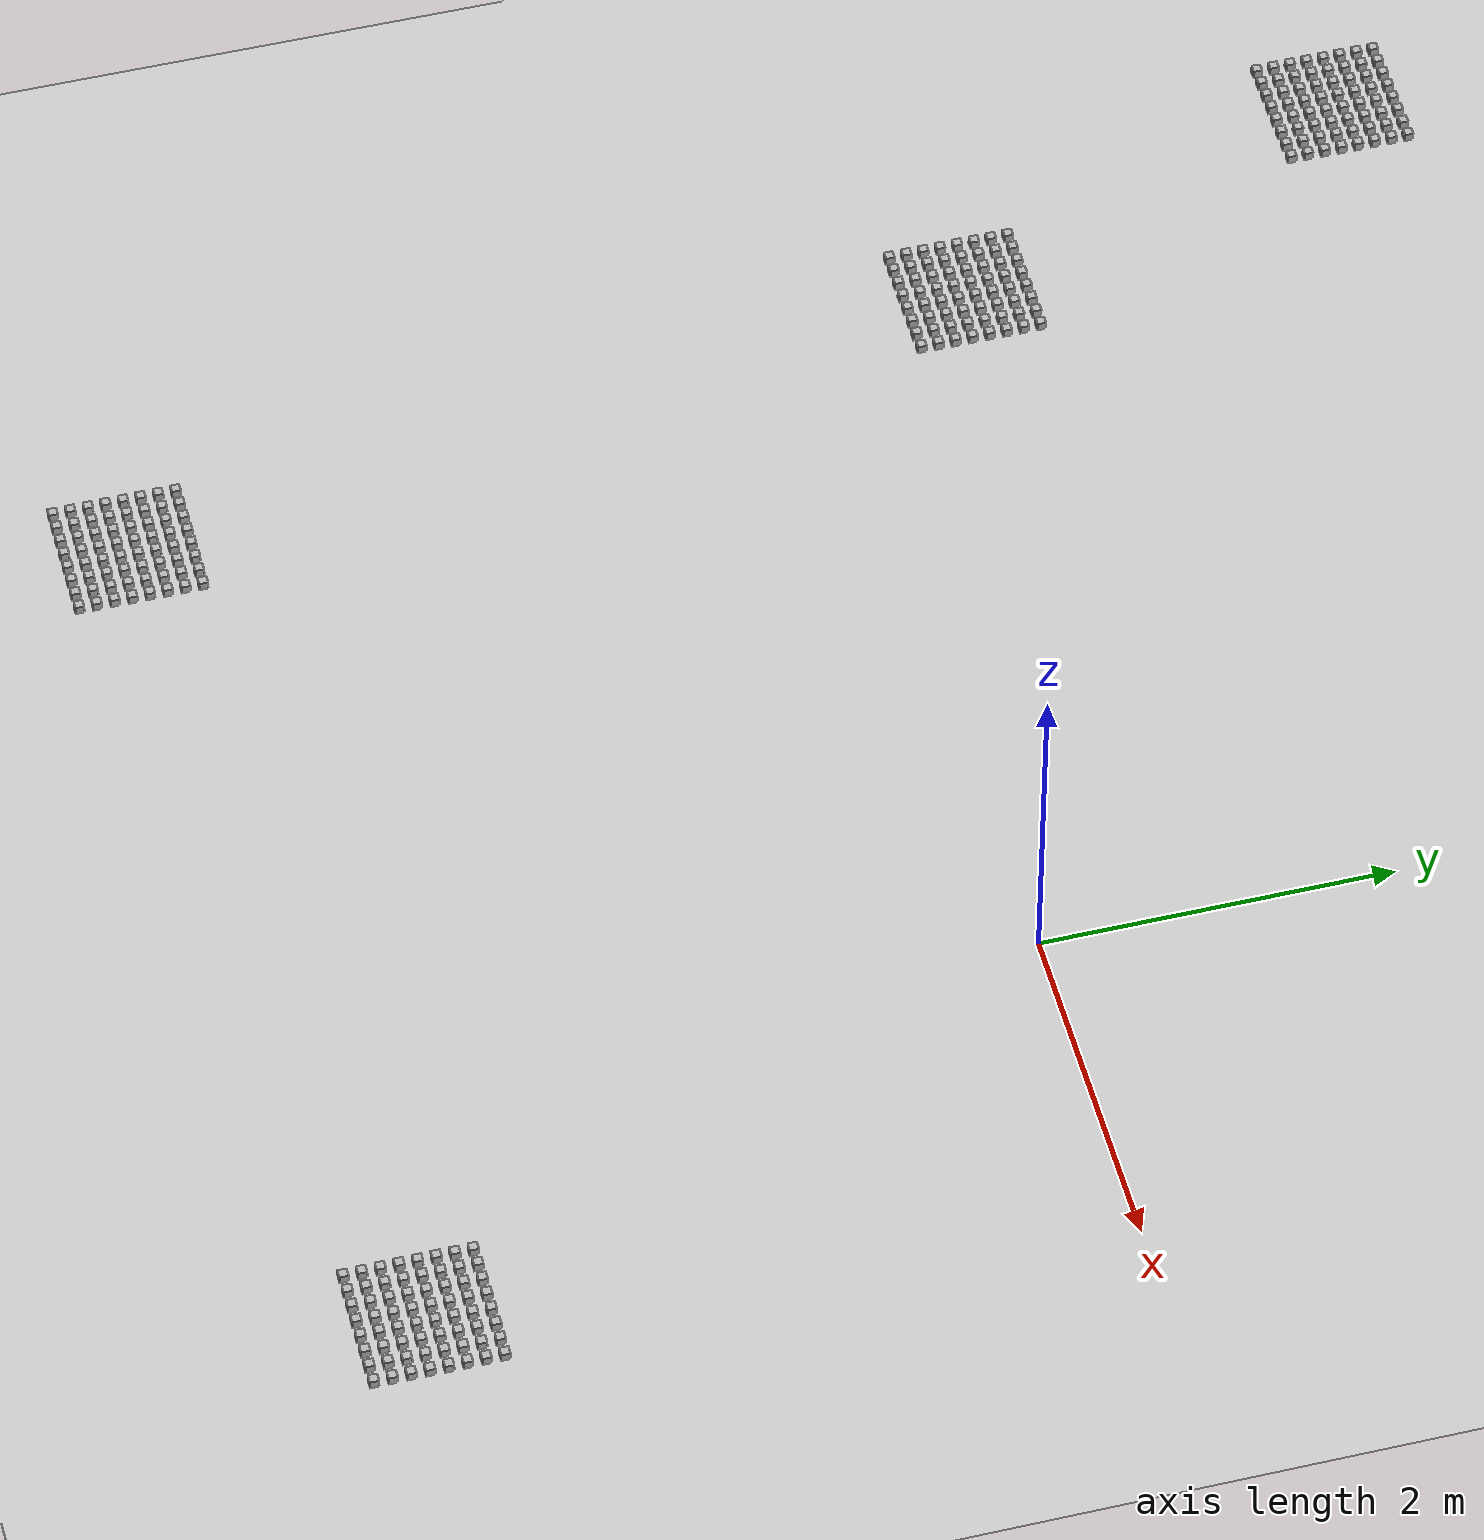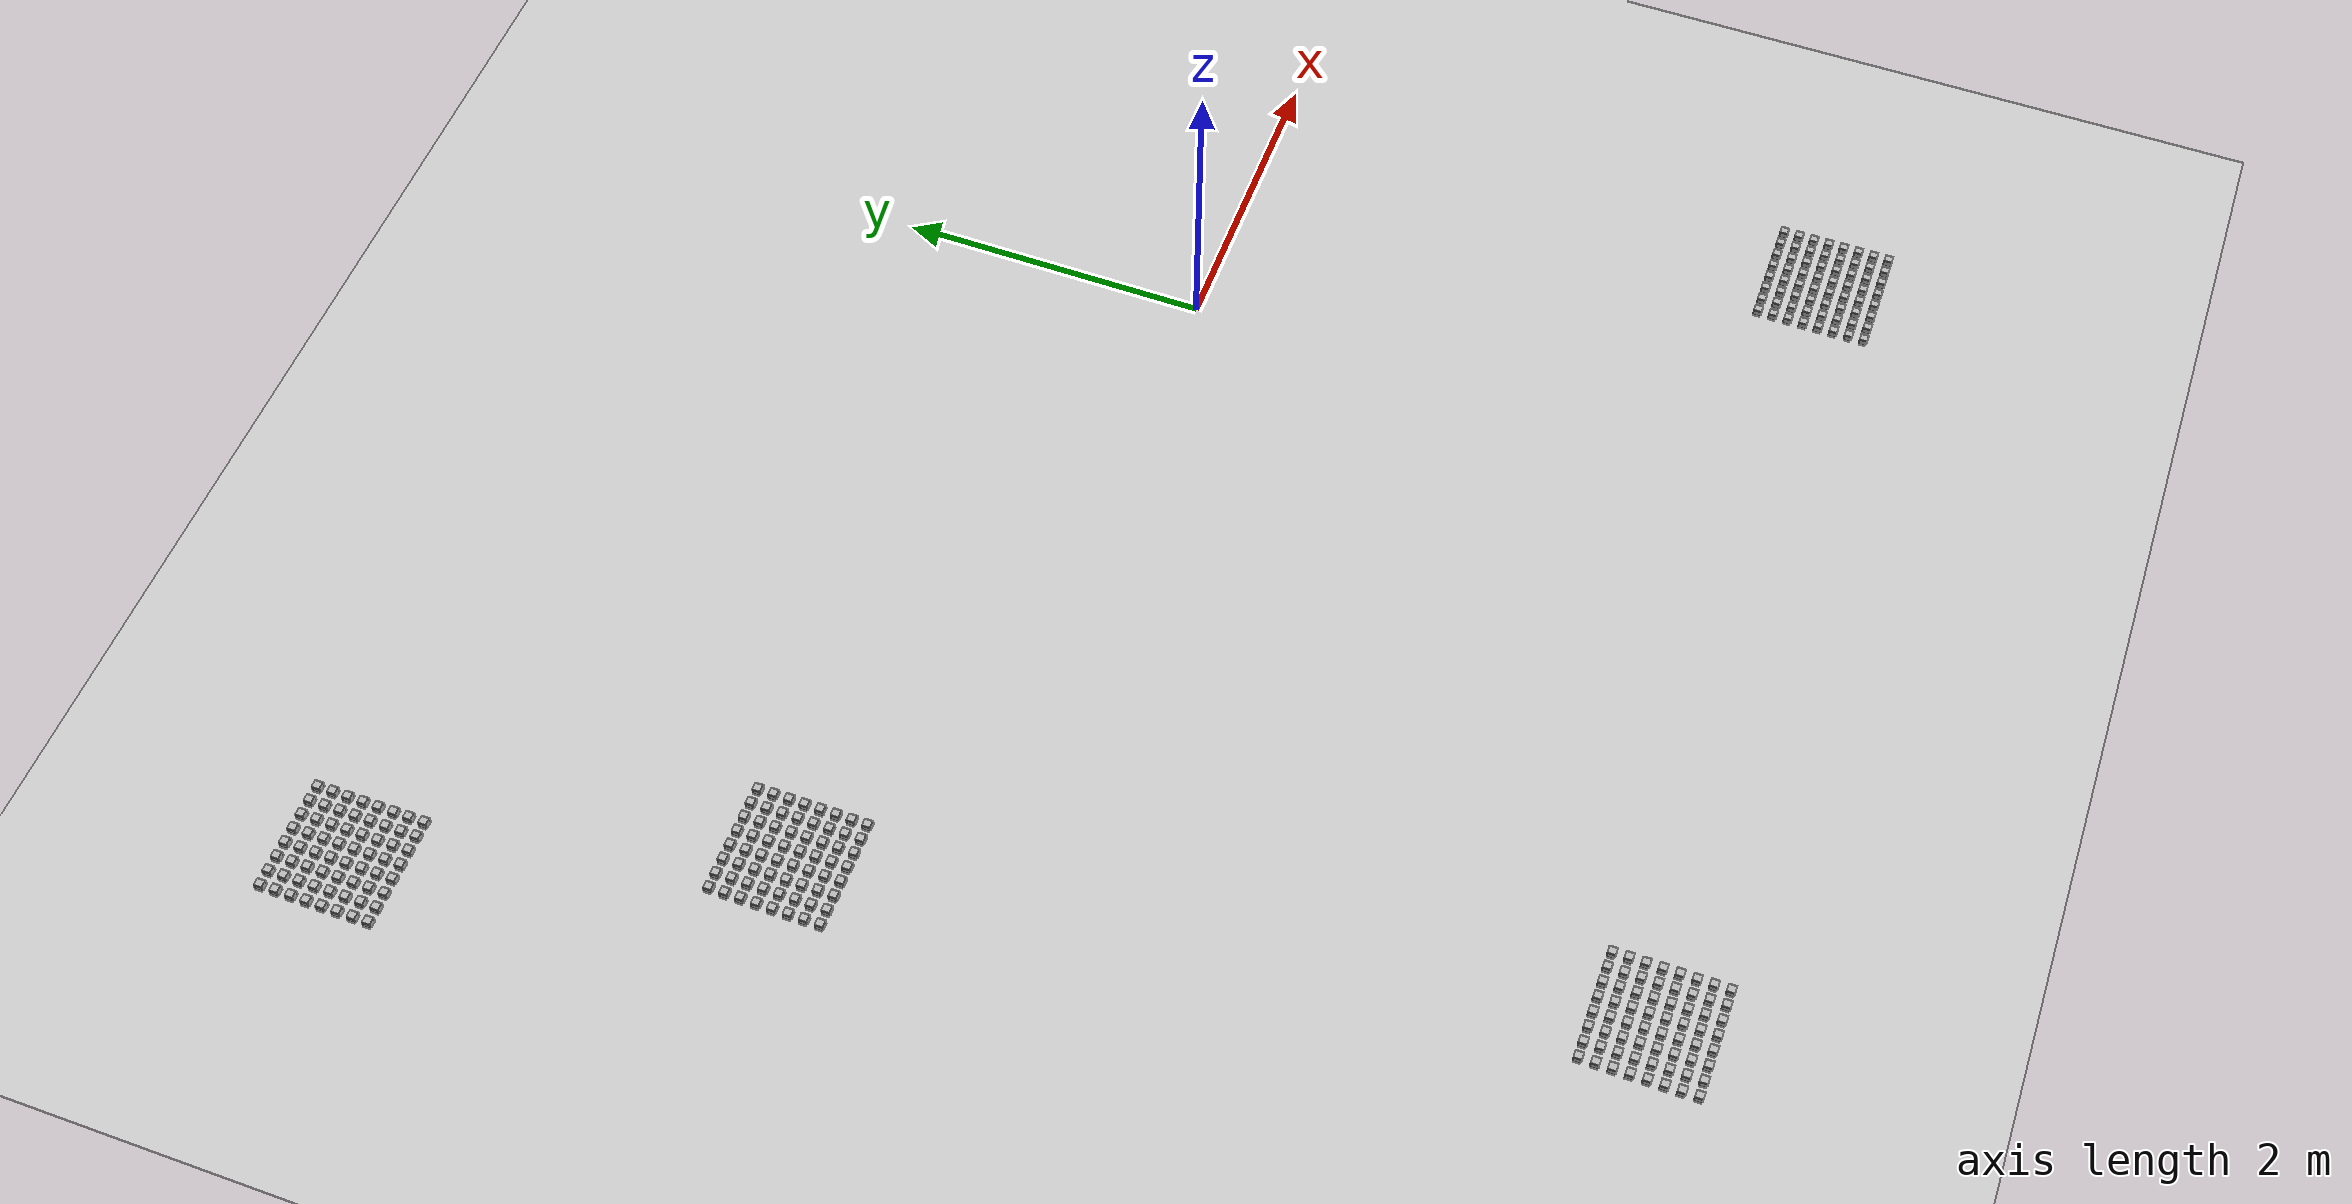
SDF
<sdf version="1.4">
 <world name="default">
  <model name="ground_plane">
   <static>1</static>
   <link name="link">
    <collision name="collision">
     <geometry><plane><normal>0 0 1</normal><size>100 100</size></plane></geometry>
     <surface><friction><ode><mu>100</mu><mu2>50</mu2></ode></friction></surface>
    </collision>
    <visual name="visual">
     <cast_shadows>0</cast_shadows>
     <geometry><plane><normal>0 0 1</normal><size>100 100</size></plane></geometry>
     <material>
      <script><uri>file://media/materials/scripts/gazebo.material</uri><name>Gazebo/Grey</name></script>
     </material>
    </visual>
    <velocity_decay><linear>0</linear><angular>0</angular></velocity_decay>
   </link>
  </model>
  <light name="sun" type="directional">
   <pose>0 0 10 0 -0 0</pose>
   <diffuse>0.8 0.8 0.8 1</diffuse>
   <specular>0.2 0.2 0.2 1</specular>
   <attenuation>
    <range>1000</range>
    <constant>0.9</constant>
    <linear>0.01</linear>
    <quadratic>0.001</quadratic>
   </attenuation>
   <direction>-0.5 0.1 -0.9</direction>
  </light>
  <plugin name="SetupWorld" filename="libgazebo_plugins.so"/>
  <physics type="ode">
   <max_step_size>0.001</max_step_size>
   <real_time_factor>1</real_time_factor>
   <real_time_update_rate>1000</real_time_update_rate>
   <gravity>0 0 -9.8</gravity>
  </physics>
  <scene><ambient>0.4 0.4 0.4 1</ambient><background>0.7 0.7 0.7 1</background><shadows>1</shadows></scene>
  <spherical_coordinates>
   <surface_model>EARTH_WGS84</surface_model>
   <latitude_deg>0</latitude_deg>
   <longitude_deg>0</longitude_deg>
   <elevation>0</elevation>
   <heading_deg>0</heading_deg>
  </spherical_coordinates>
  <model name="at0">
   <static>0</static>
   <link name="link">
    <inertial>
     <mass>0.01</mass>
     <inertia><ixx>4e-05</ixx><ixy>0</ixy><ixz>0</ixz><iyy>4e-05</iyy><iyz>0</iyz><izz>4e-05</izz></inertia>
    </inertial>
    <visual name="visual">
     <transparency>0.1</transparency>
     <geometry><box><size>0.05 0.05 0.05</size></box></geometry>
     <material>
      <script>
       <uri>model://at0/materials/scripts</uri>
       <uri>model://at0/materials/textures</uri>
       <name>at0/Diffuse</name>
      </script>
     </material>
    </visual>
    <collision name="collision">
     <geometry><box><size>0.05 0.05 0.05</size></box></geometry>
     <surface><friction><ode><mu>0.8</mu><mu2>0.7</mu2></ode></friction></surface>
    </collision>
    <velocity_decay><linear>0</linear><angular>0</angular></velocity_decay>
   </link>
   <pose>-5.01833 0.509652 0.024997 2.9e-05 2.9e-05 9e-06</pose>
  </model>
  <model name="at1">
   <static>0</static>
   <link name="link">
    <inertial>
     <mass>0.01</mass>
     <inertia><ixx>4e-05</ixx><ixy>0</ixy><ixz>0</ixz><iyy>4e-05</iyy><iyz>0</iyz><izz>4e-05</izz></inertia>
    </inertial>
    <visual name="visual">
     <transparency>0.1</transparency>
     <geometry><box><size>0.05 0.05 0.05</size></box></geometry>
     <material>
      <script>
       <uri>model://at0/materials/scripts</uri>
       <uri>model://at0/materials/textures</uri>
       <name>at0/Diffuse</name>
      </script>
     </material>
    </visual>
    <collision name="collision">
     <geometry><box><size>0.05 0.05 0.05</size></box></geometry>
     <surface><friction><ode><mu>0.8</mu><mu2>0.7</mu2></ode></friction></surface>
    </collision>
    <velocity_decay><linear>0</linear><angular>0</angular></velocity_decay>
   </link>
   <pose>-4.91833 0.509654 0.024993 -2.9e-05 -2.9e-05 9e-06</pose>
  </model>
  <model name="at2">
   <static>0</static>
   <link name="link">
    <inertial>
     <mass>0.01</mass>
     <inertia><ixx>4e-05</ixx><ixy>0</ixy><ixz>0</ixz><iyy>4e-05</iyy><iyz>0</iyz><izz>4e-05</izz></inertia>
    </inertial>
    <visual name="visual">
     <transparency>0.1</transparency>
     <geometry><box><size>0.05 0.05 0.05</size></box></geometry>
     <material>
      <script>
       <uri>model://at0/materials/scripts</uri>
       <uri>model://at0/materials/textures</uri>
       <name>at0/Diffuse</name>
      </script>
     </material>
    </visual>
    <collision name="collision">
     <geometry><box><size>0.05 0.05 0.05</size></box></geometry>
     <surface><friction><ode><mu>0.8</mu><mu2>0.7</mu2></ode></friction></surface>
    </collision>
    <velocity_decay><linear>0</linear><angular>0</angular></velocity_decay>
   </link>
   <pose>-4.81833 0.509652 0.024997 2.9e-05 2.9e-05 9e-06</pose>
  </model>
  <model name="at3">
   <static>0</static>
   <link name="link">
    <inertial>
     <mass>0.01</mass>
     <inertia><ixx>4e-05</ixx><ixy>0</ixy><ixz>0</ixz><iyy>4e-05</iyy><iyz>0</iyz><izz>4e-05</izz></inertia>
    </inertial>
    <visual name="visual">
     <transparency>0.1</transparency>
     <geometry><box><size>0.05 0.05 0.05</size></box></geometry>
     <material>
      <script>
       <uri>model://at0/materials/scripts</uri>
       <uri>model://at0/materials/textures</uri>
       <name>at0/Diffuse</name>
      </script>
     </material>
    </visual>
    <collision name="collision">
     <geometry><box><size>0.05 0.05 0.05</size></box></geometry>
     <surface><friction><ode><mu>0.8</mu><mu2>0.7</mu2></ode></friction></surface>
    </collision>
    <velocity_decay><linear>0</linear><angular>0</angular></velocity_decay>
   </link>
   <pose>-4.71833 0.509654 0.024993 -2.9e-05 -2.9e-05 9e-06</pose>
  </model>
  <model name="at4">
   <static>0</static>
   <link name="link">
    <inertial>
     <mass>0.01</mass>
     <inertia><ixx>4e-05</ixx><ixy>0</ixy><ixz>0</ixz><iyy>4e-05</iyy><iyz>0</iyz><izz>4e-05</izz></inertia>
    </inertial>
    <visual name="visual">
     <transparency>0.1</transparency>
     <geometry><box><size>0.05 0.05 0.05</size></box></geometry>
     <material>
      <script>
       <uri>model://at0/materials/scripts</uri>
       <uri>model://at0/materials/textures</uri>
       <name>at0/Diffuse</name>
      </script>
     </material>
    </visual>
    <collision name="collision">
     <geometry><box><size>0.05 0.05 0.05</size></box></geometry>
     <surface><friction><ode><mu>0.8</mu><mu2>0.7</mu2></ode></friction></surface>
    </collision>
    <velocity_decay><linear>0</linear><angular>0</angular></velocity_decay>
   </link>
   <pose>-4.61833 0.509652 0.024997 2.9e-05 2.9e-05 9e-06</pose>
  </model>
  <model name="at5">
   <static>0</static>
   <link name="link">
    <inertial>
     <mass>0.01</mass>
     <inertia><ixx>4e-05</ixx><ixy>0</ixy><ixz>0</ixz><iyy>4e-05</iyy><iyz>0</iyz><izz>4e-05</izz></inertia>
    </inertial>
    <visual name="visual">
     <transparency>0.1</transparency>
     <geometry><box><size>0.05 0.05 0.05</size></box></geometry>
     <material>
      <script>
       <uri>model://at0/materials/scripts</uri>
       <uri>model://at0/materials/textures</uri>
       <name>at0/Diffuse</name>
      </script>
     </material>
    </visual>
    <collision name="collision">
     <geometry><box><size>0.05 0.05 0.05</size></box></geometry>
     <surface><friction><ode><mu>0.8</mu><mu2>0.7</mu2></ode></friction></surface>
    </collision>
    <velocity_decay><linear>0</linear><angular>0</angular></velocity_decay>
   </link>
   <pose>-4.51833 0.509654 0.024993 -2.9e-05 -2.9e-05 9e-06</pose>
  </model>
  <model name="at6">
   <static>0</static>
   <link name="link">
    <inertial>
     <mass>0.01</mass>
     <inertia><ixx>4e-05</ixx><ixy>0</ixy><ixz>0</ixz><iyy>4e-05</iyy><iyz>0</iyz><izz>4e-05</izz></inertia>
    </inertial>
    <visual name="visual">
     <transparency>0.1</transparency>
     <geometry><box><size>0.05 0.05 0.05</size></box></geometry>
     <material>
      <script>
       <uri>model://at0/materials/scripts</uri>
       <uri>model://at0/materials/textures</uri>
       <name>at0/Diffuse</name>
      </script>
     </material>
    </visual>
    <collision name="collision">
     <geometry><box><size>0.05 0.05 0.05</size></box></geometry>
     <surface><friction><ode><mu>0.8</mu><mu2>0.7</mu2></ode></friction></surface>
    </collision>
    <velocity_decay><linear>0</linear><angular>0</angular></velocity_decay>
   </link>
   <pose>-4.41833 0.509652 0.024997 2.9e-05 2.9e-05 8e-06</pose>
  </model>
  <model name="at7">
   <static>0</static>
   <link name="link">
    <inertial>
     <mass>0.01</mass>
     <inertia><ixx>4e-05</ixx><ixy>0</ixy><ixz>0</ixz><iyy>4e-05</iyy><iyz>0</iyz><izz>4e-05</izz></inertia>
    </inertial>
    <visual name="visual">
     <transparency>0.1</transparency>
     <geometry><box><size>0.05 0.05 0.05</size></box></geometry>
     <material>
      <script>
       <uri>model://at0/materials/scripts</uri>
       <uri>model://at0/materials/textures</uri>
       <name>at0/Diffuse</name>
      </script>
     </material>
    </visual>
    <collision name="collision">
     <geometry><box><size>0.05 0.05 0.05</size></box></geometry>
     <surface><friction><ode><mu>0.8</mu><mu2>0.7</mu2></ode></friction></surface>
    </collision>
    <velocity_decay><linear>0</linear><angular>0</angular></velocity_decay>
   </link>
   <pose>-4.31833 0.509652 0.024997 2.9e-05 2.9e-05 8e-06</pose>
  </model>
  <model name="at8">
   <static>0</static>
   <link name="link">
    <inertial>
     <mass>0.01</mass>
     <inertia><ixx>4e-05</ixx><ixy>0</ixy><ixz>0</ixz><iyy>4e-05</iyy><iyz>0</iyz><izz>4e-05</izz></inertia>
    </inertial>
    <visual name="visual">
     <transparency>0.1</transparency>
     <geometry><box><size>0.05 0.05 0.05</size></box></geometry>
     <material>
      <script>
       <uri>model://at0/materials/scripts</uri>
       <uri>model://at0/materials/textures</uri>
       <name>at0/Diffuse</name>
      </script>
     </material>
    </visual>
    <collision name="collision">
     <geometry><box><size>0.05 0.05 0.05</size></box></geometry>
     <surface><friction><ode><mu>0.8</mu><mu2>0.7</mu2></ode></friction></surface>
    </collision>
    <velocity_decay><linear>0</linear><angular>0</angular></velocity_decay>
   </link>
   <pose>-5.01833 0.609654 0.024993 -2.9e-05 -2.9e-05 8e-06</pose>
  </model>
  <model name="at9">
   <static>0</static>
   <link name="link">
    <inertial>
     <mass>0.01</mass>
     <inertia><ixx>4e-05</ixx><ixy>0</ixy><ixz>0</ixz><iyy>4e-05</iyy><iyz>0</iyz><izz>4e-05</izz></inertia>
    </inertial>
    <visual name="visual">
     <transparency>0.1</transparency>
     <geometry><box><size>0.05 0.05 0.05</size></box></geometry>
     <material>
      <script>
       <uri>model://at0/materials/scripts</uri>
       <uri>model://at0/materials/textures</uri>
       <name>at0/Diffuse</name>
      </script>
     </material>
    </visual>
    <collision name="collision">
     <geometry><box><size>0.05 0.05 0.05</size></box></geometry>
     <surface><friction><ode><mu>0.8</mu><mu2>0.7</mu2></ode></friction></surface>
    </collision>
    <velocity_decay><linear>0</linear><angular>0</angular></velocity_decay>
   </link>
   <pose>-4.91833 0.609652 0.024997 2.9e-05 2.9e-05 8e-06</pose>
  </model>
  <model name="at10">
   <static>0</static>
   <link name="link">
    <inertial>
     <mass>0.01</mass>
     <inertia><ixx>4e-05</ixx><ixy>0</ixy><ixz>0</ixz><iyy>4e-05</iyy><iyz>0</iyz><izz>4e-05</izz></inertia>
    </inertial>
    <visual name="visual">
     <transparency>0.1</transparency>
     <geometry><box><size>0.05 0.05 0.05</size></box></geometry>
     <material>
      <script>
       <uri>model://at0/materials/scripts</uri>
       <uri>model://at0/materials/textures</uri>
       <name>at0/Diffuse</name>
      </script>
     </material>
    </visual>
    <collision name="collision">
     <geometry><box><size>0.05 0.05 0.05</size></box></geometry>
     <surface><friction><ode><mu>0.8</mu><mu2>0.7</mu2></ode></friction></surface>
    </collision>
    <velocity_decay><linear>0</linear><angular>0</angular></velocity_decay>
   </link>
   <pose>-4.81833 0.609652 0.024997 2.9e-05 2.9e-05 8e-06</pose>
  </model>
  <model name="at11">
   <static>0</static>
   <link name="link">
    <inertial>
     <mass>0.01</mass>
     <inertia><ixx>4e-05</ixx><ixy>0</ixy><ixz>0</ixz><iyy>4e-05</iyy><iyz>0</iyz><izz>4e-05</izz></inertia>
    </inertial>
    <visual name="visual">
     <transparency>0.1</transparency>
     <geometry><box><size>0.05 0.05 0.05</size></box></geometry>
     <material>
      <script>
       <uri>model://at0/materials/scripts</uri>
       <uri>model://at0/materials/textures</uri>
       <name>at0/Diffuse</name>
      </script>
     </material>
    </visual>
    <collision name="collision">
     <geometry><box><size>0.05 0.05 0.05</size></box></geometry>
     <surface><friction><ode><mu>0.8</mu><mu2>0.7</mu2></ode></friction></surface>
    </collision>
    <velocity_decay><linear>0</linear><angular>0</angular></velocity_decay>
   </link>
   <pose>-4.71833 0.609652 0.024997 2.9e-05 2.9e-05 8e-06</pose>
  </model>
  <model name="at12">
   <static>0</static>
   <link name="link">
    <inertial>
     <mass>0.01</mass>
     <inertia><ixx>4e-05</ixx><ixy>0</ixy><ixz>0</ixz><iyy>4e-05</iyy><iyz>0</iyz><izz>4e-05</izz></inertia>
    </inertial>
    <visual name="visual">
     <transparency>0.1</transparency>
     <geometry><box><size>0.05 0.05 0.05</size></box></geometry>
     <material>
      <script>
       <uri>model://at0/materials/scripts</uri>
       <uri>model://at0/materials/textures</uri>
       <name>at0/Diffuse</name>
      </script>
     </material>
    </visual>
    <collision name="collision">
     <geometry><box><size>0.05 0.05 0.05</size></box></geometry>
     <surface><friction><ode><mu>0.8</mu><mu2>0.7</mu2></ode></friction></surface>
    </collision>
    <velocity_decay><linear>0</linear><angular>0</angular></velocity_decay>
   </link>
   <pose>-4.61833 0.609653 0.024993 -2.9e-05 -2.9e-05 8e-06</pose>
  </model>
  <model name="at13">
   <static>0</static>
   <link name="link">
    <inertial>
     <mass>0.01</mass>
     <inertia><ixx>4e-05</ixx><ixy>0</ixy><ixz>0</ixz><iyy>4e-05</iyy><iyz>0</iyz><izz>4e-05</izz></inertia>
    </inertial>
    <visual name="visual">
     <transparency>0.1</transparency>
     <geometry><box><size>0.05 0.05 0.05</size></box></geometry>
     <material>
      <script>
       <uri>model://at0/materials/scripts</uri>
       <uri>model://at0/materials/textures</uri>
       <name>at0/Diffuse</name>
      </script>
     </material>
    </visual>
    <collision name="collision">
     <geometry><box><size>0.05 0.05 0.05</size></box></geometry>
     <surface><friction><ode><mu>0.8</mu><mu2>0.7</mu2></ode></friction></surface>
    </collision>
    <velocity_decay><linear>0</linear><angular>0</angular></velocity_decay>
   </link>
   <pose>-4.51833 0.609652 0.024997 2.9e-05 2.9e-05 7e-06</pose>
  </model>
  <model name="at14">
   <static>0</static>
   <link name="link">
    <inertial>
     <mass>0.01</mass>
     <inertia><ixx>4e-05</ixx><ixy>0</ixy><ixz>0</ixz><iyy>4e-05</iyy><iyz>0</iyz><izz>4e-05</izz></inertia>
    </inertial>
    <visual name="visual">
     <transparency>0.1</transparency>
     <geometry><box><size>0.05 0.05 0.05</size></box></geometry>
     <material>
      <script>
       <uri>model://at0/materials/scripts</uri>
       <uri>model://at0/materials/textures</uri>
       <name>at0/Diffuse</name>
      </script>
     </material>
    </visual>
    <collision name="collision">
     <geometry><box><size>0.05 0.05 0.05</size></box></geometry>
     <surface><friction><ode><mu>0.8</mu><mu2>0.7</mu2></ode></friction></surface>
    </collision>
    <velocity_decay><linear>0</linear><angular>0</angular></velocity_decay>
   </link>
   <pose>-4.41833 0.609653 0.024993 -2.9e-05 -2.9e-05 7e-06</pose>
  </model>
  <model name="at15">
   <static>0</static>
   <link name="link">
    <inertial>
     <mass>0.01</mass>
     <inertia><ixx>4e-05</ixx><ixy>0</ixy><ixz>0</ixz><iyy>4e-05</iyy><iyz>0</iyz><izz>4e-05</izz></inertia>
    </inertial>
    <visual name="visual">
     <transparency>0.1</transparency>
     <geometry><box><size>0.05 0.05 0.05</size></box></geometry>
     <material>
      <script>
       <uri>model://at0/materials/scripts</uri>
       <uri>model://at0/materials/textures</uri>
       <name>at0/Diffuse</name>
      </script>
     </material>
    </visual>
    <collision name="collision">
     <geometry><box><size>0.05 0.05 0.05</size></box></geometry>
     <surface><friction><ode><mu>0.8</mu><mu2>0.7</mu2></ode></friction></surface>
    </collision>
    <velocity_decay><linear>0</linear><angular>0</angular></velocity_decay>
   </link>
   <pose>-4.31833 0.609652 0.024997 2.9e-05 2.9e-05 7e-06</pose>
  </model>
  <model name="at16">
   <static>0</static>
   <link name="link">
    <inertial>
     <mass>0.01</mass>
     <inertia><ixx>4e-05</ixx><ixy>0</ixy><ixz>0</ixz><iyy>4e-05</iyy><iyz>0</iyz><izz>4e-05</izz></inertia>
    </inertial>
    <visual name="visual">
     <transparency>0.1</transparency>
     <geometry><box><size>0.05 0.05 0.05</size></box></geometry>
     <material>
      <script>
       <uri>model://at0/materials/scripts</uri>
       <uri>model://at0/materials/textures</uri>
       <name>at0/Diffuse</name>
      </script>
     </material>
    </visual>
    <collision name="collision">
     <geometry><box><size>0.05 0.05 0.05</size></box></geometry>
     <surface><friction><ode><mu>0.8</mu><mu2>0.7</mu2></ode></friction></surface>
    </collision>
    <velocity_decay><linear>0</linear><angular>0</angular></velocity_decay>
   </link>
   <pose>-5.01833 0.709653 0.024993 -2.9e-05 -2.9e-05 7e-06</pose>
  </model>
  <model name="at17">
   <static>0</static>
   <link name="link">
    <inertial>
     <mass>0.01</mass>
     <inertia><ixx>4e-05</ixx><ixy>0</ixy><ixz>0</ixz><iyy>4e-05</iyy><iyz>0</iyz><izz>4e-05</izz></inertia>
    </inertial>
    <visual name="visual">
     <transparency>0.1</transparency>
     <geometry><box><size>0.05 0.05 0.05</size></box></geometry>
     <material>
      <script>
       <uri>model://at0/materials/scripts</uri>
       <uri>model://at0/materials/textures</uri>
       <name>at0/Diffuse</name>
      </script>
     </material>
    </visual>
    <collision name="collision">
     <geometry><box><size>0.05 0.05 0.05</size></box></geometry>
     <surface><friction><ode><mu>0.8</mu><mu2>0.7</mu2></ode></friction></surface>
    </collision>
    <velocity_decay><linear>0</linear><angular>0</angular></velocity_decay>
   </link>
   <pose>-4.91833 0.709652 0.024997 2.9e-05 2.9e-05 7e-06</pose>
  </model>
  <model name="at18">
   <static>0</static>
   <link name="link">
    <inertial>
     <mass>0.01</mass>
     <inertia><ixx>4e-05</ixx><ixy>0</ixy><ixz>0</ixz><iyy>4e-05</iyy><iyz>0</iyz><izz>4e-05</izz></inertia>
    </inertial>
    <visual name="visual">
     <transparency>0.1</transparency>
     <geometry><box><size>0.05 0.05 0.05</size></box></geometry>
     <material>
      <script>
       <uri>model://at0/materials/scripts</uri>
       <uri>model://at0/materials/textures</uri>
       <name>at0/Diffuse</name>
      </script>
     </material>
    </visual>
    <collision name="collision">
     <geometry><box><size>0.05 0.05 0.05</size></box></geometry>
     <surface><friction><ode><mu>0.8</mu><mu2>0.7</mu2></ode></friction></surface>
    </collision>
    <velocity_decay><linear>0</linear><angular>0</angular></velocity_decay>
   </link>
   <pose>-4.81833 0.709652 0.024997 2.9e-05 2.9e-05 7e-06</pose>
  </model>
  <model name="at19">
   <static>0</static>
   <link name="link">
    <inertial>
     <mass>0.01</mass>
     <inertia><ixx>4e-05</ixx><ixy>0</ixy><ixz>0</ixz><iyy>4e-05</iyy><iyz>0</iyz><izz>4e-05</izz></inertia>
    </inertial>
    <visual name="visual">
     <transparency>0.1</transparency>
     <geometry><box><size>0.05 0.05 0.05</size></box></geometry>
     <material>
      <script>
       <uri>model://at0/materials/scripts</uri>
       <uri>model://at0/materials/textures</uri>
       <name>at0/Diffuse</name>
      </script>
     </material>
    </visual>
    <collision name="collision">
     <geometry><box><size>0.05 0.05 0.05</size></box></geometry>
     <surface><friction><ode><mu>0.8</mu><mu2>0.7</mu2></ode></friction></surface>
    </collision>
    <velocity_decay><linear>0</linear><angular>0</angular></velocity_decay>
   </link>
   <pose>-4.71833 0.709652 0.024997 2.9e-05 2.9e-05 7e-06</pose>
  </model>
  <model name="at20">
   <static>0</static>
   <link name="link">
    <inertial>
     <mass>0.01</mass>
     <inertia><ixx>4e-05</ixx><ixy>0</ixy><ixz>0</ixz><iyy>4e-05</iyy><iyz>0</iyz><izz>4e-05</izz></inertia>
    </inertial>
    <visual name="visual">
     <transparency>0.1</transparency>
     <geometry><box><size>0.05 0.05 0.05</size></box></geometry>
     <material>
      <script>
       <uri>model://at0/materials/scripts</uri>
       <uri>model://at0/materials/textures</uri>
       <name>at0/Diffuse</name>
      </script>
     </material>
    </visual>
    <collision name="collision">
     <geometry><box><size>0.05 0.05 0.05</size></box></geometry>
     <surface><friction><ode><mu>0.8</mu><mu2>0.7</mu2></ode></friction></surface>
    </collision>
    <velocity_decay><linear>0</linear><angular>0</angular></velocity_decay>
   </link>
   <pose>-4.61833 0.709653 0.024993 -2.9e-05 -2.9e-05 7e-06</pose>
  </model>
  <model name="at21">
   <static>0</static>
   <link name="link">
    <inertial>
     <mass>0.01</mass>
     <inertia><ixx>4e-05</ixx><ixy>0</ixy><ixz>0</ixz><iyy>4e-05</iyy><iyz>0</iyz><izz>4e-05</izz></inertia>
    </inertial>
    <visual name="visual">
     <transparency>0.1</transparency>
     <geometry><box><size>0.05 0.05 0.05</size></box></geometry>
     <material>
      <script>
       <uri>model://at0/materials/scripts</uri>
       <uri>model://at0/materials/textures</uri>
       <name>at0/Diffuse</name>
      </script>
     </material>
    </visual>
    <collision name="collision">
     <geometry><box><size>0.05 0.05 0.05</size></box></geometry>
     <surface><friction><ode><mu>0.8</mu><mu2>0.7</mu2></ode></friction></surface>
    </collision>
    <velocity_decay><linear>0</linear><angular>0</angular></velocity_decay>
   </link>
   <pose>-4.51833 0.709653 0.024993 -2.9e-05 -2.9e-05 7e-06</pose>
  </model>
  <model name="at22">
   <static>0</static>
   <link name="link">
    <inertial>
     <mass>0.01</mass>
     <inertia><ixx>4e-05</ixx><ixy>0</ixy><ixz>0</ixz><iyy>4e-05</iyy><iyz>0</iyz><izz>4e-05</izz></inertia>
    </inertial>
    <visual name="visual">
     <transparency>0.1</transparency>
     <geometry><box><size>0.05 0.05 0.05</size></box></geometry>
     <material>
      <script>
       <uri>model://at0/materials/scripts</uri>
       <uri>model://at0/materials/textures</uri>
       <name>at0/Diffuse</name>
      </script>
     </material>
    </visual>
    <collision name="collision">
     <geometry><box><size>0.05 0.05 0.05</size></box></geometry>
     <surface><friction><ode><mu>0.8</mu><mu2>0.7</mu2></ode></friction></surface>
    </collision>
    <velocity_decay><linear>0</linear><angular>0</angular></velocity_decay>
   </link>
   <pose>-4.41833 0.709653 0.024993 -2.9e-05 -2.9e-05 6e-06</pose>
  </model>
  <model name="at23">
   <static>0</static>
   <link name="link">
    <inertial>
     <mass>0.01</mass>
     <inertia><ixx>4e-05</ixx><ixy>0</ixy><ixz>0</ixz><iyy>4e-05</iyy><iyz>0</iyz><izz>4e-05</izz></inertia>
    </inertial>
    <visual name="visual">
     <transparency>0.1</transparency>
     <geometry><box><size>0.05 0.05 0.05</size></box></geometry>
     <material>
      <script>
       <uri>model://at0/materials/scripts</uri>
       <uri>model://at0/materials/textures</uri>
       <name>at0/Diffuse</name>
      </script>
     </material>
    </visual>
    <collision name="collision">
     <geometry><box><size>0.05 0.05 0.05</size></box></geometry>
     <surface><friction><ode><mu>0.8</mu><mu2>0.7</mu2></ode></friction></surface>
    </collision>
    <velocity_decay><linear>0</linear><angular>0</angular></velocity_decay>
   </link>
   <pose>-4.31833 0.709653 0.024993 -2.9e-05 -2.9e-05 6e-06</pose>
  </model>
  <model name="at24">
   <static>0</static>
   <link name="link">
    <inertial>
     <mass>0.01</mass>
     <inertia><ixx>4e-05</ixx><ixy>0</ixy><ixz>0</ixz><iyy>4e-05</iyy><iyz>0</iyz><izz>4e-05</izz></inertia>
    </inertial>
    <visual name="visual">
     <transparency>0.1</transparency>
     <geometry><box><size>0.05 0.05 0.05</size></box></geometry>
     <material>
      <script>
       <uri>model://at0/materials/scripts</uri>
       <uri>model://at0/materials/textures</uri>
       <name>at0/Diffuse</name>
      </script>
     </material>
    </visual>
    <collision name="collision">
     <geometry><box><size>0.05 0.05 0.05</size></box></geometry>
     <surface><friction><ode><mu>0.8</mu><mu2>0.7</mu2></ode></friction></surface>
    </collision>
    <velocity_decay><linear>0</linear><angular>0</angular></velocity_decay>
   </link>
   <pose>-5.01833 0.809653 0.024993 -2.9e-05 -2.9e-05 6e-06</pose>
  </model>
  <model name="at25">
   <static>0</static>
   <link name="link">
    <inertial>
     <mass>0.01</mass>
     <inertia><ixx>4e-05</ixx><ixy>0</ixy><ixz>0</ixz><iyy>4e-05</iyy><iyz>0</iyz><izz>4e-05</izz></inertia>
    </inertial>
    <visual name="visual">
     <transparency>0.1</transparency>
     <geometry><box><size>0.05 0.05 0.05</size></box></geometry>
     <material>
      <script>
       <uri>model://at0/materials/scripts</uri>
       <uri>model://at0/materials/textures</uri>
       <name>at0/Diffuse</name>
      </script>
     </material>
    </visual>
    <collision name="collision">
     <geometry><box><size>0.05 0.05 0.05</size></box></geometry>
     <surface><friction><ode><mu>0.8</mu><mu2>0.7</mu2></ode></friction></surface>
    </collision>
    <velocity_decay><linear>0</linear><angular>0</angular></velocity_decay>
   </link>
   <pose>-4.91833 0.809653 0.024993 -2.9e-05 -2.9e-05 6e-06</pose>
  </model>
  <model name="at26">
   <static>0</static>
   <link name="link">
    <inertial>
     <mass>0.01</mass>
     <inertia><ixx>4e-05</ixx><ixy>0</ixy><ixz>0</ixz><iyy>4e-05</iyy><iyz>0</iyz><izz>4e-05</izz></inertia>
    </inertial>
    <visual name="visual">
     <transparency>0.1</transparency>
     <geometry><box><size>0.05 0.05 0.05</size></box></geometry>
     <material>
      <script>
       <uri>model://at0/materials/scripts</uri>
       <uri>model://at0/materials/textures</uri>
       <name>at0/Diffuse</name>
      </script>
     </material>
    </visual>
    <collision name="collision">
     <geometry><box><size>0.05 0.05 0.05</size></box></geometry>
     <surface><friction><ode><mu>0.8</mu><mu2>0.7</mu2></ode></friction></surface>
    </collision>
    <velocity_decay><linear>0</linear><angular>0</angular></velocity_decay>
   </link>
   <pose>-4.81833 0.809652 0.024997 2.9e-05 2.9e-05 6e-06</pose>
  </model>
  <model name="at27">
   <static>0</static>
   <link name="link">
    <inertial>
     <mass>0.01</mass>
     <inertia><ixx>4e-05</ixx><ixy>0</ixy><ixz>0</ixz><iyy>4e-05</iyy><iyz>0</iyz><izz>4e-05</izz></inertia>
    </inertial>
    <visual name="visual">
     <transparency>0.1</transparency>
     <geometry><box><size>0.05 0.05 0.05</size></box></geometry>
     <material>
      <script>
       <uri>model://at0/materials/scripts</uri>
       <uri>model://at0/materials/textures</uri>
       <name>at0/Diffuse</name>
      </script>
     </material>
    </visual>
    <collision name="collision">
     <geometry><box><size>0.05 0.05 0.05</size></box></geometry>
     <surface><friction><ode><mu>0.8</mu><mu2>0.7</mu2></ode></friction></surface>
    </collision>
    <velocity_decay><linear>0</linear><angular>0</angular></velocity_decay>
   </link>
   <pose>-4.71833 0.809652 0.024997 2.9e-05 2.9e-05 6e-06</pose>
  </model>
  <model name="at28">
   <static>0</static>
   <link name="link">
    <inertial>
     <mass>0.01</mass>
     <inertia><ixx>4e-05</ixx><ixy>0</ixy><ixz>0</ixz><iyy>4e-05</iyy><iyz>0</iyz><izz>4e-05</izz></inertia>
    </inertial>
    <visual name="visual">
     <transparency>0.1</transparency>
     <geometry><box><size>0.05 0.05 0.05</size></box></geometry>
     <material>
      <script>
       <uri>model://at0/materials/scripts</uri>
       <uri>model://at0/materials/textures</uri>
       <name>at0/Diffuse</name>
      </script>
     </material>
    </visual>
    <collision name="collision">
     <geometry><box><size>0.05 0.05 0.05</size></box></geometry>
     <surface><friction><ode><mu>0.8</mu><mu2>0.7</mu2></ode></friction></surface>
    </collision>
    <velocity_decay><linear>0</linear><angular>0</angular></velocity_decay>
   </link>
   <pose>-4.61833 0.809652 0.024997 2.9e-05 2.9e-05 6e-06</pose>
  </model>
  <model name="at29">
   <static>0</static>
   <link name="link">
    <inertial>
     <mass>0.01</mass>
     <inertia><ixx>4e-05</ixx><ixy>0</ixy><ixz>0</ixz><iyy>4e-05</iyy><iyz>0</iyz><izz>4e-05</izz></inertia>
    </inertial>
    <visual name="visual">
     <transparency>0.1</transparency>
     <geometry><box><size>0.05 0.05 0.05</size></box></geometry>
     <material>
      <script>
       <uri>model://at0/materials/scripts</uri>
       <uri>model://at0/materials/textures</uri>
       <name>at0/Diffuse</name>
      </script>
     </material>
    </visual>
    <collision name="collision">
     <geometry><box><size>0.05 0.05 0.05</size></box></geometry>
     <surface><friction><ode><mu>0.8</mu><mu2>0.7</mu2></ode></friction></surface>
    </collision>
    <velocity_decay><linear>0</linear><angular>0</angular></velocity_decay>
   </link>
   <pose>-4.51833 0.809652 0.024997 2.9e-05 2.9e-05 6e-06</pose>
  </model>
  <model name="at30">
   <static>0</static>
   <link name="link">
    <inertial>
     <mass>0.01</mass>
     <inertia><ixx>4e-05</ixx><ixy>0</ixy><ixz>0</ixz><iyy>4e-05</iyy><iyz>0</iyz><izz>4e-05</izz></inertia>
    </inertial>
    <visual name="visual">
     <transparency>0.1</transparency>
     <geometry><box><size>0.05 0.05 0.05</size></box></geometry>
     <material>
      <script>
       <uri>model://at0/materials/scripts</uri>
       <uri>model://at0/materials/textures</uri>
       <name>at0/Diffuse</name>
      </script>
     </material>
    </visual>
    <collision name="collision">
     <geometry><box><size>0.05 0.05 0.05</size></box></geometry>
     <surface><friction><ode><mu>0.8</mu><mu2>0.7</mu2></ode></friction></surface>
    </collision>
    <velocity_decay><linear>0</linear><angular>0</angular></velocity_decay>
   </link>
   <pose>-4.41833 0.809653 0.024993 -2.9e-05 -2.9e-05 6e-06</pose>
  </model>
  <model name="at31">
   <static>0</static>
   <link name="link">
    <inertial>
     <mass>0.01</mass>
     <inertia><ixx>4e-05</ixx><ixy>0</ixy><ixz>0</ixz><iyy>4e-05</iyy><iyz>0</iyz><izz>4e-05</izz></inertia>
    </inertial>
    <visual name="visual">
     <transparency>0.1</transparency>
     <geometry><box><size>0.05 0.05 0.05</size></box></geometry>
     <material>
      <script>
       <uri>model://at0/materials/scripts</uri>
       <uri>model://at0/materials/textures</uri>
       <name>at0/Diffuse</name>
      </script>
     </material>
    </visual>
    <collision name="collision">
     <geometry><box><size>0.05 0.05 0.05</size></box></geometry>
     <surface><friction><ode><mu>0.8</mu><mu2>0.7</mu2></ode></friction></surface>
    </collision>
    <velocity_decay><linear>0</linear><angular>0</angular></velocity_decay>
   </link>
   <pose>-4.31833 0.809652 0.024997 2.9e-05 2.9e-05 6e-06</pose>
  </model>
  <model name="at32">
   <static>0</static>
   <link name="link">
    <inertial>
     <mass>0.01</mass>
     <inertia><ixx>4e-05</ixx><ixy>0</ixy><ixz>0</ixz><iyy>4e-05</iyy><iyz>0</iyz><izz>4e-05</izz></inertia>
    </inertial>
    <visual name="visual">
     <transparency>0.1</transparency>
     <geometry><box><size>0.05 0.05 0.05</size></box></geometry>
     <material>
      <script>
       <uri>model://at0/materials/scripts</uri>
       <uri>model://at0/materials/textures</uri>
       <name>at0/Diffuse</name>
      </script>
     </material>
    </visual>
    <collision name="collision">
     <geometry><box><size>0.05 0.05 0.05</size></box></geometry>
     <surface><friction><ode><mu>0.8</mu><mu2>0.7</mu2></ode></friction></surface>
    </collision>
    <velocity_decay><linear>0</linear><angular>0</angular></velocity_decay>
   </link>
   <pose>-5.01833 0.909652 0.024997 2.9e-05 2.9e-05 5e-06</pose>
  </model>
  <model name="at33">
   <static>0</static>
   <link name="link">
    <inertial>
     <mass>0.01</mass>
     <inertia><ixx>4e-05</ixx><ixy>0</ixy><ixz>0</ixz><iyy>4e-05</iyy><iyz>0</iyz><izz>4e-05</izz></inertia>
    </inertial>
    <visual name="visual">
     <transparency>0.1</transparency>
     <geometry><box><size>0.05 0.05 0.05</size></box></geometry>
     <material>
      <script>
       <uri>model://at0/materials/scripts</uri>
       <uri>model://at0/materials/textures</uri>
       <name>at0/Diffuse</name>
      </script>
     </material>
    </visual>
    <collision name="collision">
     <geometry><box><size>0.05 0.05 0.05</size></box></geometry>
     <surface><friction><ode><mu>0.8</mu><mu2>0.7</mu2></ode></friction></surface>
    </collision>
    <velocity_decay><linear>0</linear><angular>0</angular></velocity_decay>
   </link>
   <pose>-4.91833 0.909652 0.024997 2.9e-05 2.9e-05 5e-06</pose>
  </model>
  <model name="at34">
   <static>0</static>
   <link name="link">
    <inertial>
     <mass>0.01</mass>
     <inertia><ixx>4e-05</ixx><ixy>0</ixy><ixz>0</ixz><iyy>4e-05</iyy><iyz>0</iyz><izz>4e-05</izz></inertia>
    </inertial>
    <visual name="visual">
     <transparency>0.1</transparency>
     <geometry><box><size>0.05 0.05 0.05</size></box></geometry>
     <material>
      <script>
       <uri>model://at0/materials/scripts</uri>
       <uri>model://at0/materials/textures</uri>
       <name>at0/Diffuse</name>
      </script>
     </material>
    </visual>
    <collision name="collision">
     <geometry><box><size>0.05 0.05 0.05</size></box></geometry>
     <surface><friction><ode><mu>0.8</mu><mu2>0.7</mu2></ode></friction></surface>
    </collision>
    <velocity_decay><linear>0</linear><angular>0</angular></velocity_decay>
   </link>
   <pose>-4.81833 0.909652 0.024997 2.9e-05 2.9e-05 5e-06</pose>
  </model>
  <model name="at35">
   <static>0</static>
   <link name="link">
    <inertial>
     <mass>0.01</mass>
     <inertia><ixx>4e-05</ixx><ixy>0</ixy><ixz>0</ixz><iyy>4e-05</iyy><iyz>0</iyz><izz>4e-05</izz></inertia>
    </inertial>
    <visual name="visual">
     <transparency>0.1</transparency>
     <geometry><box><size>0.05 0.05 0.05</size></box></geometry>
     <material>
      <script>
       <uri>model://at0/materials/scripts</uri>
       <uri>model://at0/materials/textures</uri>
       <name>at0/Diffuse</name>
      </script>
     </material>
    </visual>
    <collision name="collision">
     <geometry><box><size>0.05 0.05 0.05</size></box></geometry>
     <surface><friction><ode><mu>0.8</mu><mu2>0.7</mu2></ode></friction></surface>
    </collision>
    <velocity_decay><linear>0</linear><angular>0</angular></velocity_decay>
   </link>
   <pose>-4.71833 0.909653 0.024993 -2.9e-05 -2.9e-05 5e-06</pose>
  </model>
  <model name="at36">
   <static>0</static>
   <link name="link">
    <inertial>
     <mass>0.01</mass>
     <inertia><ixx>4e-05</ixx><ixy>0</ixy><ixz>0</ixz><iyy>4e-05</iyy><iyz>0</iyz><izz>4e-05</izz></inertia>
    </inertial>
    <visual name="visual">
     <transparency>0.1</transparency>
     <geometry><box><size>0.05 0.05 0.05</size></box></geometry>
     <material>
      <script>
       <uri>model://at0/materials/scripts</uri>
       <uri>model://at0/materials/textures</uri>
       <name>at0/Diffuse</name>
      </script>
     </material>
    </visual>
    <collision name="collision">
     <geometry><box><size>0.05 0.05 0.05</size></box></geometry>
     <surface><friction><ode><mu>0.8</mu><mu2>0.7</mu2></ode></friction></surface>
    </collision>
    <velocity_decay><linear>0</linear><angular>0</angular></velocity_decay>
   </link>
   <pose>-4.61833 0.909652 0.024997 2.9e-05 2.9e-05 5e-06</pose>
  </model>
  <model name="at37">
   <static>0</static>
   <link name="link">
    <inertial>
     <mass>0.01</mass>
     <inertia><ixx>4e-05</ixx><ixy>0</ixy><ixz>0</ixz><iyy>4e-05</iyy><iyz>0</iyz><izz>4e-05</izz></inertia>
    </inertial>
    <visual name="visual">
     <transparency>0.1</transparency>
     <geometry><box><size>0.05 0.05 0.05</size></box></geometry>
     <material>
      <script>
       <uri>model://at0/materials/scripts</uri>
       <uri>model://at0/materials/textures</uri>
       <name>at0/Diffuse</name>
      </script>
     </material>
    </visual>
    <collision name="collision">
     <geometry><box><size>0.05 0.05 0.05</size></box></geometry>
     <surface><friction><ode><mu>0.8</mu><mu2>0.7</mu2></ode></friction></surface>
    </collision>
    <velocity_decay><linear>0</linear><angular>0</angular></velocity_decay>
   </link>
   <pose>-4.51833 0.909653 0.024993 -2.9e-05 -2.9e-05 5e-06</pose>
  </model>
  <model name="at38">
   <static>0</static>
   <link name="link">
    <inertial>
     <mass>0.01</mass>
     <inertia><ixx>4e-05</ixx><ixy>0</ixy><ixz>0</ixz><iyy>4e-05</iyy><iyz>0</iyz><izz>4e-05</izz></inertia>
    </inertial>
    <visual name="visual">
     <transparency>0.1</transparency>
     <geometry><box><size>0.05 0.05 0.05</size></box></geometry>
     <material>
      <script>
       <uri>model://at0/materials/scripts</uri>
       <uri>model://at0/materials/textures</uri>
       <name>at0/Diffuse</name>
      </script>
     </material>
    </visual>
    <collision name="collision">
     <geometry><box><size>0.05 0.05 0.05</size></box></geometry>
     <surface><friction><ode><mu>0.8</mu><mu2>0.7</mu2></ode></friction></surface>
    </collision>
    <velocity_decay><linear>0</linear><angular>0</angular></velocity_decay>
   </link>
   <pose>-4.41833 0.909653 0.024993 -2.9e-05 -2.9e-05 5e-06</pose>
  </model>
  <model name="at39">
   <static>0</static>
   <link name="link">
    <inertial>
     <mass>0.01</mass>
     <inertia><ixx>4e-05</ixx><ixy>0</ixy><ixz>0</ixz><iyy>4e-05</iyy><iyz>0</iyz><izz>4e-05</izz></inertia>
    </inertial>
    <visual name="visual">
     <transparency>0.1</transparency>
     <geometry><box><size>0.05 0.05 0.05</size></box></geometry>
     <material>
      <script>
       <uri>model://at0/materials/scripts</uri>
       <uri>model://at0/materials/textures</uri>
       <name>at0/Diffuse</name>
      </script>
     </material>
    </visual>
    <collision name="collision">
     <geometry><box><size>0.05 0.05 0.05</size></box></geometry>
     <surface><friction><ode><mu>0.8</mu><mu2>0.7</mu2></ode></friction></surface>
    </collision>
    <velocity_decay><linear>0</linear><angular>0</angular></velocity_decay>
   </link>
   <pose>-4.31833 0.909653 0.024993 -2.9e-05 -2.9e-05 5e-06</pose>
  </model>
  <model name="at40">
   <static>0</static>
   <link name="link">
    <inertial>
     <mass>0.01</mass>
     <inertia><ixx>4e-05</ixx><ixy>0</ixy><ixz>0</ixz><iyy>4e-05</iyy><iyz>0</iyz><izz>4e-05</izz></inertia>
    </inertial>
    <visual name="visual">
     <transparency>0.1</transparency>
     <geometry><box><size>0.05 0.05 0.05</size></box></geometry>
     <material>
      <script>
       <uri>model://at0/materials/scripts</uri>
       <uri>model://at0/materials/textures</uri>
       <name>at0/Diffuse</name>
      </script>
     </material>
    </visual>
    <collision name="collision">
     <geometry><box><size>0.05 0.05 0.05</size></box></geometry>
     <surface><friction><ode><mu>0.8</mu><mu2>0.7</mu2></ode></friction></surface>
    </collision>
    <velocity_decay><linear>0</linear><angular>0</angular></velocity_decay>
   </link>
   <pose>-5.01833 1.00965 0.024997 2.9e-05 2.9e-05 5e-06</pose>
  </model>
  <model name="at41">
   <static>0</static>
   <link name="link">
    <inertial>
     <mass>0.01</mass>
     <inertia><ixx>4e-05</ixx><ixy>0</ixy><ixz>0</ixz><iyy>4e-05</iyy><iyz>0</iyz><izz>4e-05</izz></inertia>
    </inertial>
    <visual name="visual">
     <transparency>0.1</transparency>
     <geometry><box><size>0.05 0.05 0.05</size></box></geometry>
     <material>
      <script>
       <uri>model://at0/materials/scripts</uri>
       <uri>model://at0/materials/textures</uri>
       <name>at0/Diffuse</name>
      </script>
     </material>
    </visual>
    <collision name="collision">
     <geometry><box><size>0.05 0.05 0.05</size></box></geometry>
     <surface><friction><ode><mu>0.8</mu><mu2>0.7</mu2></ode></friction></surface>
    </collision>
    <velocity_decay><linear>0</linear><angular>0</angular></velocity_decay>
   </link>
   <pose>-4.91833 1.00965 0.024997 2.9e-05 2.9e-05 5e-06</pose>
  </model>
  <model name="at42">
   <static>0</static>
   <link name="link">
    <inertial>
     <mass>0.01</mass>
     <inertia><ixx>4e-05</ixx><ixy>0</ixy><ixz>0</ixz><iyy>4e-05</iyy><iyz>0</iyz><izz>4e-05</izz></inertia>
    </inertial>
    <visual name="visual">
     <transparency>0.1</transparency>
     <geometry><box><size>0.05 0.05 0.05</size></box></geometry>
     <material>
      <script>
       <uri>model://at0/materials/scripts</uri>
       <uri>model://at0/materials/textures</uri>
       <name>at0/Diffuse</name>
      </script>
     </material>
    </visual>
    <collision name="collision">
     <geometry><box><size>0.05 0.05 0.05</size></box></geometry>
     <surface><friction><ode><mu>0.8</mu><mu2>0.7</mu2></ode></friction></surface>
    </collision>
    <velocity_decay><linear>0</linear><angular>0</angular></velocity_decay>
   </link>
   <pose>-4.81833 1.00965 0.024997 2.9e-05 2.9e-05 5e-06</pose>
  </model>
  <model name="at43">
   <static>0</static>
   <link name="link">
    <inertial>
     <mass>0.01</mass>
     <inertia><ixx>4e-05</ixx><ixy>0</ixy><ixz>0</ixz><iyy>4e-05</iyy><iyz>0</iyz><izz>4e-05</izz></inertia>
    </inertial>
    <visual name="visual">
     <transparency>0.1</transparency>
     <geometry><box><size>0.05 0.05 0.05</size></box></geometry>
     <material>
      <script>
       <uri>model://at0/materials/scripts</uri>
       <uri>model://at0/materials/textures</uri>
       <name>at0/Diffuse</name>
      </script>
     </material>
    </visual>
    <collision name="collision">
     <geometry><box><size>0.05 0.05 0.05</size></box></geometry>
     <surface><friction><ode><mu>0.8</mu><mu2>0.7</mu2></ode></friction></surface>
    </collision>
    <velocity_decay><linear>0</linear><angular>0</angular></velocity_decay>
   </link>
   <pose>-4.71833 1.00965 0.024997 2.9e-05 2.9e-05 5e-06</pose>
  </model>
  <model name="at44">
   <static>0</static>
   <link name="link">
    <inertial>
     <mass>0.01</mass>
     <inertia><ixx>4e-05</ixx><ixy>0</ixy><ixz>0</ixz><iyy>4e-05</iyy><iyz>0</iyz><izz>4e-05</izz></inertia>
    </inertial>
    <visual name="visual">
     <transparency>0.1</transparency>
     <geometry><box><size>0.05 0.05 0.05</size></box></geometry>
     <material>
      <script>
       <uri>model://at0/materials/scripts</uri>
       <uri>model://at0/materials/textures</uri>
       <name>at0/Diffuse</name>
      </script>
     </material>
    </visual>
    <collision name="collision">
     <geometry><box><size>0.05 0.05 0.05</size></box></geometry>
     <surface><friction><ode><mu>0.8</mu><mu2>0.7</mu2></ode></friction></surface>
    </collision>
    <velocity_decay><linear>0</linear><angular>0</angular></velocity_decay>
   </link>
   <pose>-4.61833 1.00965 0.024997 2.9e-05 2.9e-05 5e-06</pose>
  </model>
  <model name="at45">
   <static>0</static>
   <link name="link">
    <inertial>
     <mass>0.01</mass>
     <inertia><ixx>4e-05</ixx><ixy>0</ixy><ixz>0</ixz><iyy>4e-05</iyy><iyz>0</iyz><izz>4e-05</izz></inertia>
    </inertial>
    <visual name="visual">
     <transparency>0.1</transparency>
     <geometry><box><size>0.05 0.05 0.05</size></box></geometry>
     <material>
      <script>
       <uri>model://at0/materials/scripts</uri>
       <uri>model://at0/materials/textures</uri>
       <name>at0/Diffuse</name>
      </script>
     </material>
    </visual>
    <collision name="collision">
     <geometry><box><size>0.05 0.05 0.05</size></box></geometry>
     <surface><friction><ode><mu>0.8</mu><mu2>0.7</mu2></ode></friction></surface>
    </collision>
    <velocity_decay><linear>0</linear><angular>0</angular></velocity_decay>
   </link>
   <pose>-4.51833 1.00965 0.024993 -2.9e-05 -2.9e-05 5e-06</pose>
  </model>
  <model name="at46">
   <static>0</static>
   <link name="link">
    <inertial>
     <mass>0.01</mass>
     <inertia><ixx>4e-05</ixx><ixy>0</ixy><ixz>0</ixz><iyy>4e-05</iyy><iyz>0</iyz><izz>4e-05</izz></inertia>
    </inertial>
    <visual name="visual">
     <transparency>0.1</transparency>
     <geometry><box><size>0.05 0.05 0.05</size></box></geometry>
     <material>
      <script>
       <uri>model://at0/materials/scripts</uri>
       <uri>model://at0/materials/textures</uri>
       <name>at0/Diffuse</name>
      </script>
     </material>
    </visual>
    <collision name="collision">
     <geometry><box><size>0.05 0.05 0.05</size></box></geometry>
     <surface><friction><ode><mu>0.8</mu><mu2>0.7</mu2></ode></friction></surface>
    </collision>
    <velocity_decay><linear>0</linear><angular>0</angular></velocity_decay>
   </link>
   <pose>-4.41833 1.00965 0.024993 -2.9e-05 -2.9e-05 5e-06</pose>
  </model>
  <model name="at47">
   <static>0</static>
   <link name="link">
    <inertial>
     <mass>0.01</mass>
     <inertia><ixx>4e-05</ixx><ixy>0</ixy><ixz>0</ixz><iyy>4e-05</iyy><iyz>0</iyz><izz>4e-05</izz></inertia>
    </inertial>
    <visual name="visual">
     <transparency>0.1</transparency>
     <geometry><box><size>0.05 0.05 0.05</size></box></geometry>
     <material>
      <script>
       <uri>model://at0/materials/scripts</uri>
       <uri>model://at0/materials/textures</uri>
       <name>at0/Diffuse</name>
      </script>
     </material>
    </visual>
    <collision name="collision">
     <geometry><box><size>0.05 0.05 0.05</size></box></geometry>
     <surface><friction><ode><mu>0.8</mu><mu2>0.7</mu2></ode></friction></surface>
    </collision>
    <velocity_decay><linear>0</linear><angular>0</angular></velocity_decay>
   </link>
   <pose>-4.31833 1.00965 0.024997 2.9e-05 2.9e-05 5e-06</pose>
  </model>
  <model name="at48">
   <static>0</static>
   <link name="link">
    <inertial>
     <mass>0.01</mass>
     <inertia><ixx>4e-05</ixx><ixy>0</ixy><ixz>0</ixz><iyy>4e-05</iyy><iyz>0</iyz><izz>4e-05</izz></inertia>
    </inertial>
    <visual name="visual">
     <transparency>0.1</transparency>
     <geometry><box><size>0.05 0.05 0.05</size></box></geometry>
     <material>
      <script>
       <uri>model://at0/materials/scripts</uri>
       <uri>model://at0/materials/textures</uri>
       <name>at0/Diffuse</name>
      </script>
     </material>
    </visual>
    <collision name="collision">
     <geometry><box><size>0.05 0.05 0.05</size></box></geometry>
     <surface><friction><ode><mu>0.8</mu><mu2>0.7</mu2></ode></friction></surface>
    </collision>
    <velocity_decay><linear>0</linear><angular>0</angular></velocity_decay>
   </link>
   <pose>-5.01833 1.10965 0.024993 -2.9e-05 -2.9e-05 5e-06</pose>
  </model>
  <model name="at49">
   <static>0</static>
   <link name="link">
    <inertial>
     <mass>0.01</mass>
     <inertia><ixx>4e-05</ixx><ixy>0</ixy><ixz>0</ixz><iyy>4e-05</iyy><iyz>0</iyz><izz>4e-05</izz></inertia>
    </inertial>
    <visual name="visual">
     <transparency>0.1</transparency>
     <geometry><box><size>0.05 0.05 0.05</size></box></geometry>
     <material>
      <script>
       <uri>model://at0/materials/scripts</uri>
       <uri>model://at0/materials/textures</uri>
       <name>at0/Diffuse</name>
      </script>
     </material>
    </visual>
    <collision name="collision">
     <geometry><box><size>0.05 0.05 0.05</size></box></geometry>
     <surface><friction><ode><mu>0.8</mu><mu2>0.7</mu2></ode></friction></surface>
    </collision>
    <velocity_decay><linear>0</linear><angular>0</angular></velocity_decay>
   </link>
   <pose>-4.91833 1.10965 0.024997 2.9e-05 2.9e-05 4e-06</pose>
  </model>
  <model name="at50">
   <static>0</static>
   <link name="link">
    <inertial>
     <mass>0.01</mass>
     <inertia><ixx>4e-05</ixx><ixy>0</ixy><ixz>0</ixz><iyy>4e-05</iyy><iyz>0</iyz><izz>4e-05</izz></inertia>
    </inertial>
    <visual name="visual">
     <transparency>0.1</transparency>
     <geometry><box><size>0.05 0.05 0.05</size></box></geometry>
     <material>
      <script>
       <uri>model://at0/materials/scripts</uri>
       <uri>model://at0/materials/textures</uri>
       <name>at0/Diffuse</name>
      </script>
     </material>
    </visual>
    <collision name="collision">
     <geometry><box><size>0.05 0.05 0.05</size></box></geometry>
     <surface><friction><ode><mu>0.8</mu><mu2>0.7</mu2></ode></friction></surface>
    </collision>
    <velocity_decay><linear>0</linear><angular>0</angular></velocity_decay>
   </link>
   <pose>-4.81833 1.10965 0.024993 -2.9e-05 -2.9e-05 4e-06</pose>
  </model>
  <model name="at51">
   <static>0</static>
   <link name="link">
    <inertial>
     <mass>0.01</mass>
     <inertia><ixx>4e-05</ixx><ixy>0</ixy><ixz>0</ixz><iyy>4e-05</iyy><iyz>0</iyz><izz>4e-05</izz></inertia>
    </inertial>
    <visual name="visual">
     <transparency>0.1</transparency>
     <geometry><box><size>0.05 0.05 0.05</size></box></geometry>
     <material>
      <script>
       <uri>model://at0/materials/scripts</uri>
       <uri>model://at0/materials/textures</uri>
       <name>at0/Diffuse</name>
      </script>
     </material>
    </visual>
    <collision name="collision">
     <geometry><box><size>0.05 0.05 0.05</size></box></geometry>
     <surface><friction><ode><mu>0.8</mu><mu2>0.7</mu2></ode></friction></surface>
    </collision>
    <velocity_decay><linear>0</linear><angular>0</angular></velocity_decay>
   </link>
   <pose>-4.71833 1.10965 0.024993 -2.9e-05 -2.9e-05 4e-06</pose>
  </model>
  <model name="at52">
   <static>0</static>
   <link name="link">
    <inertial>
     <mass>0.01</mass>
     <inertia><ixx>4e-05</ixx><ixy>0</ixy><ixz>0</ixz><iyy>4e-05</iyy><iyz>0</iyz><izz>4e-05</izz></inertia>
    </inertial>
    <visual name="visual">
     <transparency>0.1</transparency>
     <geometry><box><size>0.05 0.05 0.05</size></box></geometry>
     <material>
      <script>
       <uri>model://at0/materials/scripts</uri>
       <uri>model://at0/materials/textures</uri>
       <name>at0/Diffuse</name>
      </script>
     </material>
    </visual>
    <collision name="collision">
     <geometry><box><size>0.05 0.05 0.05</size></box></geometry>
     <surface><friction><ode><mu>0.8</mu><mu2>0.7</mu2></ode></friction></surface>
    </collision>
    <velocity_decay><linear>0</linear><angular>0</angular></velocity_decay>
   </link>
   <pose>-4.61833 1.10965 0.024993 -2.9e-05 -2.9e-05 4e-06</pose>
  </model>
  <model name="at53">
   <static>0</static>
   <link name="link">
    <inertial>
     <mass>0.01</mass>
     <inertia><ixx>4e-05</ixx><ixy>0</ixy><ixz>0</ixz><iyy>4e-05</iyy><iyz>0</iyz><izz>4e-05</izz></inertia>
    </inertial>
    <visual name="visual">
     <transparency>0.1</transparency>
     <geometry><box><size>0.05 0.05 0.05</size></box></geometry>
     <material>
      <script>
       <uri>model://at0/materials/scripts</uri>
       <uri>model://at0/materials/textures</uri>
       <name>at0/Diffuse</name>
      </script>
     </material>
    </visual>
    <collision name="collision">
     <geometry><box><size>0.05 0.05 0.05</size></box></geometry>
     <surface><friction><ode><mu>0.8</mu><mu2>0.7</mu2></ode></friction></surface>
    </collision>
    <velocity_decay><linear>0</linear><angular>0</angular></velocity_decay>
   </link>
   <pose>-4.51833 1.10965 0.024997 2.9e-05 2.9e-05 4e-06</pose>
  </model>
  <model name="at54">
   <static>0</static>
   <link name="link">
    <inertial>
     <mass>0.01</mass>
     <inertia><ixx>4e-05</ixx><ixy>0</ixy><ixz>0</ixz><iyy>4e-05</iyy><iyz>0</iyz><izz>4e-05</izz></inertia>
    </inertial>
    <visual name="visual">
     <transparency>0.1</transparency>
     <geometry><box><size>0.05 0.05 0.05</size></box></geometry>
     <material>
      <script>
       <uri>model://at0/materials/scripts</uri>
       <uri>model://at0/materials/textures</uri>
       <name>at0/Diffuse</name>
      </script>
     </material>
    </visual>
    <collision name="collision">
     <geometry><box><size>0.05 0.05 0.05</size></box></geometry>
     <surface><friction><ode><mu>0.8</mu><mu2>0.7</mu2></ode></friction></surface>
    </collision>
    <velocity_decay><linear>0</linear><angular>0</angular></velocity_decay>
   </link>
   <pose>-4.41833 1.10965 0.024993 -2.9e-05 -2.9e-05 4e-06</pose>
  </model>
  <model name="at55">
   <static>0</static>
   <link name="link">
    <inertial>
     <mass>0.01</mass>
     <inertia><ixx>4e-05</ixx><ixy>0</ixy><ixz>0</ixz><iyy>4e-05</iyy><iyz>0</iyz><izz>4e-05</izz></inertia>
    </inertial>
    <visual name="visual">
     <transparency>0.1</transparency>
     <geometry><box><size>0.05 0.05 0.05</size></box></geometry>
     <material>
      <script>
       <uri>model://at0/materials/scripts</uri>
       <uri>model://at0/materials/textures</uri>
       <name>at0/Diffuse</name>
      </script>
     </material>
    </visual>
    <collision name="collision">
     <geometry><box><size>0.05 0.05 0.05</size></box></geometry>
     <surface><friction><ode><mu>0.8</mu><mu2>0.7</mu2></ode></friction></surface>
    </collision>
    <velocity_decay><linear>0</linear><angular>0</angular></velocity_decay>
   </link>
   <pose>-4.31833 1.10965 0.024997 2.9e-05 2.9e-05 4e-06</pose>
  </model>
  <model name="at56">
   <static>0</static>
   <link name="link">
    <inertial>
     <mass>0.01</mass>
     <inertia><ixx>4e-05</ixx><ixy>0</ixy><ixz>0</ixz><iyy>4e-05</iyy><iyz>0</iyz><izz>4e-05</izz></inertia>
    </inertial>
    <visual name="visual">
     <transparency>0.1</transparency>
     <geometry><box><size>0.05 0.05 0.05</size></box></geometry>
     <material>
      <script>
       <uri>model://at0/materials/scripts</uri>
       <uri>model://at0/materials/textures</uri>
       <name>at0/Diffuse</name>
      </script>
     </material>
    </visual>
    <collision name="collision">
     <geometry><box><size>0.05 0.05 0.05</size></box></geometry>
     <surface><friction><ode><mu>0.8</mu><mu2>0.7</mu2></ode></friction></surface>
    </collision>
    <velocity_decay><linear>0</linear><angular>0</angular></velocity_decay>
   </link>
   <pose>-5.01833 1.20965 0.024997 2.9e-05 2.9e-05 4e-06</pose>
  </model>
  <model name="at57">
   <static>0</static>
   <link name="link">
    <inertial>
     <mass>0.01</mass>
     <inertia><ixx>4e-05</ixx><ixy>0</ixy><ixz>0</ixz><iyy>4e-05</iyy><iyz>0</iyz><izz>4e-05</izz></inertia>
    </inertial>
    <visual name="visual">
     <transparency>0.1</transparency>
     <geometry><box><size>0.05 0.05 0.05</size></box></geometry>
     <material>
      <script>
       <uri>model://at0/materials/scripts</uri>
       <uri>model://at0/materials/textures</uri>
       <name>at0/Diffuse</name>
      </script>
     </material>
    </visual>
    <collision name="collision">
     <geometry><box><size>0.05 0.05 0.05</size></box></geometry>
     <surface><friction><ode><mu>0.8</mu><mu2>0.7</mu2></ode></friction></surface>
    </collision>
    <velocity_decay><linear>0</linear><angular>0</angular></velocity_decay>
   </link>
   <pose>-4.91833 1.20965 0.024993 -2.9e-05 -2.9e-05 4e-06</pose>
  </model>
  <model name="at58">
   <static>0</static>
   <link name="link">
    <inertial>
     <mass>0.01</mass>
     <inertia><ixx>4e-05</ixx><ixy>0</ixy><ixz>0</ixz><iyy>4e-05</iyy><iyz>0</iyz><izz>4e-05</izz></inertia>
    </inertial>
    <visual name="visual">
     <transparency>0.1</transparency>
     <geometry><box><size>0.05 0.05 0.05</size></box></geometry>
     <material>
      <script>
       <uri>model://at0/materials/scripts</uri>
       <uri>model://at0/materials/textures</uri>
       <name>at0/Diffuse</name>
      </script>
     </material>
    </visual>
    <collision name="collision">
     <geometry><box><size>0.05 0.05 0.05</size></box></geometry>
     <surface><friction><ode><mu>0.8</mu><mu2>0.7</mu2></ode></friction></surface>
    </collision>
    <velocity_decay><linear>0</linear><angular>0</angular></velocity_decay>
   </link>
   <pose>-4.81833 1.20965 0.024993 -2.9e-05 -2.9e-05 4e-06</pose>
  </model>
  <model name="at59">
   <static>0</static>
   <link name="link">
    <inertial>
     <mass>0.01</mass>
     <inertia><ixx>4e-05</ixx><ixy>0</ixy><ixz>0</ixz><iyy>4e-05</iyy><iyz>0</iyz><izz>4e-05</izz></inertia>
    </inertial>
    <visual name="visual">
     <transparency>0.1</transparency>
     <geometry><box><size>0.05 0.05 0.05</size></box></geometry>
     <material>
      <script>
       <uri>model://at0/materials/scripts</uri>
       <uri>model://at0/materials/textures</uri>
       <name>at0/Diffuse</name>
      </script>
     </material>
    </visual>
    <collision name="collision">
     <geometry><box><size>0.05 0.05 0.05</size></box></geometry>
     <surface><friction><ode><mu>0.8</mu><mu2>0.7</mu2></ode></friction></surface>
    </collision>
    <velocity_decay><linear>0</linear><angular>0</angular></velocity_decay>
   </link>
   <pose>-4.71833 1.20965 0.024997 2.9e-05 2.9e-05 4e-06</pose>
  </model>
  <model name="at60">
   <static>0</static>
   <link name="link">
    <inertial>
     <mass>0.01</mass>
     <inertia><ixx>4e-05</ixx><ixy>0</ixy><ixz>0</ixz><iyy>4e-05</iyy><iyz>0</iyz><izz>4e-05</izz></inertia>
    </inertial>
    <visual name="visual">
     <transparency>0.1</transparency>
     <geometry><box><size>0.05 0.05 0.05</size></box></geometry>
     <material>
      <script>
       <uri>model://at0/materials/scripts</uri>
       <uri>model://at0/materials/textures</uri>
       <name>at0/Diffuse</name>
      </script>
     </material>
    </visual>
    <collision name="collision">
     <geometry><box><size>0.05 0.05 0.05</size></box></geometry>
     <surface><friction><ode><mu>0.8</mu><mu2>0.7</mu2></ode></friction></surface>
    </collision>
    <velocity_decay><linear>0</linear><angular>0</angular></velocity_decay>
   </link>
   <pose>-4.61833 1.20965 0.024993 -2.9e-05 -2.9e-05 4e-06</pose>
  </model>
  <model name="at61">
   <static>0</static>
   <link name="link">
    <inertial>
     <mass>0.01</mass>
     <inertia><ixx>4e-05</ixx><ixy>0</ixy><ixz>0</ixz><iyy>4e-05</iyy><iyz>0</iyz><izz>4e-05</izz></inertia>
    </inertial>
    <visual name="visual">
     <transparency>0.1</transparency>
     <geometry><box><size>0.05 0.05 0.05</size></box></geometry>
     <material>
      <script>
       <uri>model://at0/materials/scripts</uri>
       <uri>model://at0/materials/textures</uri>
       <name>at0/Diffuse</name>
      </script>
     </material>
    </visual>
    <collision name="collision">
     <geometry><box><size>0.05 0.05 0.05</size></box></geometry>
     <surface><friction><ode><mu>0.8</mu><mu2>0.7</mu2></ode></friction></surface>
    </collision>
    <velocity_decay><linear>0</linear><angular>0</angular></velocity_decay>
   </link>
   <pose>-4.51833 1.20965 0.024993 -2.9e-05 -2.9e-05 4e-06</pose>
  </model>
  <model name="at62">
   <static>0</static>
   <link name="link">
    <inertial>
     <mass>0.01</mass>
     <inertia><ixx>4e-05</ixx><ixy>0</ixy><ixz>0</ixz><iyy>4e-05</iyy><iyz>0</iyz><izz>4e-05</izz></inertia>
    </inertial>
    <visual name="visual">
     <transparency>0.1</transparency>
     <geometry><box><size>0.05 0.05 0.05</size></box></geometry>
     <material>
      <script>
       <uri>model://at0/materials/scripts</uri>
       <uri>model://at0/materials/textures</uri>
       <name>at0/Diffuse</name>
      </script>
     </material>
    </visual>
    <collision name="collision">
     <geometry><box><size>0.05 0.05 0.05</size></box></geometry>
     <surface><friction><ode><mu>0.8</mu><mu2>0.7</mu2></ode></friction></surface>
    </collision>
    <velocity_decay><linear>0</linear><angular>0</angular></velocity_decay>
   </link>
   <pose>-4.41833 1.20965 0.024993 -2.9e-05 -2.9e-05 4e-06</pose>
  </model>
  <model name="at63">
   <static>0</static>
   <link name="link">
    <inertial>
     <mass>0.01</mass>
     <inertia><ixx>4e-05</ixx><ixy>0</ixy><ixz>0</ixz><iyy>4e-05</iyy><iyz>0</iyz><izz>4e-05</izz></inertia>
    </inertial>
    <visual name="visual">
     <transparency>0.1</transparency>
     <geometry><box><size>0.05 0.05 0.05</size></box></geometry>
     <material>
      <script>
       <uri>model://at0/materials/scripts</uri>
       <uri>model://at0/materials/textures</uri>
       <name>at0/Diffuse</name>
      </script>
     </material>
    </visual>
    <collision name="collision">
     <geometry><box><size>0.05 0.05 0.05</size></box></geometry>
     <surface><friction><ode><mu>0.8</mu><mu2>0.7</mu2></ode></friction></surface>
    </collision>
    <velocity_decay><linear>0</linear><angular>0</angular></velocity_decay>
   </link>
   <pose>-4.31833 1.20965 0.024997 2.9e-05 2.9e-05 4e-06</pose>
  </model>
  <model name="at64">
   <static>0</static>
   <link name="link">
    <inertial>
     <mass>0.01</mass>
     <inertia><ixx>4e-05</ixx><ixy>0</ixy><ixz>0</ixz><iyy>4e-05</iyy><iyz>0</iyz><izz>4e-05</izz></inertia>
    </inertial>
    <visual name="visual">
     <transparency>0.1</transparency>
     <geometry><box><size>0.05 0.05 0.05</size></box></geometry>
     <material>
      <script>
       <uri>model://at0/materials/scripts</uri>
       <uri>model://at0/materials/textures</uri>
       <name>at0/Diffuse</name>
      </script>
     </material>
    </visual>
    <collision name="collision">
     <geometry><box><size>0.05 0.05 0.05</size></box></geometry>
     <surface><friction><ode><mu>0.8</mu><mu2>0.7</mu2></ode></friction></surface>
    </collision>
    <velocity_decay><linear>0</linear><angular>0</angular></velocity_decay>
   </link>
   <pose>-4.31043 -4.50066 0.024997 2.9e-05 2.9e-05 4e-06</pose>
  </model>
  <model name="at65">
   <static>0</static>
   <link name="link">
    <inertial>
     <mass>0.01</mass>
     <inertia><ixx>4e-05</ixx><ixy>0</ixy><ixz>0</ixz><iyy>4e-05</iyy><iyz>0</iyz><izz>4e-05</izz></inertia>
    </inertial>
    <visual name="visual">
     <transparency>0.1</transparency>
     <geometry><box><size>0.05 0.05 0.05</size></box></geometry>
     <material>
      <script>
       <uri>model://at0/materials/scripts</uri>
       <uri>model://at0/materials/textures</uri>
       <name>at0/Diffuse</name>
      </script>
     </material>
    </visual>
    <collision name="collision">
     <geometry><box><size>0.05 0.05 0.05</size></box></geometry>
     <surface><friction><ode><mu>0.8</mu><mu2>0.7</mu2></ode></friction></surface>
    </collision>
    <velocity_decay><linear>0</linear><angular>0</angular></velocity_decay>
   </link>
   <pose>-4.21043 -4.50066 0.024997 2.9e-05 2.9e-05 4e-06</pose>
  </model>
  <model name="at66">
   <static>0</static>
   <link name="link">
    <inertial>
     <mass>0.01</mass>
     <inertia><ixx>4e-05</ixx><ixy>0</ixy><ixz>0</ixz><iyy>4e-05</iyy><iyz>0</iyz><izz>4e-05</izz></inertia>
    </inertial>
    <visual name="visual">
     <transparency>0.1</transparency>
     <geometry><box><size>0.05 0.05 0.05</size></box></geometry>
     <material>
      <script>
       <uri>model://at0/materials/scripts</uri>
       <uri>model://at0/materials/textures</uri>
       <name>at0/Diffuse</name>
      </script>
     </material>
    </visual>
    <collision name="collision">
     <geometry><box><size>0.05 0.05 0.05</size></box></geometry>
     <surface><friction><ode><mu>0.8</mu><mu2>0.7</mu2></ode></friction></surface>
    </collision>
    <velocity_decay><linear>0</linear><angular>0</angular></velocity_decay>
   </link>
   <pose>-4.11043 -4.50066 0.024993 -2.9e-05 -2.9e-05 4e-06</pose>
  </model>
  <model name="at67">
   <static>0</static>
   <link name="link">
    <inertial>
     <mass>0.01</mass>
     <inertia><ixx>4e-05</ixx><ixy>0</ixy><ixz>0</ixz><iyy>4e-05</iyy><iyz>0</iyz><izz>4e-05</izz></inertia>
    </inertial>
    <visual name="visual">
     <transparency>0.1</transparency>
     <geometry><box><size>0.05 0.05 0.05</size></box></geometry>
     <material>
      <script>
       <uri>model://at0/materials/scripts</uri>
       <uri>model://at0/materials/textures</uri>
       <name>at0/Diffuse</name>
      </script>
     </material>
    </visual>
    <collision name="collision">
     <geometry><box><size>0.05 0.05 0.05</size></box></geometry>
     <surface><friction><ode><mu>0.8</mu><mu2>0.7</mu2></ode></friction></surface>
    </collision>
    <velocity_decay><linear>0</linear><angular>0</angular></velocity_decay>
   </link>
   <pose>-4.01043 -4.50066 0.024997 2.9e-05 2.9e-05 4e-06</pose>
  </model>
  <model name="at68">
   <static>0</static>
   <link name="link">
    <inertial>
     <mass>0.01</mass>
     <inertia><ixx>4e-05</ixx><ixy>0</ixy><ixz>0</ixz><iyy>4e-05</iyy><iyz>0</iyz><izz>4e-05</izz></inertia>
    </inertial>
    <visual name="visual">
     <transparency>0.1</transparency>
     <geometry><box><size>0.05 0.05 0.05</size></box></geometry>
     <material>
      <script>
       <uri>model://at0/materials/scripts</uri>
       <uri>model://at0/materials/textures</uri>
       <name>at0/Diffuse</name>
      </script>
     </material>
    </visual>
    <collision name="collision">
     <geometry><box><size>0.05 0.05 0.05</size></box></geometry>
     <surface><friction><ode><mu>0.8</mu><mu2>0.7</mu2></ode></friction></surface>
    </collision>
    <velocity_decay><linear>0</linear><angular>0</angular></velocity_decay>
   </link>
   <pose>-3.91043 -4.50066 0.024997 2.9e-05 2.9e-05 4e-06</pose>
  </model>
  <model name="at69">
   <static>0</static>
   <link name="link">
    <inertial>
     <mass>0.01</mass>
     <inertia><ixx>4e-05</ixx><ixy>0</ixy><ixz>0</ixz><iyy>4e-05</iyy><iyz>0</iyz><izz>4e-05</izz></inertia>
    </inertial>
    <visual name="visual">
     <transparency>0.1</transparency>
     <geometry><box><size>0.05 0.05 0.05</size></box></geometry>
     <material>
      <script>
       <uri>model://at0/materials/scripts</uri>
       <uri>model://at0/materials/textures</uri>
       <name>at0/Diffuse</name>
      </script>
     </material>
    </visual>
    <collision name="collision">
     <geometry><box><size>0.05 0.05 0.05</size></box></geometry>
     <surface><friction><ode><mu>0.8</mu><mu2>0.7</mu2></ode></friction></surface>
    </collision>
    <velocity_decay><linear>0</linear><angular>0</angular></velocity_decay>
   </link>
   <pose>-3.81043 -4.50066 0.024993 -2.9e-05 -2.9e-05 4e-06</pose>
  </model>
  <model name="at70">
   <static>0</static>
   <link name="link">
    <inertial>
     <mass>0.01</mass>
     <inertia><ixx>4e-05</ixx><ixy>0</ixy><ixz>0</ixz><iyy>4e-05</iyy><iyz>0</iyz><izz>4e-05</izz></inertia>
    </inertial>
    <visual name="visual">
     <transparency>0.1</transparency>
     <geometry><box><size>0.05 0.05 0.05</size></box></geometry>
     <material>
      <script>
       <uri>model://at0/materials/scripts</uri>
       <uri>model://at0/materials/textures</uri>
       <name>at0/Diffuse</name>
      </script>
     </material>
    </visual>
    <collision name="collision">
     <geometry><box><size>0.05 0.05 0.05</size></box></geometry>
     <surface><friction><ode><mu>0.8</mu><mu2>0.7</mu2></ode></friction></surface>
    </collision>
    <velocity_decay><linear>0</linear><angular>0</angular></velocity_decay>
   </link>
   <pose>-3.71043 -4.50066 0.024993 -2.9e-05 -2.9e-05 4e-06</pose>
  </model>
  <model name="at71">
   <static>0</static>
   <link name="link">
    <inertial>
     <mass>0.01</mass>
     <inertia><ixx>4e-05</ixx><ixy>0</ixy><ixz>0</ixz><iyy>4e-05</iyy><iyz>0</iyz><izz>4e-05</izz></inertia>
    </inertial>
    <visual name="visual">
     <transparency>0.1</transparency>
     <geometry><box><size>0.05 0.05 0.05</size></box></geometry>
     <material>
      <script>
       <uri>model://at0/materials/scripts</uri>
       <uri>model://at0/materials/textures</uri>
       <name>at0/Diffuse</name>
      </script>
     </material>
    </visual>
    <collision name="collision">
     <geometry><box><size>0.05 0.05 0.05</size></box></geometry>
     <surface><friction><ode><mu>0.8</mu><mu2>0.7</mu2></ode></friction></surface>
    </collision>
    <velocity_decay><linear>0</linear><angular>0</angular></velocity_decay>
   </link>
   <pose>-3.61043 -4.50066 0.024993 -2.9e-05 -2.9e-05 4e-06</pose>
  </model>
  <model name="at72">
   <static>0</static>
   <link name="link">
    <inertial>
     <mass>0.01</mass>
     <inertia><ixx>4e-05</ixx><ixy>0</ixy><ixz>0</ixz><iyy>4e-05</iyy><iyz>0</iyz><izz>4e-05</izz></inertia>
    </inertial>
    <visual name="visual">
     <transparency>0.1</transparency>
     <geometry><box><size>0.05 0.05 0.05</size></box></geometry>
     <material>
      <script>
       <uri>model://at0/materials/scripts</uri>
       <uri>model://at0/materials/textures</uri>
       <name>at0/Diffuse</name>
      </script>
     </material>
    </visual>
    <collision name="collision">
     <geometry><box><size>0.05 0.05 0.05</size></box></geometry>
     <surface><friction><ode><mu>0.8</mu><mu2>0.7</mu2></ode></friction></surface>
    </collision>
    <velocity_decay><linear>0</linear><angular>0</angular></velocity_decay>
   </link>
   <pose>-4.31043 -4.40066 0.024993 -2.9e-05 -2.9e-05 4e-06</pose>
  </model>
  <model name="at73">
   <static>0</static>
   <link name="link">
    <inertial>
     <mass>0.01</mass>
     <inertia><ixx>4e-05</ixx><ixy>0</ixy><ixz>0</ixz><iyy>4e-05</iyy><iyz>0</iyz><izz>4e-05</izz></inertia>
    </inertial>
    <visual name="visual">
     <transparency>0.1</transparency>
     <geometry><box><size>0.05 0.05 0.05</size></box></geometry>
     <material>
      <script>
       <uri>model://at0/materials/scripts</uri>
       <uri>model://at0/materials/textures</uri>
       <name>at0/Diffuse</name>
      </script>
     </material>
    </visual>
    <collision name="collision">
     <geometry><box><size>0.05 0.05 0.05</size></box></geometry>
     <surface><friction><ode><mu>0.8</mu><mu2>0.7</mu2></ode></friction></surface>
    </collision>
    <velocity_decay><linear>0</linear><angular>0</angular></velocity_decay>
   </link>
   <pose>-4.21043 -4.40066 0.024997 2.9e-05 2.9e-05 4e-06</pose>
  </model>
  <model name="at74">
   <static>0</static>
   <link name="link">
    <inertial>
     <mass>0.01</mass>
     <inertia><ixx>4e-05</ixx><ixy>0</ixy><ixz>0</ixz><iyy>4e-05</iyy><iyz>0</iyz><izz>4e-05</izz></inertia>
    </inertial>
    <visual name="visual">
     <transparency>0.1</transparency>
     <geometry><box><size>0.05 0.05 0.05</size></box></geometry>
     <material>
      <script>
       <uri>model://at0/materials/scripts</uri>
       <uri>model://at0/materials/textures</uri>
       <name>at0/Diffuse</name>
      </script>
     </material>
    </visual>
    <collision name="collision">
     <geometry><box><size>0.05 0.05 0.05</size></box></geometry>
     <surface><friction><ode><mu>0.8</mu><mu2>0.7</mu2></ode></friction></surface>
    </collision>
    <velocity_decay><linear>0</linear><angular>0</angular></velocity_decay>
   </link>
   <pose>-4.11043 -4.40066 0.024993 -2.9e-05 -2.9e-05 4e-06</pose>
  </model>
  <model name="at75">
   <static>0</static>
   <link name="link">
    <inertial>
     <mass>0.01</mass>
     <inertia><ixx>4e-05</ixx><ixy>0</ixy><ixz>0</ixz><iyy>4e-05</iyy><iyz>0</iyz><izz>4e-05</izz></inertia>
    </inertial>
    <visual name="visual">
     <transparency>0.1</transparency>
     <geometry><box><size>0.05 0.05 0.05</size></box></geometry>
     <material>
      <script>
       <uri>model://at0/materials/scripts</uri>
       <uri>model://at0/materials/textures</uri>
       <name>at0/Diffuse</name>
      </script>
     </material>
    </visual>
    <collision name="collision">
     <geometry><box><size>0.05 0.05 0.05</size></box></geometry>
     <surface><friction><ode><mu>0.8</mu><mu2>0.7</mu2></ode></friction></surface>
    </collision>
    <velocity_decay><linear>0</linear><angular>0</angular></velocity_decay>
   </link>
   <pose>-4.01043 -4.40066 0.024993 -2.9e-05 -2.9e-05 3e-06</pose>
  </model>
  <model name="at76">
   <static>0</static>
   <link name="link">
    <inertial>
     <mass>0.01</mass>
     <inertia><ixx>4e-05</ixx><ixy>0</ixy><ixz>0</ixz><iyy>4e-05</iyy><iyz>0</iyz><izz>4e-05</izz></inertia>
    </inertial>
    <visual name="visual">
     <transparency>0.1</transparency>
     <geometry><box><size>0.05 0.05 0.05</size></box></geometry>
     <material>
      <script>
       <uri>model://at0/materials/scripts</uri>
       <uri>model://at0/materials/textures</uri>
       <name>at0/Diffuse</name>
      </script>
     </material>
    </visual>
    <collision name="collision">
     <geometry><box><size>0.05 0.05 0.05</size></box></geometry>
     <surface><friction><ode><mu>0.8</mu><mu2>0.7</mu2></ode></friction></surface>
    </collision>
    <velocity_decay><linear>0</linear><angular>0</angular></velocity_decay>
   </link>
   <pose>-3.91043 -4.40066 0.024993 -2.9e-05 -2.9e-05 3e-06</pose>
  </model>
  <model name="at77">
   <static>0</static>
   <link name="link">
    <inertial>
     <mass>0.01</mass>
     <inertia><ixx>4e-05</ixx><ixy>0</ixy><ixz>0</ixz><iyy>4e-05</iyy><iyz>0</iyz><izz>4e-05</izz></inertia>
    </inertial>
    <visual name="visual">
     <transparency>0.1</transparency>
     <geometry><box><size>0.05 0.05 0.05</size></box></geometry>
     <material>
      <script>
       <uri>model://at0/materials/scripts</uri>
       <uri>model://at0/materials/textures</uri>
       <name>at0/Diffuse</name>
      </script>
     </material>
    </visual>
    <collision name="collision">
     <geometry><box><size>0.05 0.05 0.05</size></box></geometry>
     <surface><friction><ode><mu>0.8</mu><mu2>0.7</mu2></ode></friction></surface>
    </collision>
    <velocity_decay><linear>0</linear><angular>0</angular></velocity_decay>
   </link>
   <pose>-3.81043 -4.40066 0.024997 2.9e-05 2.9e-05 3e-06</pose>
  </model>
  <model name="at78">
   <static>0</static>
   <link name="link">
    <inertial>
     <mass>0.01</mass>
     <inertia><ixx>4e-05</ixx><ixy>0</ixy><ixz>0</ixz><iyy>4e-05</iyy><iyz>0</iyz><izz>4e-05</izz></inertia>
    </inertial>
    <visual name="visual">
     <transparency>0.1</transparency>
     <geometry><box><size>0.05 0.05 0.05</size></box></geometry>
     <material>
      <script>
       <uri>model://at0/materials/scripts</uri>
       <uri>model://at0/materials/textures</uri>
       <name>at0/Diffuse</name>
      </script>
     </material>
    </visual>
    <collision name="collision">
     <geometry><box><size>0.05 0.05 0.05</size></box></geometry>
     <surface><friction><ode><mu>0.8</mu><mu2>0.7</mu2></ode></friction></surface>
    </collision>
    <velocity_decay><linear>0</linear><angular>0</angular></velocity_decay>
   </link>
   <pose>-3.71043 -4.40066 0.024997 2.9e-05 2.9e-05 3e-06</pose>
  </model>
  <model name="at79">
   <static>0</static>
   <link name="link">
    <inertial>
     <mass>0.01</mass>
     <inertia><ixx>4e-05</ixx><ixy>0</ixy><ixz>0</ixz><iyy>4e-05</iyy><iyz>0</iyz><izz>4e-05</izz></inertia>
    </inertial>
    <visual name="visual">
     <transparency>0.1</transparency>
     <geometry><box><size>0.05 0.05 0.05</size></box></geometry>
     <material>
      <script>
       <uri>model://at0/materials/scripts</uri>
       <uri>model://at0/materials/textures</uri>
       <name>at0/Diffuse</name>
      </script>
     </material>
    </visual>
    <collision name="collision">
     <geometry><box><size>0.05 0.05 0.05</size></box></geometry>
     <surface><friction><ode><mu>0.8</mu><mu2>0.7</mu2></ode></friction></surface>
    </collision>
    <velocity_decay><linear>0</linear><angular>0</angular></velocity_decay>
   </link>
   <pose>-3.61043 -4.40066 0.024993 -2.9e-05 -2.9e-05 3e-06</pose>
  </model>
  <model name="at80">
   <static>0</static>
   <link name="link">
    <inertial>
     <mass>0.01</mass>
     <inertia><ixx>4e-05</ixx><ixy>0</ixy><ixz>0</ixz><iyy>4e-05</iyy><iyz>0</iyz><izz>4e-05</izz></inertia>
    </inertial>
    <visual name="visual">
     <transparency>0.1</transparency>
     <geometry><box><size>0.05 0.05 0.05</size></box></geometry>
     <material>
      <script>
       <uri>model://at0/materials/scripts</uri>
       <uri>model://at0/materials/textures</uri>
       <name>at0/Diffuse</name>
      </script>
     </material>
    </visual>
    <collision name="collision">
     <geometry><box><size>0.05 0.05 0.05</size></box></geometry>
     <surface><friction><ode><mu>0.8</mu><mu2>0.7</mu2></ode></friction></surface>
    </collision>
    <velocity_decay><linear>0</linear><angular>0</angular></velocity_decay>
   </link>
   <pose>-4.31043 -4.30066 0.024997 2.9e-05 2.9e-05 3e-06</pose>
  </model>
  <model name="at81">
   <static>0</static>
   <link name="link">
    <inertial>
     <mass>0.01</mass>
     <inertia><ixx>4e-05</ixx><ixy>0</ixy><ixz>0</ixz><iyy>4e-05</iyy><iyz>0</iyz><izz>4e-05</izz></inertia>
    </inertial>
    <visual name="visual">
     <transparency>0.1</transparency>
     <geometry><box><size>0.05 0.05 0.05</size></box></geometry>
     <material>
      <script>
       <uri>model://at0/materials/scripts</uri>
       <uri>model://at0/materials/textures</uri>
       <name>at0/Diffuse</name>
      </script>
     </material>
    </visual>
    <collision name="collision">
     <geometry><box><size>0.05 0.05 0.05</size></box></geometry>
     <surface><friction><ode><mu>0.8</mu><mu2>0.7</mu2></ode></friction></surface>
    </collision>
    <velocity_decay><linear>0</linear><angular>0</angular></velocity_decay>
   </link>
   <pose>-4.21043 -4.30066 0.024993 -2.9e-05 -2.9e-05 3e-06</pose>
  </model>
  <model name="at82">
   <static>0</static>
   <link name="link">
    <inertial>
     <mass>0.01</mass>
     <inertia><ixx>4e-05</ixx><ixy>0</ixy><ixz>0</ixz><iyy>4e-05</iyy><iyz>0</iyz><izz>4e-05</izz></inertia>
    </inertial>
    <visual name="visual">
     <transparency>0.1</transparency>
     <geometry><box><size>0.05 0.05 0.05</size></box></geometry>
     <material>
      <script>
       <uri>model://at0/materials/scripts</uri>
       <uri>model://at0/materials/textures</uri>
       <name>at0/Diffuse</name>
      </script>
     </material>
    </visual>
    <collision name="collision">
     <geometry><box><size>0.05 0.05 0.05</size></box></geometry>
     <surface><friction><ode><mu>0.8</mu><mu2>0.7</mu2></ode></friction></surface>
    </collision>
    <velocity_decay><linear>0</linear><angular>0</angular></velocity_decay>
   </link>
   <pose>-4.11043 -4.30066 0.024997 2.9e-05 2.9e-05 3e-06</pose>
  </model>
  <model name="at83">
   <static>0</static>
   <link name="link">
    <inertial>
     <mass>0.01</mass>
     <inertia><ixx>4e-05</ixx><ixy>0</ixy><ixz>0</ixz><iyy>4e-05</iyy><iyz>0</iyz><izz>4e-05</izz></inertia>
    </inertial>
    <visual name="visual">
     <transparency>0.1</transparency>
     <geometry><box><size>0.05 0.05 0.05</size></box></geometry>
     <material>
      <script>
       <uri>model://at0/materials/scripts</uri>
       <uri>model://at0/materials/textures</uri>
       <name>at0/Diffuse</name>
      </script>
     </material>
    </visual>
    <collision name="collision">
     <geometry><box><size>0.05 0.05 0.05</size></box></geometry>
     <surface><friction><ode><mu>0.8</mu><mu2>0.7</mu2></ode></friction></surface>
    </collision>
    <velocity_decay><linear>0</linear><angular>0</angular></velocity_decay>
   </link>
   <pose>-4.01043 -4.30066 0.024997 2.9e-05 2.9e-05 3e-06</pose>
  </model>
  <model name="at84">
   <static>0</static>
   <link name="link">
    <inertial>
     <mass>0.01</mass>
     <inertia><ixx>4e-05</ixx><ixy>0</ixy><ixz>0</ixz><iyy>4e-05</iyy><iyz>0</iyz><izz>4e-05</izz></inertia>
    </inertial>
    <visual name="visual">
     <transparency>0.1</transparency>
     <geometry><box><size>0.05 0.05 0.05</size></box></geometry>
     <material>
      <script>
       <uri>model://at0/materials/scripts</uri>
       <uri>model://at0/materials/textures</uri>
       <name>at0/Diffuse</name>
      </script>
     </material>
    </visual>
    <collision name="collision">
     <geometry><box><size>0.05 0.05 0.05</size></box></geometry>
     <surface><friction><ode><mu>0.8</mu><mu2>0.7</mu2></ode></friction></surface>
    </collision>
    <velocity_decay><linear>0</linear><angular>0</angular></velocity_decay>
   </link>
   <pose>-3.91043 -4.30066 0.024997 2.9e-05 2.9e-05 3e-06</pose>
  </model>
  <model name="at85">
   <static>0</static>
   <link name="link">
    <inertial>
     <mass>0.01</mass>
     <inertia><ixx>4e-05</ixx><ixy>0</ixy><ixz>0</ixz><iyy>4e-05</iyy><iyz>0</iyz><izz>4e-05</izz></inertia>
    </inertial>
    <visual name="visual">
     <transparency>0.1</transparency>
     <geometry><box><size>0.05 0.05 0.05</size></box></geometry>
     <material>
      <script>
       <uri>model://at0/materials/scripts</uri>
       <uri>model://at0/materials/textures</uri>
       <name>at0/Diffuse</name>
      </script>
     </material>
    </visual>
    <collision name="collision">
     <geometry><box><size>0.05 0.05 0.05</size></box></geometry>
     <surface><friction><ode><mu>0.8</mu><mu2>0.7</mu2></ode></friction></surface>
    </collision>
    <velocity_decay><linear>0</linear><angular>0</angular></velocity_decay>
   </link>
   <pose>-3.81043 -4.30066 0.024993 -2.9e-05 -2.9e-05 3e-06</pose>
  </model>
  <model name="at86">
   <static>0</static>
   <link name="link">
    <inertial>
     <mass>0.01</mass>
     <inertia><ixx>4e-05</ixx><ixy>0</ixy><ixz>0</ixz><iyy>4e-05</iyy><iyz>0</iyz><izz>4e-05</izz></inertia>
    </inertial>
    <visual name="visual">
     <transparency>0.1</transparency>
     <geometry><box><size>0.05 0.05 0.05</size></box></geometry>
     <material>
      <script>
       <uri>model://at0/materials/scripts</uri>
       <uri>model://at0/materials/textures</uri>
       <name>at0/Diffuse</name>
      </script>
     </material>
    </visual>
    <collision name="collision">
     <geometry><box><size>0.05 0.05 0.05</size></box></geometry>
     <surface><friction><ode><mu>0.8</mu><mu2>0.7</mu2></ode></friction></surface>
    </collision>
    <velocity_decay><linear>0</linear><angular>0</angular></velocity_decay>
   </link>
   <pose>-3.71043 -4.30066 0.024993 -2.9e-05 -2.9e-05 3e-06</pose>
  </model>
  <model name="at87">
   <static>0</static>
   <link name="link">
    <inertial>
     <mass>0.01</mass>
     <inertia><ixx>4e-05</ixx><ixy>0</ixy><ixz>0</ixz><iyy>4e-05</iyy><iyz>0</iyz><izz>4e-05</izz></inertia>
    </inertial>
    <visual name="visual">
     <transparency>0.1</transparency>
     <geometry><box><size>0.05 0.05 0.05</size></box></geometry>
     <material>
      <script>
       <uri>model://at0/materials/scripts</uri>
       <uri>model://at0/materials/textures</uri>
       <name>at0/Diffuse</name>
      </script>
     </material>
    </visual>
    <collision name="collision">
     <geometry><box><size>0.05 0.05 0.05</size></box></geometry>
     <surface><friction><ode><mu>0.8</mu><mu2>0.7</mu2></ode></friction></surface>
    </collision>
    <velocity_decay><linear>0</linear><angular>0</angular></velocity_decay>
   </link>
   <pose>-3.61043 -4.30066 0.024997 2.9e-05 2.9e-05 3e-06</pose>
  </model>
  <model name="at88">
   <static>0</static>
   <link name="link">
    <inertial>
     <mass>0.01</mass>
     <inertia><ixx>4e-05</ixx><ixy>0</ixy><ixz>0</ixz><iyy>4e-05</iyy><iyz>0</iyz><izz>4e-05</izz></inertia>
    </inertial>
    <visual name="visual">
     <transparency>0.1</transparency>
     <geometry><box><size>0.05 0.05 0.05</size></box></geometry>
     <material>
      <script>
       <uri>model://at0/materials/scripts</uri>
       <uri>model://at0/materials/textures</uri>
       <name>at0/Diffuse</name>
      </script>
     </material>
    </visual>
    <collision name="collision">
     <geometry><box><size>0.05 0.05 0.05</size></box></geometry>
     <surface><friction><ode><mu>0.8</mu><mu2>0.7</mu2></ode></friction></surface>
    </collision>
    <velocity_decay><linear>0</linear><angular>0</angular></velocity_decay>
   </link>
   <pose>-4.31043 -4.20066 0.024993 -2.9e-05 -2.9e-05 3e-06</pose>
  </model>
  <model name="at89">
   <static>0</static>
   <link name="link">
    <inertial>
     <mass>0.01</mass>
     <inertia><ixx>4e-05</ixx><ixy>0</ixy><ixz>0</ixz><iyy>4e-05</iyy><iyz>0</iyz><izz>4e-05</izz></inertia>
    </inertial>
    <visual name="visual">
     <transparency>0.1</transparency>
     <geometry><box><size>0.05 0.05 0.05</size></box></geometry>
     <material>
      <script>
       <uri>model://at0/materials/scripts</uri>
       <uri>model://at0/materials/textures</uri>
       <name>at0/Diffuse</name>
      </script>
     </material>
    </visual>
    <collision name="collision">
     <geometry><box><size>0.05 0.05 0.05</size></box></geometry>
     <surface><friction><ode><mu>0.8</mu><mu2>0.7</mu2></ode></friction></surface>
    </collision>
    <velocity_decay><linear>0</linear><angular>0</angular></velocity_decay>
   </link>
   <pose>-4.21043 -4.20066 0.024997 2.9e-05 2.9e-05 3e-06</pose>
  </model>
  <model name="at90">
   <static>0</static>
   <link name="link">
    <inertial>
     <mass>0.01</mass>
     <inertia><ixx>4e-05</ixx><ixy>0</ixy><ixz>0</ixz><iyy>4e-05</iyy><iyz>0</iyz><izz>4e-05</izz></inertia>
    </inertial>
    <visual name="visual">
     <transparency>0.1</transparency>
     <geometry><box><size>0.05 0.05 0.05</size></box></geometry>
     <material>
      <script>
       <uri>model://at0/materials/scripts</uri>
       <uri>model://at0/materials/textures</uri>
       <name>at0/Diffuse</name>
      </script>
     </material>
    </visual>
    <collision name="collision">
     <geometry><box><size>0.05 0.05 0.05</size></box></geometry>
     <surface><friction><ode><mu>0.8</mu><mu2>0.7</mu2></ode></friction></surface>
    </collision>
    <velocity_decay><linear>0</linear><angular>0</angular></velocity_decay>
   </link>
   <pose>-4.11043 -4.20066 0.024997 2.9e-05 2.9e-05 3e-06</pose>
  </model>
  <model name="at91">
   <static>0</static>
   <link name="link">
    <inertial>
     <mass>0.01</mass>
     <inertia><ixx>4e-05</ixx><ixy>0</ixy><ixz>0</ixz><iyy>4e-05</iyy><iyz>0</iyz><izz>4e-05</izz></inertia>
    </inertial>
    <visual name="visual">
     <transparency>0.1</transparency>
     <geometry><box><size>0.05 0.05 0.05</size></box></geometry>
     <material>
      <script>
       <uri>model://at0/materials/scripts</uri>
       <uri>model://at0/materials/textures</uri>
       <name>at0/Diffuse</name>
      </script>
     </material>
    </visual>
    <collision name="collision">
     <geometry><box><size>0.05 0.05 0.05</size></box></geometry>
     <surface><friction><ode><mu>0.8</mu><mu2>0.7</mu2></ode></friction></surface>
    </collision>
    <velocity_decay><linear>0</linear><angular>0</angular></velocity_decay>
   </link>
   <pose>-4.01043 -4.20066 0.024997 2.9e-05 2.9e-05 3e-06</pose>
  </model>
  <model name="at92">
   <static>0</static>
   <link name="link">
    <inertial>
     <mass>0.01</mass>
     <inertia><ixx>4e-05</ixx><ixy>0</ixy><ixz>0</ixz><iyy>4e-05</iyy><iyz>0</iyz><izz>4e-05</izz></inertia>
    </inertial>
    <visual name="visual">
     <transparency>0.1</transparency>
     <geometry><box><size>0.05 0.05 0.05</size></box></geometry>
     <material>
      <script>
       <uri>model://at0/materials/scripts</uri>
       <uri>model://at0/materials/textures</uri>
       <name>at0/Diffuse</name>
      </script>
     </material>
    </visual>
    <collision name="collision">
     <geometry><box><size>0.05 0.05 0.05</size></box></geometry>
     <surface><friction><ode><mu>0.8</mu><mu2>0.7</mu2></ode></friction></surface>
    </collision>
    <velocity_decay><linear>0</linear><angular>0</angular></velocity_decay>
   </link>
   <pose>-3.91043 -4.20066 0.024993 -2.9e-05 -2.9e-05 3e-06</pose>
  </model>
  <model name="at93">
   <static>0</static>
   <link name="link">
    <inertial>
     <mass>0.01</mass>
     <inertia><ixx>4e-05</ixx><ixy>0</ixy><ixz>0</ixz><iyy>4e-05</iyy><iyz>0</iyz><izz>4e-05</izz></inertia>
    </inertial>
    <visual name="visual">
     <transparency>0.1</transparency>
     <geometry><box><size>0.05 0.05 0.05</size></box></geometry>
     <material>
      <script>
       <uri>model://at0/materials/scripts</uri>
       <uri>model://at0/materials/textures</uri>
       <name>at0/Diffuse</name>
      </script>
     </material>
    </visual>
    <collision name="collision">
     <geometry><box><size>0.05 0.05 0.05</size></box></geometry>
     <surface><friction><ode><mu>0.8</mu><mu2>0.7</mu2></ode></friction></surface>
    </collision>
    <velocity_decay><linear>0</linear><angular>0</angular></velocity_decay>
   </link>
   <pose>-3.81043 -4.20066 0.024997 2.9e-05 2.9e-05 3e-06</pose>
  </model>
  <model name="at94">
   <static>0</static>
   <link name="link">
    <inertial>
     <mass>0.01</mass>
     <inertia><ixx>4e-05</ixx><ixy>0</ixy><ixz>0</ixz><iyy>4e-05</iyy><iyz>0</iyz><izz>4e-05</izz></inertia>
    </inertial>
    <visual name="visual">
     <transparency>0.1</transparency>
     <geometry><box><size>0.05 0.05 0.05</size></box></geometry>
     <material>
      <script>
       <uri>model://at0/materials/scripts</uri>
       <uri>model://at0/materials/textures</uri>
       <name>at0/Diffuse</name>
      </script>
     </material>
    </visual>
    <collision name="collision">
     <geometry><box><size>0.05 0.05 0.05</size></box></geometry>
     <surface><friction><ode><mu>0.8</mu><mu2>0.7</mu2></ode></friction></surface>
    </collision>
    <velocity_decay><linear>0</linear><angular>0</angular></velocity_decay>
   </link>
   <pose>-3.71043 -4.20066 0.024993 -2.9e-05 -2.9e-05 3e-06</pose>
  </model>
  <model name="at95">
   <static>0</static>
   <link name="link">
    <inertial>
     <mass>0.01</mass>
     <inertia><ixx>4e-05</ixx><ixy>0</ixy><ixz>0</ixz><iyy>4e-05</iyy><iyz>0</iyz><izz>4e-05</izz></inertia>
    </inertial>
    <visual name="visual">
     <transparency>0.1</transparency>
     <geometry><box><size>0.05 0.05 0.05</size></box></geometry>
     <material>
      <script>
       <uri>model://at0/materials/scripts</uri>
       <uri>model://at0/materials/textures</uri>
       <name>at0/Diffuse</name>
      </script>
     </material>
    </visual>
    <collision name="collision">
     <geometry><box><size>0.05 0.05 0.05</size></box></geometry>
     <surface><friction><ode><mu>0.8</mu><mu2>0.7</mu2></ode></friction></surface>
    </collision>
    <velocity_decay><linear>0</linear><angular>0</angular></velocity_decay>
   </link>
   <pose>-3.61043 -4.20066 0.024993 -2.9e-05 -2.9e-05 3e-06</pose>
  </model>
  <model name="at96">
   <static>0</static>
   <link name="link">
    <inertial>
     <mass>0.01</mass>
     <inertia><ixx>4e-05</ixx><ixy>0</ixy><ixz>0</ixz><iyy>4e-05</iyy><iyz>0</iyz><izz>4e-05</izz></inertia>
    </inertial>
    <visual name="visual">
     <transparency>0.1</transparency>
     <geometry><box><size>0.05 0.05 0.05</size></box></geometry>
     <material>
      <script>
       <uri>model://at0/materials/scripts</uri>
       <uri>model://at0/materials/textures</uri>
       <name>at0/Diffuse</name>
      </script>
     </material>
    </visual>
    <collision name="collision">
     <geometry><box><size>0.05 0.05 0.05</size></box></geometry>
     <surface><friction><ode><mu>0.8</mu><mu2>0.7</mu2></ode></friction></surface>
    </collision>
    <velocity_decay><linear>0</linear><angular>0</angular></velocity_decay>
   </link>
   <pose>-4.31043 -4.10066 0.024993 -2.9e-05 -2.9e-05 3e-06</pose>
  </model>
  <model name="at97">
   <static>0</static>
   <link name="link">
    <inertial>
     <mass>0.01</mass>
     <inertia><ixx>4e-05</ixx><ixy>0</ixy><ixz>0</ixz><iyy>4e-05</iyy><iyz>0</iyz><izz>4e-05</izz></inertia>
    </inertial>
    <visual name="visual">
     <transparency>0.1</transparency>
     <geometry><box><size>0.05 0.05 0.05</size></box></geometry>
     <material>
      <script>
       <uri>model://at0/materials/scripts</uri>
       <uri>model://at0/materials/textures</uri>
       <name>at0/Diffuse</name>
      </script>
     </material>
    </visual>
    <collision name="collision">
     <geometry><box><size>0.05 0.05 0.05</size></box></geometry>
     <surface><friction><ode><mu>0.8</mu><mu2>0.7</mu2></ode></friction></surface>
    </collision>
    <velocity_decay><linear>0</linear><angular>0</angular></velocity_decay>
   </link>
   <pose>-4.21043 -4.10066 0.024997 2.9e-05 2.9e-05 3e-06</pose>
  </model>
  <model name="at98">
   <static>0</static>
   <link name="link">
    <inertial>
     <mass>0.01</mass>
     <inertia><ixx>4e-05</ixx><ixy>0</ixy><ixz>0</ixz><iyy>4e-05</iyy><iyz>0</iyz><izz>4e-05</izz></inertia>
    </inertial>
    <visual name="visual">
     <transparency>0.1</transparency>
     <geometry><box><size>0.05 0.05 0.05</size></box></geometry>
     <material>
      <script>
       <uri>model://at0/materials/scripts</uri>
       <uri>model://at0/materials/textures</uri>
       <name>at0/Diffuse</name>
      </script>
     </material>
    </visual>
    <collision name="collision">
     <geometry><box><size>0.05 0.05 0.05</size></box></geometry>
     <surface><friction><ode><mu>0.8</mu><mu2>0.7</mu2></ode></friction></surface>
    </collision>
    <velocity_decay><linear>0</linear><angular>0</angular></velocity_decay>
   </link>
   <pose>-4.11043 -4.10066 0.024997 2.9e-05 2.9e-05 3e-06</pose>
  </model>
  <model name="at99">
   <static>0</static>
   <link name="link">
    <inertial>
     <mass>0.01</mass>
     <inertia><ixx>4e-05</ixx><ixy>0</ixy><ixz>0</ixz><iyy>4e-05</iyy><iyz>0</iyz><izz>4e-05</izz></inertia>
    </inertial>
    <visual name="visual">
     <transparency>0.1</transparency>
     <geometry><box><size>0.05 0.05 0.05</size></box></geometry>
     <material>
      <script>
       <uri>model://at0/materials/scripts</uri>
       <uri>model://at0/materials/textures</uri>
       <name>at0/Diffuse</name>
      </script>
     </material>
    </visual>
    <collision name="collision">
     <geometry><box><size>0.05 0.05 0.05</size></box></geometry>
     <surface><friction><ode><mu>0.8</mu><mu2>0.7</mu2></ode></friction></surface>
    </collision>
    <velocity_decay><linear>0</linear><angular>0</angular></velocity_decay>
   </link>
   <pose>-4.01043 -4.10066 0.024997 2.9e-05 2.9e-05 3e-06</pose>
  </model>
  <model name="at100">
   <static>0</static>
   <link name="link">
    <inertial>
     <mass>0.01</mass>
     <inertia><ixx>4e-05</ixx><ixy>0</ixy><ixz>0</ixz><iyy>4e-05</iyy><iyz>0</iyz><izz>4e-05</izz></inertia>
    </inertial>
    <visual name="visual">
     <transparency>0.1</transparency>
     <geometry><box><size>0.05 0.05 0.05</size></box></geometry>
     <material>
      <script>
       <uri>model://at0/materials/scripts</uri>
       <uri>model://at0/materials/textures</uri>
       <name>at0/Diffuse</name>
      </script>
     </material>
    </visual>
    <collision name="collision">
     <geometry><box><size>0.05 0.05 0.05</size></box></geometry>
     <surface><friction><ode><mu>0.8</mu><mu2>0.7</mu2></ode></friction></surface>
    </collision>
    <velocity_decay><linear>0</linear><angular>0</angular></velocity_decay>
   </link>
   <pose>-3.91043 -4.10066 0.024997 2.9e-05 2.9e-05 3e-06</pose>
  </model>
  <model name="at101">
   <static>0</static>
   <link name="link">
    <inertial>
     <mass>0.01</mass>
     <inertia><ixx>4e-05</ixx><ixy>0</ixy><ixz>0</ixz><iyy>4e-05</iyy><iyz>0</iyz><izz>4e-05</izz></inertia>
    </inertial>
    <visual name="visual">
     <transparency>0.1</transparency>
     <geometry><box><size>0.05 0.05 0.05</size></box></geometry>
     <material>
      <script>
       <uri>model://at0/materials/scripts</uri>
       <uri>model://at0/materials/textures</uri>
       <name>at0/Diffuse</name>
      </script>
     </material>
    </visual>
    <collision name="collision">
     <geometry><box><size>0.05 0.05 0.05</size></box></geometry>
     <surface><friction><ode><mu>0.8</mu><mu2>0.7</mu2></ode></friction></surface>
    </collision>
    <velocity_decay><linear>0</linear><angular>0</angular></velocity_decay>
   </link>
   <pose>-3.81043 -4.10066 0.024993 -2.9e-05 -2.9e-05 3e-06</pose>
  </model>
  <model name="at102">
   <static>0</static>
   <link name="link">
    <inertial>
     <mass>0.01</mass>
     <inertia><ixx>4e-05</ixx><ixy>0</ixy><ixz>0</ixz><iyy>4e-05</iyy><iyz>0</iyz><izz>4e-05</izz></inertia>
    </inertial>
    <visual name="visual">
     <transparency>0.1</transparency>
     <geometry><box><size>0.05 0.05 0.05</size></box></geometry>
     <material>
      <script>
       <uri>model://at0/materials/scripts</uri>
       <uri>model://at0/materials/textures</uri>
       <name>at0/Diffuse</name>
      </script>
     </material>
    </visual>
    <collision name="collision">
     <geometry><box><size>0.05 0.05 0.05</size></box></geometry>
     <surface><friction><ode><mu>0.8</mu><mu2>0.7</mu2></ode></friction></surface>
    </collision>
    <velocity_decay><linear>0</linear><angular>0</angular></velocity_decay>
   </link>
   <pose>-3.71043 -4.10066 0.024993 -2.9e-05 -2.9e-05 3e-06</pose>
  </model>
  <model name="at103">
   <static>0</static>
   <link name="link">
    <inertial>
     <mass>0.01</mass>
     <inertia><ixx>4e-05</ixx><ixy>0</ixy><ixz>0</ixz><iyy>4e-05</iyy><iyz>0</iyz><izz>4e-05</izz></inertia>
    </inertial>
    <visual name="visual">
     <transparency>0.1</transparency>
     <geometry><box><size>0.05 0.05 0.05</size></box></geometry>
     <material>
      <script>
       <uri>model://at0/materials/scripts</uri>
       <uri>model://at0/materials/textures</uri>
       <name>at0/Diffuse</name>
      </script>
     </material>
    </visual>
    <collision name="collision">
     <geometry><box><size>0.05 0.05 0.05</size></box></geometry>
     <surface><friction><ode><mu>0.8</mu><mu2>0.7</mu2></ode></friction></surface>
    </collision>
    <velocity_decay><linear>0</linear><angular>0</angular></velocity_decay>
   </link>
   <pose>-3.61043 -4.10066 0.024997 2.9e-05 2.9e-05 3e-06</pose>
  </model>
  <model name="at104">
   <static>0</static>
   <link name="link">
    <inertial>
     <mass>0.01</mass>
     <inertia><ixx>4e-05</ixx><ixy>0</ixy><ixz>0</ixz><iyy>4e-05</iyy><iyz>0</iyz><izz>4e-05</izz></inertia>
    </inertial>
    <visual name="visual">
     <transparency>0.1</transparency>
     <geometry><box><size>0.05 0.05 0.05</size></box></geometry>
     <material>
      <script>
       <uri>model://at0/materials/scripts</uri>
       <uri>model://at0/materials/textures</uri>
       <name>at0/Diffuse</name>
      </script>
     </material>
    </visual>
    <collision name="collision">
     <geometry><box><size>0.05 0.05 0.05</size></box></geometry>
     <surface><friction><ode><mu>0.8</mu><mu2>0.7</mu2></ode></friction></surface>
    </collision>
    <velocity_decay><linear>0</linear><angular>0</angular></velocity_decay>
   </link>
   <pose>-4.31043 -4.00066 0.024997 2.9e-05 2.9e-05 3e-06</pose>
  </model>
  <model name="at105">
   <static>0</static>
   <link name="link">
    <inertial>
     <mass>0.01</mass>
     <inertia><ixx>4e-05</ixx><ixy>0</ixy><ixz>0</ixz><iyy>4e-05</iyy><iyz>0</iyz><izz>4e-05</izz></inertia>
    </inertial>
    <visual name="visual">
     <transparency>0.1</transparency>
     <geometry><box><size>0.05 0.05 0.05</size></box></geometry>
     <material>
      <script>
       <uri>model://at0/materials/scripts</uri>
       <uri>model://at0/materials/textures</uri>
       <name>at0/Diffuse</name>
      </script>
     </material>
    </visual>
    <collision name="collision">
     <geometry><box><size>0.05 0.05 0.05</size></box></geometry>
     <surface><friction><ode><mu>0.8</mu><mu2>0.7</mu2></ode></friction></surface>
    </collision>
    <velocity_decay><linear>0</linear><angular>0</angular></velocity_decay>
   </link>
   <pose>-4.21043 -4.00066 0.024993 -2.9e-05 -2.9e-05 3e-06</pose>
  </model>
  <model name="at106">
   <static>0</static>
   <link name="link">
    <inertial>
     <mass>0.01</mass>
     <inertia><ixx>4e-05</ixx><ixy>0</ixy><ixz>0</ixz><iyy>4e-05</iyy><iyz>0</iyz><izz>4e-05</izz></inertia>
    </inertial>
    <visual name="visual">
     <transparency>0.1</transparency>
     <geometry><box><size>0.05 0.05 0.05</size></box></geometry>
     <material>
      <script>
       <uri>model://at0/materials/scripts</uri>
       <uri>model://at0/materials/textures</uri>
       <name>at0/Diffuse</name>
      </script>
     </material>
    </visual>
    <collision name="collision">
     <geometry><box><size>0.05 0.05 0.05</size></box></geometry>
     <surface><friction><ode><mu>0.8</mu><mu2>0.7</mu2></ode></friction></surface>
    </collision>
    <velocity_decay><linear>0</linear><angular>0</angular></velocity_decay>
   </link>
   <pose>-4.11043 -4.00066 0.024997 2.9e-05 2.9e-05 3e-06</pose>
  </model>
  <model name="at107">
   <static>0</static>
   <link name="link">
    <inertial>
     <mass>0.01</mass>
     <inertia><ixx>4e-05</ixx><ixy>0</ixy><ixz>0</ixz><iyy>4e-05</iyy><iyz>0</iyz><izz>4e-05</izz></inertia>
    </inertial>
    <visual name="visual">
     <transparency>0.1</transparency>
     <geometry><box><size>0.05 0.05 0.05</size></box></geometry>
     <material>
      <script>
       <uri>model://at0/materials/scripts</uri>
       <uri>model://at0/materials/textures</uri>
       <name>at0/Diffuse</name>
      </script>
     </material>
    </visual>
    <collision name="collision">
     <geometry><box><size>0.05 0.05 0.05</size></box></geometry>
     <surface><friction><ode><mu>0.8</mu><mu2>0.7</mu2></ode></friction></surface>
    </collision>
    <velocity_decay><linear>0</linear><angular>0</angular></velocity_decay>
   </link>
   <pose>-4.01043 -4.00066 0.024997 2.9e-05 2.9e-05 3e-06</pose>
  </model>
  <model name="at108">
   <static>0</static>
   <link name="link">
    <inertial>
     <mass>0.01</mass>
     <inertia><ixx>4e-05</ixx><ixy>0</ixy><ixz>0</ixz><iyy>4e-05</iyy><iyz>0</iyz><izz>4e-05</izz></inertia>
    </inertial>
    <visual name="visual">
     <transparency>0.1</transparency>
     <geometry><box><size>0.05 0.05 0.05</size></box></geometry>
     <material>
      <script>
       <uri>model://at0/materials/scripts</uri>
       <uri>model://at0/materials/textures</uri>
       <name>at0/Diffuse</name>
      </script>
     </material>
    </visual>
    <collision name="collision">
     <geometry><box><size>0.05 0.05 0.05</size></box></geometry>
     <surface><friction><ode><mu>0.8</mu><mu2>0.7</mu2></ode></friction></surface>
    </collision>
    <velocity_decay><linear>0</linear><angular>0</angular></velocity_decay>
   </link>
   <pose>-3.91043 -4.00066 0.024993 -2.9e-05 -2.9e-05 3e-06</pose>
  </model>
  <model name="at109">
   <static>0</static>
   <link name="link">
    <inertial>
     <mass>0.01</mass>
     <inertia><ixx>4e-05</ixx><ixy>0</ixy><ixz>0</ixz><iyy>4e-05</iyy><iyz>0</iyz><izz>4e-05</izz></inertia>
    </inertial>
    <visual name="visual">
     <transparency>0.1</transparency>
     <geometry><box><size>0.05 0.05 0.05</size></box></geometry>
     <material>
      <script>
       <uri>model://at0/materials/scripts</uri>
       <uri>model://at0/materials/textures</uri>
       <name>at0/Diffuse</name>
      </script>
     </material>
    </visual>
    <collision name="collision">
     <geometry><box><size>0.05 0.05 0.05</size></box></geometry>
     <surface><friction><ode><mu>0.8</mu><mu2>0.7</mu2></ode></friction></surface>
    </collision>
    <velocity_decay><linear>0</linear><angular>0</angular></velocity_decay>
   </link>
   <pose>-3.81043 -4.00066 0.024993 -2.9e-05 -2.9e-05 3e-06</pose>
  </model>
  <model name="at110">
   <static>0</static>
   <link name="link">
    <inertial>
     <mass>0.01</mass>
     <inertia><ixx>4e-05</ixx><ixy>0</ixy><ixz>0</ixz><iyy>4e-05</iyy><iyz>0</iyz><izz>4e-05</izz></inertia>
    </inertial>
    <visual name="visual">
     <transparency>0.1</transparency>
     <geometry><box><size>0.05 0.05 0.05</size></box></geometry>
     <material>
      <script>
       <uri>model://at0/materials/scripts</uri>
       <uri>model://at0/materials/textures</uri>
       <name>at0/Diffuse</name>
      </script>
     </material>
    </visual>
    <collision name="collision">
     <geometry><box><size>0.05 0.05 0.05</size></box></geometry>
     <surface><friction><ode><mu>0.8</mu><mu2>0.7</mu2></ode></friction></surface>
    </collision>
    <velocity_decay><linear>0</linear><angular>0</angular></velocity_decay>
   </link>
   <pose>-3.71043 -4.00066 0.024993 -2.9e-05 -2.9e-05 3e-06</pose>
  </model>
  <model name="at111">
   <static>0</static>
   <link name="link">
    <inertial>
     <mass>0.01</mass>
     <inertia><ixx>4e-05</ixx><ixy>0</ixy><ixz>0</ixz><iyy>4e-05</iyy><iyz>0</iyz><izz>4e-05</izz></inertia>
    </inertial>
    <visual name="visual">
     <transparency>0.1</transparency>
     <geometry><box><size>0.05 0.05 0.05</size></box></geometry>
     <material>
      <script>
       <uri>model://at0/materials/scripts</uri>
       <uri>model://at0/materials/textures</uri>
       <name>at0/Diffuse</name>
      </script>
     </material>
    </visual>
    <collision name="collision">
     <geometry><box><size>0.05 0.05 0.05</size></box></geometry>
     <surface><friction><ode><mu>0.8</mu><mu2>0.7</mu2></ode></friction></surface>
    </collision>
    <velocity_decay><linear>0</linear><angular>0</angular></velocity_decay>
   </link>
   <pose>-3.61043 -4.00066 0.024993 -2.9e-05 -2.9e-05 2e-06</pose>
  </model>
  <model name="at112">
   <static>0</static>
   <link name="link">
    <inertial>
     <mass>0.01</mass>
     <inertia><ixx>4e-05</ixx><ixy>0</ixy><ixz>0</ixz><iyy>4e-05</iyy><iyz>0</iyz><izz>4e-05</izz></inertia>
    </inertial>
    <visual name="visual">
     <transparency>0.1</transparency>
     <geometry><box><size>0.05 0.05 0.05</size></box></geometry>
     <material>
      <script>
       <uri>model://at0/materials/scripts</uri>
       <uri>model://at0/materials/textures</uri>
       <name>at0/Diffuse</name>
      </script>
     </material>
    </visual>
    <collision name="collision">
     <geometry><box><size>0.05 0.05 0.05</size></box></geometry>
     <surface><friction><ode><mu>0.8</mu><mu2>0.7</mu2></ode></friction></surface>
    </collision>
    <velocity_decay><linear>0</linear><angular>0</angular></velocity_decay>
   </link>
   <pose>-4.31043 -3.90066 0.024993 -2.9e-05 -2.9e-05 2e-06</pose>
  </model>
  <model name="at113">
   <static>0</static>
   <link name="link">
    <inertial>
     <mass>0.01</mass>
     <inertia><ixx>4e-05</ixx><ixy>0</ixy><ixz>0</ixz><iyy>4e-05</iyy><iyz>0</iyz><izz>4e-05</izz></inertia>
    </inertial>
    <visual name="visual">
     <transparency>0.1</transparency>
     <geometry><box><size>0.05 0.05 0.05</size></box></geometry>
     <material>
      <script>
       <uri>model://at0/materials/scripts</uri>
       <uri>model://at0/materials/textures</uri>
       <name>at0/Diffuse</name>
      </script>
     </material>
    </visual>
    <collision name="collision">
     <geometry><box><size>0.05 0.05 0.05</size></box></geometry>
     <surface><friction><ode><mu>0.8</mu><mu2>0.7</mu2></ode></friction></surface>
    </collision>
    <velocity_decay><linear>0</linear><angular>0</angular></velocity_decay>
   </link>
   <pose>-4.21043 -3.90066 0.024993 -2.9e-05 -2.9e-05 2e-06</pose>
  </model>
  <model name="at114">
   <static>0</static>
   <link name="link">
    <inertial>
     <mass>0.01</mass>
     <inertia><ixx>4e-05</ixx><ixy>0</ixy><ixz>0</ixz><iyy>4e-05</iyy><iyz>0</iyz><izz>4e-05</izz></inertia>
    </inertial>
    <visual name="visual">
     <transparency>0.1</transparency>
     <geometry><box><size>0.05 0.05 0.05</size></box></geometry>
     <material>
      <script>
       <uri>model://at0/materials/scripts</uri>
       <uri>model://at0/materials/textures</uri>
       <name>at0/Diffuse</name>
      </script>
     </material>
    </visual>
    <collision name="collision">
     <geometry><box><size>0.05 0.05 0.05</size></box></geometry>
     <surface><friction><ode><mu>0.8</mu><mu2>0.7</mu2></ode></friction></surface>
    </collision>
    <velocity_decay><linear>0</linear><angular>0</angular></velocity_decay>
   </link>
   <pose>-4.11043 -3.90066 0.024993 -2.9e-05 -2.9e-05 2e-06</pose>
  </model>
  <model name="at115">
   <static>0</static>
   <link name="link">
    <inertial>
     <mass>0.01</mass>
     <inertia><ixx>4e-05</ixx><ixy>0</ixy><ixz>0</ixz><iyy>4e-05</iyy><iyz>0</iyz><izz>4e-05</izz></inertia>
    </inertial>
    <visual name="visual">
     <transparency>0.1</transparency>
     <geometry><box><size>0.05 0.05 0.05</size></box></geometry>
     <material>
      <script>
       <uri>model://at0/materials/scripts</uri>
       <uri>model://at0/materials/textures</uri>
       <name>at0/Diffuse</name>
      </script>
     </material>
    </visual>
    <collision name="collision">
     <geometry><box><size>0.05 0.05 0.05</size></box></geometry>
     <surface><friction><ode><mu>0.8</mu><mu2>0.7</mu2></ode></friction></surface>
    </collision>
    <velocity_decay><linear>0</linear><angular>0</angular></velocity_decay>
   </link>
   <pose>-4.01043 -3.90066 0.024997 2.9e-05 2.9e-05 2e-06</pose>
  </model>
  <model name="at116">
   <static>0</static>
   <link name="link">
    <inertial>
     <mass>0.01</mass>
     <inertia><ixx>4e-05</ixx><ixy>0</ixy><ixz>0</ixz><iyy>4e-05</iyy><iyz>0</iyz><izz>4e-05</izz></inertia>
    </inertial>
    <visual name="visual">
     <transparency>0.1</transparency>
     <geometry><box><size>0.05 0.05 0.05</size></box></geometry>
     <material>
      <script>
       <uri>model://at0/materials/scripts</uri>
       <uri>model://at0/materials/textures</uri>
       <name>at0/Diffuse</name>
      </script>
     </material>
    </visual>
    <collision name="collision">
     <geometry><box><size>0.05 0.05 0.05</size></box></geometry>
     <surface><friction><ode><mu>0.8</mu><mu2>0.7</mu2></ode></friction></surface>
    </collision>
    <velocity_decay><linear>0</linear><angular>0</angular></velocity_decay>
   </link>
   <pose>-3.91043 -3.90066 0.024993 -2.9e-05 -2.9e-05 2e-06</pose>
  </model>
  <model name="at117">
   <static>0</static>
   <link name="link">
    <inertial>
     <mass>0.01</mass>
     <inertia><ixx>4e-05</ixx><ixy>0</ixy><ixz>0</ixz><iyy>4e-05</iyy><iyz>0</iyz><izz>4e-05</izz></inertia>
    </inertial>
    <visual name="visual">
     <transparency>0.1</transparency>
     <geometry><box><size>0.05 0.05 0.05</size></box></geometry>
     <material>
      <script>
       <uri>model://at0/materials/scripts</uri>
       <uri>model://at0/materials/textures</uri>
       <name>at0/Diffuse</name>
      </script>
     </material>
    </visual>
    <collision name="collision">
     <geometry><box><size>0.05 0.05 0.05</size></box></geometry>
     <surface><friction><ode><mu>0.8</mu><mu2>0.7</mu2></ode></friction></surface>
    </collision>
    <velocity_decay><linear>0</linear><angular>0</angular></velocity_decay>
   </link>
   <pose>-3.81043 -3.90066 0.024997 2.9e-05 2.9e-05 2e-06</pose>
  </model>
  <model name="at118">
   <static>0</static>
   <link name="link">
    <inertial>
     <mass>0.01</mass>
     <inertia><ixx>4e-05</ixx><ixy>0</ixy><ixz>0</ixz><iyy>4e-05</iyy><iyz>0</iyz><izz>4e-05</izz></inertia>
    </inertial>
    <visual name="visual">
     <transparency>0.1</transparency>
     <geometry><box><size>0.05 0.05 0.05</size></box></geometry>
     <material>
      <script>
       <uri>model://at0/materials/scripts</uri>
       <uri>model://at0/materials/textures</uri>
       <name>at0/Diffuse</name>
      </script>
     </material>
    </visual>
    <collision name="collision">
     <geometry><box><size>0.05 0.05 0.05</size></box></geometry>
     <surface><friction><ode><mu>0.8</mu><mu2>0.7</mu2></ode></friction></surface>
    </collision>
    <velocity_decay><linear>0</linear><angular>0</angular></velocity_decay>
   </link>
   <pose>-3.71043 -3.90066 0.024997 2.9e-05 2.9e-05 2e-06</pose>
  </model>
  <model name="at119">
   <static>0</static>
   <link name="link">
    <inertial>
     <mass>0.01</mass>
     <inertia><ixx>4e-05</ixx><ixy>0</ixy><ixz>0</ixz><iyy>4e-05</iyy><iyz>0</iyz><izz>4e-05</izz></inertia>
    </inertial>
    <visual name="visual">
     <transparency>0.1</transparency>
     <geometry><box><size>0.05 0.05 0.05</size></box></geometry>
     <material>
      <script>
       <uri>model://at0/materials/scripts</uri>
       <uri>model://at0/materials/textures</uri>
       <name>at0/Diffuse</name>
      </script>
     </material>
    </visual>
    <collision name="collision">
     <geometry><box><size>0.05 0.05 0.05</size></box></geometry>
     <surface><friction><ode><mu>0.8</mu><mu2>0.7</mu2></ode></friction></surface>
    </collision>
    <velocity_decay><linear>0</linear><angular>0</angular></velocity_decay>
   </link>
   <pose>-3.61043 -3.90066 0.024997 2.9e-05 2.9e-05 2e-06</pose>
  </model>
  <model name="at120">
   <static>0</static>
   <link name="link">
    <inertial>
     <mass>0.01</mass>
     <inertia><ixx>4e-05</ixx><ixy>0</ixy><ixz>0</ixz><iyy>4e-05</iyy><iyz>0</iyz><izz>4e-05</izz></inertia>
    </inertial>
    <visual name="visual">
     <transparency>0.1</transparency>
     <geometry><box><size>0.05 0.05 0.05</size></box></geometry>
     <material>
      <script>
       <uri>model://at0/materials/scripts</uri>
       <uri>model://at0/materials/textures</uri>
       <name>at0/Diffuse</name>
      </script>
     </material>
    </visual>
    <collision name="collision">
     <geometry><box><size>0.05 0.05 0.05</size></box></geometry>
     <surface><friction><ode><mu>0.8</mu><mu2>0.7</mu2></ode></friction></surface>
    </collision>
    <velocity_decay><linear>0</linear><angular>0</angular></velocity_decay>
   </link>
   <pose>-4.31043 -3.80066 0.024997 2.9e-05 2.9e-05 2e-06</pose>
  </model>
  <model name="at121">
   <static>0</static>
   <link name="link">
    <inertial>
     <mass>0.01</mass>
     <inertia><ixx>4e-05</ixx><ixy>0</ixy><ixz>0</ixz><iyy>4e-05</iyy><iyz>0</iyz><izz>4e-05</izz></inertia>
    </inertial>
    <visual name="visual">
     <transparency>0.1</transparency>
     <geometry><box><size>0.05 0.05 0.05</size></box></geometry>
     <material>
      <script>
       <uri>model://at0/materials/scripts</uri>
       <uri>model://at0/materials/textures</uri>
       <name>at0/Diffuse</name>
      </script>
     </material>
    </visual>
    <collision name="collision">
     <geometry><box><size>0.05 0.05 0.05</size></box></geometry>
     <surface><friction><ode><mu>0.8</mu><mu2>0.7</mu2></ode></friction></surface>
    </collision>
    <velocity_decay><linear>0</linear><angular>0</angular></velocity_decay>
   </link>
   <pose>-4.21043 -3.80066 0.024997 2.9e-05 2.9e-05 2e-06</pose>
  </model>
  <model name="at122">
   <static>0</static>
   <link name="link">
    <inertial>
     <mass>0.01</mass>
     <inertia><ixx>4e-05</ixx><ixy>0</ixy><ixz>0</ixz><iyy>4e-05</iyy><iyz>0</iyz><izz>4e-05</izz></inertia>
    </inertial>
    <visual name="visual">
     <transparency>0.1</transparency>
     <geometry><box><size>0.05 0.05 0.05</size></box></geometry>
     <material>
      <script>
       <uri>model://at0/materials/scripts</uri>
       <uri>model://at0/materials/textures</uri>
       <name>at0/Diffuse</name>
      </script>
     </material>
    </visual>
    <collision name="collision">
     <geometry><box><size>0.05 0.05 0.05</size></box></geometry>
     <surface><friction><ode><mu>0.8</mu><mu2>0.7</mu2></ode></friction></surface>
    </collision>
    <velocity_decay><linear>0</linear><angular>0</angular></velocity_decay>
   </link>
   <pose>-4.11043 -3.80066 0.024993 -2.9e-05 -2.9e-05 2e-06</pose>
  </model>
  <model name="at123">
   <static>0</static>
   <link name="link">
    <inertial>
     <mass>0.01</mass>
     <inertia><ixx>4e-05</ixx><ixy>0</ixy><ixz>0</ixz><iyy>4e-05</iyy><iyz>0</iyz><izz>4e-05</izz></inertia>
    </inertial>
    <visual name="visual">
     <transparency>0.1</transparency>
     <geometry><box><size>0.05 0.05 0.05</size></box></geometry>
     <material>
      <script>
       <uri>model://at0/materials/scripts</uri>
       <uri>model://at0/materials/textures</uri>
       <name>at0/Diffuse</name>
      </script>
     </material>
    </visual>
    <collision name="collision">
     <geometry><box><size>0.05 0.05 0.05</size></box></geometry>
     <surface><friction><ode><mu>0.8</mu><mu2>0.7</mu2></ode></friction></surface>
    </collision>
    <velocity_decay><linear>0</linear><angular>0</angular></velocity_decay>
   </link>
   <pose>-4.01043 -3.80066 0.024993 -2.9e-05 -2.9e-05 2e-06</pose>
  </model>
  <model name="at124">
   <static>0</static>
   <link name="link">
    <inertial>
     <mass>0.01</mass>
     <inertia><ixx>4e-05</ixx><ixy>0</ixy><ixz>0</ixz><iyy>4e-05</iyy><iyz>0</iyz><izz>4e-05</izz></inertia>
    </inertial>
    <visual name="visual">
     <transparency>0.1</transparency>
     <geometry><box><size>0.05 0.05 0.05</size></box></geometry>
     <material>
      <script>
       <uri>model://at0/materials/scripts</uri>
       <uri>model://at0/materials/textures</uri>
       <name>at0/Diffuse</name>
      </script>
     </material>
    </visual>
    <collision name="collision">
     <geometry><box><size>0.05 0.05 0.05</size></box></geometry>
     <surface><friction><ode><mu>0.8</mu><mu2>0.7</mu2></ode></friction></surface>
    </collision>
    <velocity_decay><linear>0</linear><angular>0</angular></velocity_decay>
   </link>
   <pose>-3.91043 -3.80066 0.024997 2.9e-05 2.9e-05 2e-06</pose>
  </model>
  <model name="at125">
   <static>0</static>
   <link name="link">
    <inertial>
     <mass>0.01</mass>
     <inertia><ixx>4e-05</ixx><ixy>0</ixy><ixz>0</ixz><iyy>4e-05</iyy><iyz>0</iyz><izz>4e-05</izz></inertia>
    </inertial>
    <visual name="visual">
     <transparency>0.1</transparency>
     <geometry><box><size>0.05 0.05 0.05</size></box></geometry>
     <material>
      <script>
       <uri>model://at0/materials/scripts</uri>
       <uri>model://at0/materials/textures</uri>
       <name>at0/Diffuse</name>
      </script>
     </material>
    </visual>
    <collision name="collision">
     <geometry><box><size>0.05 0.05 0.05</size></box></geometry>
     <surface><friction><ode><mu>0.8</mu><mu2>0.7</mu2></ode></friction></surface>
    </collision>
    <velocity_decay><linear>0</linear><angular>0</angular></velocity_decay>
   </link>
   <pose>-3.81043 -3.80066 0.024993 -2.9e-05 -2.9e-05 2e-06</pose>
  </model>
  <model name="at126">
   <static>0</static>
   <link name="link">
    <inertial>
     <mass>0.01</mass>
     <inertia><ixx>4e-05</ixx><ixy>0</ixy><ixz>0</ixz><iyy>4e-05</iyy><iyz>0</iyz><izz>4e-05</izz></inertia>
    </inertial>
    <visual name="visual">
     <transparency>0.1</transparency>
     <geometry><box><size>0.05 0.05 0.05</size></box></geometry>
     <material>
      <script>
       <uri>model://at0/materials/scripts</uri>
       <uri>model://at0/materials/textures</uri>
       <name>at0/Diffuse</name>
      </script>
     </material>
    </visual>
    <collision name="collision">
     <geometry><box><size>0.05 0.05 0.05</size></box></geometry>
     <surface><friction><ode><mu>0.8</mu><mu2>0.7</mu2></ode></friction></surface>
    </collision>
    <velocity_decay><linear>0</linear><angular>0</angular></velocity_decay>
   </link>
   <pose>-3.71043 -3.80066 0.024993 -2.9e-05 -2.9e-05 2e-06</pose>
  </model>
  <model name="at127">
   <static>0</static>
   <link name="link">
    <inertial>
     <mass>0.01</mass>
     <inertia><ixx>4e-05</ixx><ixy>0</ixy><ixz>0</ixz><iyy>4e-05</iyy><iyz>0</iyz><izz>4e-05</izz></inertia>
    </inertial>
    <visual name="visual">
     <transparency>0.1</transparency>
     <geometry><box><size>0.05 0.05 0.05</size></box></geometry>
     <material>
      <script>
       <uri>model://at0/materials/scripts</uri>
       <uri>model://at0/materials/textures</uri>
       <name>at0/Diffuse</name>
      </script>
     </material>
    </visual>
    <collision name="collision">
     <geometry><box><size>0.05 0.05 0.05</size></box></geometry>
     <surface><friction><ode><mu>0.8</mu><mu2>0.7</mu2></ode></friction></surface>
    </collision>
    <velocity_decay><linear>0</linear><angular>0</angular></velocity_decay>
   </link>
   <pose>-3.61043 -3.80066 0.024993 -2.9e-05 -2.9e-05 2e-06</pose>
  </model>
  <model name="at128">
   <static>0</static>
   <link name="link">
    <inertial>
     <mass>0.01</mass>
     <inertia><ixx>4e-05</ixx><ixy>0</ixy><ixz>0</ixz><iyy>4e-05</iyy><iyz>0</iyz><izz>4e-05</izz></inertia>
    </inertial>
    <visual name="visual">
     <transparency>0.1</transparency>
     <geometry><box><size>0.05 0.05 0.05</size></box></geometry>
     <material>
      <script>
       <uri>model://at0/materials/scripts</uri>
       <uri>model://at0/materials/textures</uri>
       <name>at0/Diffuse</name>
      </script>
     </material>
    </visual>
    <collision name="collision">
     <geometry><box><size>0.05 0.05 0.05</size></box></geometry>
     <surface><friction><ode><mu>0.8</mu><mu2>0.7</mu2></ode></friction></surface>
    </collision>
    <velocity_decay><linear>0</linear><angular>0</angular></velocity_decay>
   </link>
   <pose>-5.90443 2.95036 0.024997 2.9e-05 2.9e-05 2e-06</pose>
  </model>
  <model name="at129">
   <static>0</static>
   <link name="link">
    <inertial>
     <mass>0.01</mass>
     <inertia><ixx>4e-05</ixx><ixy>0</ixy><ixz>0</ixz><iyy>4e-05</iyy><iyz>0</iyz><izz>4e-05</izz></inertia>
    </inertial>
    <visual name="visual">
     <transparency>0.1</transparency>
     <geometry><box><size>0.05 0.05 0.05</size></box></geometry>
     <material>
      <script>
       <uri>model://at0/materials/scripts</uri>
       <uri>model://at0/materials/textures</uri>
       <name>at0/Diffuse</name>
      </script>
     </material>
    </visual>
    <collision name="collision">
     <geometry><box><size>0.05 0.05 0.05</size></box></geometry>
     <surface><friction><ode><mu>0.8</mu><mu2>0.7</mu2></ode></friction></surface>
    </collision>
    <velocity_decay><linear>0</linear><angular>0</angular></velocity_decay>
   </link>
   <pose>-5.80443 2.95036 0.024997 2.9e-05 2.9e-05 2e-06</pose>
  </model>
  <model name="at130">
   <static>0</static>
   <link name="link">
    <inertial>
     <mass>0.01</mass>
     <inertia><ixx>4e-05</ixx><ixy>0</ixy><ixz>0</ixz><iyy>4e-05</iyy><iyz>0</iyz><izz>4e-05</izz></inertia>
    </inertial>
    <visual name="visual">
     <transparency>0.1</transparency>
     <geometry><box><size>0.05 0.05 0.05</size></box></geometry>
     <material>
      <script>
       <uri>model://at0/materials/scripts</uri>
       <uri>model://at0/materials/textures</uri>
       <name>at0/Diffuse</name>
      </script>
     </material>
    </visual>
    <collision name="collision">
     <geometry><box><size>0.05 0.05 0.05</size></box></geometry>
     <surface><friction><ode><mu>0.8</mu><mu2>0.7</mu2></ode></friction></surface>
    </collision>
    <velocity_decay><linear>0</linear><angular>0</angular></velocity_decay>
   </link>
   <pose>-5.70443 2.95036 0.024997 2.9e-05 2.9e-05 2e-06</pose>
  </model>
  <model name="at131">
   <static>0</static>
   <link name="link">
    <inertial>
     <mass>0.01</mass>
     <inertia><ixx>4e-05</ixx><ixy>0</ixy><ixz>0</ixz><iyy>4e-05</iyy><iyz>0</iyz><izz>4e-05</izz></inertia>
    </inertial>
    <visual name="visual">
     <transparency>0.1</transparency>
     <geometry><box><size>0.05 0.05 0.05</size></box></geometry>
     <material>
      <script>
       <uri>model://at0/materials/scripts</uri>
       <uri>model://at0/materials/textures</uri>
       <name>at0/Diffuse</name>
      </script>
     </material>
    </visual>
    <collision name="collision">
     <geometry><box><size>0.05 0.05 0.05</size></box></geometry>
     <surface><friction><ode><mu>0.8</mu><mu2>0.7</mu2></ode></friction></surface>
    </collision>
    <velocity_decay><linear>0</linear><angular>0</angular></velocity_decay>
   </link>
   <pose>-5.60443 2.95036 0.024997 2.9e-05 2.9e-05 2e-06</pose>
  </model>
  <model name="at132">
   <static>0</static>
   <link name="link">
    <inertial>
     <mass>0.01</mass>
     <inertia><ixx>4e-05</ixx><ixy>0</ixy><ixz>0</ixz><iyy>4e-05</iyy><iyz>0</iyz><izz>4e-05</izz></inertia>
    </inertial>
    <visual name="visual">
     <transparency>0.1</transparency>
     <geometry><box><size>0.05 0.05 0.05</size></box></geometry>
     <material>
      <script>
       <uri>model://at0/materials/scripts</uri>
       <uri>model://at0/materials/textures</uri>
       <name>at0/Diffuse</name>
      </script>
     </material>
    </visual>
    <collision name="collision">
     <geometry><box><size>0.05 0.05 0.05</size></box></geometry>
     <surface><friction><ode><mu>0.8</mu><mu2>0.7</mu2></ode></friction></surface>
    </collision>
    <velocity_decay><linear>0</linear><angular>0</angular></velocity_decay>
   </link>
   <pose>-5.50443 2.95036 0.024997 2.9e-05 2.9e-05 2e-06</pose>
  </model>
  <model name="at133">
   <static>0</static>
   <link name="link">
    <inertial>
     <mass>0.01</mass>
     <inertia><ixx>4e-05</ixx><ixy>0</ixy><ixz>0</ixz><iyy>4e-05</iyy><iyz>0</iyz><izz>4e-05</izz></inertia>
    </inertial>
    <visual name="visual">
     <transparency>0.1</transparency>
     <geometry><box><size>0.05 0.05 0.05</size></box></geometry>
     <material>
      <script>
       <uri>model://at0/materials/scripts</uri>
       <uri>model://at0/materials/textures</uri>
       <name>at0/Diffuse</name>
      </script>
     </material>
    </visual>
    <collision name="collision">
     <geometry><box><size>0.05 0.05 0.05</size></box></geometry>
     <surface><friction><ode><mu>0.8</mu><mu2>0.7</mu2></ode></friction></surface>
    </collision>
    <velocity_decay><linear>0</linear><angular>0</angular></velocity_decay>
   </link>
   <pose>-5.40443 2.95036 0.024993 -2.9e-05 -2.9e-05 2e-06</pose>
  </model>
  <model name="at134">
   <static>0</static>
   <link name="link">
    <inertial>
     <mass>0.01</mass>
     <inertia><ixx>4e-05</ixx><ixy>0</ixy><ixz>0</ixz><iyy>4e-05</iyy><iyz>0</iyz><izz>4e-05</izz></inertia>
    </inertial>
    <visual name="visual">
     <transparency>0.1</transparency>
     <geometry><box><size>0.05 0.05 0.05</size></box></geometry>
     <material>
      <script>
       <uri>model://at0/materials/scripts</uri>
       <uri>model://at0/materials/textures</uri>
       <name>at0/Diffuse</name>
      </script>
     </material>
    </visual>
    <collision name="collision">
     <geometry><box><size>0.05 0.05 0.05</size></box></geometry>
     <surface><friction><ode><mu>0.8</mu><mu2>0.7</mu2></ode></friction></surface>
    </collision>
    <velocity_decay><linear>0</linear><angular>0</angular></velocity_decay>
   </link>
   <pose>-5.30443 2.95036 0.024993 -2.9e-05 -2.9e-05 2e-06</pose>
  </model>
  <model name="at135">
   <static>0</static>
   <link name="link">
    <inertial>
     <mass>0.01</mass>
     <inertia><ixx>4e-05</ixx><ixy>0</ixy><ixz>0</ixz><iyy>4e-05</iyy><iyz>0</iyz><izz>4e-05</izz></inertia>
    </inertial>
    <visual name="visual">
     <transparency>0.1</transparency>
     <geometry><box><size>0.05 0.05 0.05</size></box></geometry>
     <material>
      <script>
       <uri>model://at0/materials/scripts</uri>
       <uri>model://at0/materials/textures</uri>
       <name>at0/Diffuse</name>
      </script>
     </material>
    </visual>
    <collision name="collision">
     <geometry><box><size>0.05 0.05 0.05</size></box></geometry>
     <surface><friction><ode><mu>0.8</mu><mu2>0.7</mu2></ode></friction></surface>
    </collision>
    <velocity_decay><linear>0</linear><angular>0</angular></velocity_decay>
   </link>
   <pose>-5.20443 2.95036 0.024993 -2.9e-05 -2.9e-05 2e-06</pose>
  </model>
  <model name="at136">
   <static>0</static>
   <link name="link">
    <inertial>
     <mass>0.01</mass>
     <inertia><ixx>4e-05</ixx><ixy>0</ixy><ixz>0</ixz><iyy>4e-05</iyy><iyz>0</iyz><izz>4e-05</izz></inertia>
    </inertial>
    <visual name="visual">
     <transparency>0.1</transparency>
     <geometry><box><size>0.05 0.05 0.05</size></box></geometry>
     <material>
      <script>
       <uri>model://at0/materials/scripts</uri>
       <uri>model://at0/materials/textures</uri>
       <name>at0/Diffuse</name>
      </script>
     </material>
    </visual>
    <collision name="collision">
     <geometry><box><size>0.05 0.05 0.05</size></box></geometry>
     <surface><friction><ode><mu>0.8</mu><mu2>0.7</mu2></ode></friction></surface>
    </collision>
    <velocity_decay><linear>0</linear><angular>0</angular></velocity_decay>
   </link>
   <pose>-5.90443 3.05036 0.024993 -2.9e-05 -2.9e-05 2e-06</pose>
  </model>
  <model name="at137">
   <static>0</static>
   <link name="link">
    <inertial>
     <mass>0.01</mass>
     <inertia><ixx>4e-05</ixx><ixy>0</ixy><ixz>0</ixz><iyy>4e-05</iyy><iyz>0</iyz><izz>4e-05</izz></inertia>
    </inertial>
    <visual name="visual">
     <transparency>0.1</transparency>
     <geometry><box><size>0.05 0.05 0.05</size></box></geometry>
     <material>
      <script>
       <uri>model://at0/materials/scripts</uri>
       <uri>model://at0/materials/textures</uri>
       <name>at0/Diffuse</name>
      </script>
     </material>
    </visual>
    <collision name="collision">
     <geometry><box><size>0.05 0.05 0.05</size></box></geometry>
     <surface><friction><ode><mu>0.8</mu><mu2>0.7</mu2></ode></friction></surface>
    </collision>
    <velocity_decay><linear>0</linear><angular>0</angular></velocity_decay>
   </link>
   <pose>-5.80443 3.05036 0.024993 -2.9e-05 -2.9e-05 2e-06</pose>
  </model>
  <model name="at138">
   <static>0</static>
   <link name="link">
    <inertial>
     <mass>0.01</mass>
     <inertia><ixx>4e-05</ixx><ixy>0</ixy><ixz>0</ixz><iyy>4e-05</iyy><iyz>0</iyz><izz>4e-05</izz></inertia>
    </inertial>
    <visual name="visual">
     <transparency>0.1</transparency>
     <geometry><box><size>0.05 0.05 0.05</size></box></geometry>
     <material>
      <script>
       <uri>model://at0/materials/scripts</uri>
       <uri>model://at0/materials/textures</uri>
       <name>at0/Diffuse</name>
      </script>
     </material>
    </visual>
    <collision name="collision">
     <geometry><box><size>0.05 0.05 0.05</size></box></geometry>
     <surface><friction><ode><mu>0.8</mu><mu2>0.7</mu2></ode></friction></surface>
    </collision>
    <velocity_decay><linear>0</linear><angular>0</angular></velocity_decay>
   </link>
   <pose>-5.70443 3.05036 0.024993 -2.9e-05 -2.9e-05 2e-06</pose>
  </model>
  <model name="at139">
   <static>0</static>
   <link name="link">
    <inertial>
     <mass>0.01</mass>
     <inertia><ixx>4e-05</ixx><ixy>0</ixy><ixz>0</ixz><iyy>4e-05</iyy><iyz>0</iyz><izz>4e-05</izz></inertia>
    </inertial>
    <visual name="visual">
     <transparency>0.1</transparency>
     <geometry><box><size>0.05 0.05 0.05</size></box></geometry>
     <material>
      <script>
       <uri>model://at0/materials/scripts</uri>
       <uri>model://at0/materials/textures</uri>
       <name>at0/Diffuse</name>
      </script>
     </material>
    </visual>
    <collision name="collision">
     <geometry><box><size>0.05 0.05 0.05</size></box></geometry>
     <surface><friction><ode><mu>0.8</mu><mu2>0.7</mu2></ode></friction></surface>
    </collision>
    <velocity_decay><linear>0</linear><angular>0</angular></velocity_decay>
   </link>
   <pose>-5.60443 3.05036 0.024993 -2.9e-05 -2.9e-05 2e-06</pose>
  </model>
  <model name="at140">
   <static>0</static>
   <link name="link">
    <inertial>
     <mass>0.01</mass>
     <inertia><ixx>4e-05</ixx><ixy>0</ixy><ixz>0</ixz><iyy>4e-05</iyy><iyz>0</iyz><izz>4e-05</izz></inertia>
    </inertial>
    <visual name="visual">
     <transparency>0.1</transparency>
     <geometry><box><size>0.05 0.05 0.05</size></box></geometry>
     <material>
      <script>
       <uri>model://at0/materials/scripts</uri>
       <uri>model://at0/materials/textures</uri>
       <name>at0/Diffuse</name>
      </script>
     </material>
    </visual>
    <collision name="collision">
     <geometry><box><size>0.05 0.05 0.05</size></box></geometry>
     <surface><friction><ode><mu>0.8</mu><mu2>0.7</mu2></ode></friction></surface>
    </collision>
    <velocity_decay><linear>0</linear><angular>0</angular></velocity_decay>
   </link>
   <pose>-5.50443 3.05036 0.024997 2.9e-05 2.9e-05 2e-06</pose>
  </model>
  <model name="at141">
   <static>0</static>
   <link name="link">
    <inertial>
     <mass>0.01</mass>
     <inertia><ixx>4e-05</ixx><ixy>0</ixy><ixz>0</ixz><iyy>4e-05</iyy><iyz>0</iyz><izz>4e-05</izz></inertia>
    </inertial>
    <visual name="visual">
     <transparency>0.1</transparency>
     <geometry><box><size>0.05 0.05 0.05</size></box></geometry>
     <material>
      <script>
       <uri>model://at0/materials/scripts</uri>
       <uri>model://at0/materials/textures</uri>
       <name>at0/Diffuse</name>
      </script>
     </material>
    </visual>
    <collision name="collision">
     <geometry><box><size>0.05 0.05 0.05</size></box></geometry>
     <surface><friction><ode><mu>0.8</mu><mu2>0.7</mu2></ode></friction></surface>
    </collision>
    <velocity_decay><linear>0</linear><angular>0</angular></velocity_decay>
   </link>
   <pose>-5.40443 3.05036 0.024997 2.9e-05 2.9e-05 2e-06</pose>
  </model>
  <model name="at142">
   <static>0</static>
   <link name="link">
    <inertial>
     <mass>0.01</mass>
     <inertia><ixx>4e-05</ixx><ixy>0</ixy><ixz>0</ixz><iyy>4e-05</iyy><iyz>0</iyz><izz>4e-05</izz></inertia>
    </inertial>
    <visual name="visual">
     <transparency>0.1</transparency>
     <geometry><box><size>0.05 0.05 0.05</size></box></geometry>
     <material>
      <script>
       <uri>model://at0/materials/scripts</uri>
       <uri>model://at0/materials/textures</uri>
       <name>at0/Diffuse</name>
      </script>
     </material>
    </visual>
    <collision name="collision">
     <geometry><box><size>0.05 0.05 0.05</size></box></geometry>
     <surface><friction><ode><mu>0.8</mu><mu2>0.7</mu2></ode></friction></surface>
    </collision>
    <velocity_decay><linear>0</linear><angular>0</angular></velocity_decay>
   </link>
   <pose>-5.30443 3.05036 0.024997 2.9e-05 2.9e-05 2e-06</pose>
  </model>
  <model name="at143">
   <static>0</static>
   <link name="link">
    <inertial>
     <mass>0.01</mass>
     <inertia><ixx>4e-05</ixx><ixy>0</ixy><ixz>0</ixz><iyy>4e-05</iyy><iyz>0</iyz><izz>4e-05</izz></inertia>
    </inertial>
    <visual name="visual">
     <transparency>0.1</transparency>
     <geometry><box><size>0.05 0.05 0.05</size></box></geometry>
     <material>
      <script>
       <uri>model://at0/materials/scripts</uri>
       <uri>model://at0/materials/textures</uri>
       <name>at0/Diffuse</name>
      </script>
     </material>
    </visual>
    <collision name="collision">
     <geometry><box><size>0.05 0.05 0.05</size></box></geometry>
     <surface><friction><ode><mu>0.8</mu><mu2>0.7</mu2></ode></friction></surface>
    </collision>
    <velocity_decay><linear>0</linear><angular>0</angular></velocity_decay>
   </link>
   <pose>-5.20443 3.05036 0.024993 -2.9e-05 -2.9e-05 2e-06</pose>
  </model>
  <model name="at144">
   <static>0</static>
   <link name="link">
    <inertial>
     <mass>0.01</mass>
     <inertia><ixx>4e-05</ixx><ixy>0</ixy><ixz>0</ixz><iyy>4e-05</iyy><iyz>0</iyz><izz>4e-05</izz></inertia>
    </inertial>
    <visual name="visual">
     <transparency>0.1</transparency>
     <geometry><box><size>0.05 0.05 0.05</size></box></geometry>
     <material>
      <script>
       <uri>model://at0/materials/scripts</uri>
       <uri>model://at0/materials/textures</uri>
       <name>at0/Diffuse</name>
      </script>
     </material>
    </visual>
    <collision name="collision">
     <geometry><box><size>0.05 0.05 0.05</size></box></geometry>
     <surface><friction><ode><mu>0.8</mu><mu2>0.7</mu2></ode></friction></surface>
    </collision>
    <velocity_decay><linear>0</linear><angular>0</angular></velocity_decay>
   </link>
   <pose>-5.90443 3.15036 0.024993 -2.9e-05 -2.9e-05 2e-06</pose>
  </model>
  <model name="at145">
   <static>0</static>
   <link name="link">
    <inertial>
     <mass>0.01</mass>
     <inertia><ixx>4e-05</ixx><ixy>0</ixy><ixz>0</ixz><iyy>4e-05</iyy><iyz>0</iyz><izz>4e-05</izz></inertia>
    </inertial>
    <visual name="visual">
     <transparency>0.1</transparency>
     <geometry><box><size>0.05 0.05 0.05</size></box></geometry>
     <material>
      <script>
       <uri>model://at0/materials/scripts</uri>
       <uri>model://at0/materials/textures</uri>
       <name>at0/Diffuse</name>
      </script>
     </material>
    </visual>
    <collision name="collision">
     <geometry><box><size>0.05 0.05 0.05</size></box></geometry>
     <surface><friction><ode><mu>0.8</mu><mu2>0.7</mu2></ode></friction></surface>
    </collision>
    <velocity_decay><linear>0</linear><angular>0</angular></velocity_decay>
   </link>
   <pose>-5.80443 3.15036 0.024997 2.9e-05 2.9e-05 2e-06</pose>
  </model>
  <model name="at146">
   <static>0</static>
   <link name="link">
    <inertial>
     <mass>0.01</mass>
     <inertia><ixx>4e-05</ixx><ixy>0</ixy><ixz>0</ixz><iyy>4e-05</iyy><iyz>0</iyz><izz>4e-05</izz></inertia>
    </inertial>
    <visual name="visual">
     <transparency>0.1</transparency>
     <geometry><box><size>0.05 0.05 0.05</size></box></geometry>
     <material>
      <script>
       <uri>model://at0/materials/scripts</uri>
       <uri>model://at0/materials/textures</uri>
       <name>at0/Diffuse</name>
      </script>
     </material>
    </visual>
    <collision name="collision">
     <geometry><box><size>0.05 0.05 0.05</size></box></geometry>
     <surface><friction><ode><mu>0.8</mu><mu2>0.7</mu2></ode></friction></surface>
    </collision>
    <velocity_decay><linear>0</linear><angular>0</angular></velocity_decay>
   </link>
   <pose>-5.70443 3.15036 0.024993 -2.9e-05 -2.9e-05 2e-06</pose>
  </model>
  <model name="at147">
   <static>0</static>
   <link name="link">
    <inertial>
     <mass>0.01</mass>
     <inertia><ixx>4e-05</ixx><ixy>0</ixy><ixz>0</ixz><iyy>4e-05</iyy><iyz>0</iyz><izz>4e-05</izz></inertia>
    </inertial>
    <visual name="visual">
     <transparency>0.1</transparency>
     <geometry><box><size>0.05 0.05 0.05</size></box></geometry>
     <material>
      <script>
       <uri>model://at0/materials/scripts</uri>
       <uri>model://at0/materials/textures</uri>
       <name>at0/Diffuse</name>
      </script>
     </material>
    </visual>
    <collision name="collision">
     <geometry><box><size>0.05 0.05 0.05</size></box></geometry>
     <surface><friction><ode><mu>0.8</mu><mu2>0.7</mu2></ode></friction></surface>
    </collision>
    <velocity_decay><linear>0</linear><angular>0</angular></velocity_decay>
   </link>
   <pose>-5.60443 3.15036 0.024997 2.9e-05 2.9e-05 2e-06</pose>
  </model>
  <model name="at148">
   <static>0</static>
   <link name="link">
    <inertial>
     <mass>0.01</mass>
     <inertia><ixx>4e-05</ixx><ixy>0</ixy><ixz>0</ixz><iyy>4e-05</iyy><iyz>0</iyz><izz>4e-05</izz></inertia>
    </inertial>
    <visual name="visual">
     <transparency>0.1</transparency>
     <geometry><box><size>0.05 0.05 0.05</size></box></geometry>
     <material>
      <script>
       <uri>model://at0/materials/scripts</uri>
       <uri>model://at0/materials/textures</uri>
       <name>at0/Diffuse</name>
      </script>
     </material>
    </visual>
    <collision name="collision">
     <geometry><box><size>0.05 0.05 0.05</size></box></geometry>
     <surface><friction><ode><mu>0.8</mu><mu2>0.7</mu2></ode></friction></surface>
    </collision>
    <velocity_decay><linear>0</linear><angular>0</angular></velocity_decay>
   </link>
   <pose>-5.50443 3.15036 0.024993 -2.9e-05 -2.9e-05 2e-06</pose>
  </model>
  <model name="at149">
   <static>0</static>
   <link name="link">
    <inertial>
     <mass>0.01</mass>
     <inertia><ixx>4e-05</ixx><ixy>0</ixy><ixz>0</ixz><iyy>4e-05</iyy><iyz>0</iyz><izz>4e-05</izz></inertia>
    </inertial>
    <visual name="visual">
     <transparency>0.1</transparency>
     <geometry><box><size>0.05 0.05 0.05</size></box></geometry>
     <material>
      <script>
       <uri>model://at0/materials/scripts</uri>
       <uri>model://at0/materials/textures</uri>
       <name>at0/Diffuse</name>
      </script>
     </material>
    </visual>
    <collision name="collision">
     <geometry><box><size>0.05 0.05 0.05</size></box></geometry>
     <surface><friction><ode><mu>0.8</mu><mu2>0.7</mu2></ode></friction></surface>
    </collision>
    <velocity_decay><linear>0</linear><angular>0</angular></velocity_decay>
   </link>
   <pose>-5.40443 3.15036 0.024997 2.9e-05 2.9e-05 2e-06</pose>
  </model>
  <model name="at150">
   <static>0</static>
   <link name="link">
    <inertial>
     <mass>0.01</mass>
     <inertia><ixx>4e-05</ixx><ixy>0</ixy><ixz>0</ixz><iyy>4e-05</iyy><iyz>0</iyz><izz>4e-05</izz></inertia>
    </inertial>
    <visual name="visual">
     <transparency>0.1</transparency>
     <geometry><box><size>0.05 0.05 0.05</size></box></geometry>
     <material>
      <script>
       <uri>model://at0/materials/scripts</uri>
       <uri>model://at0/materials/textures</uri>
       <name>at0/Diffuse</name>
      </script>
     </material>
    </visual>
    <collision name="collision">
     <geometry><box><size>0.05 0.05 0.05</size></box></geometry>
     <surface><friction><ode><mu>0.8</mu><mu2>0.7</mu2></ode></friction></surface>
    </collision>
    <velocity_decay><linear>0</linear><angular>0</angular></velocity_decay>
   </link>
   <pose>-5.30443 3.15036 0.024997 2.9e-05 2.9e-05 2e-06</pose>
  </model>
  <model name="at151">
   <static>0</static>
   <link name="link">
    <inertial>
     <mass>0.01</mass>
     <inertia><ixx>4e-05</ixx><ixy>0</ixy><ixz>0</ixz><iyy>4e-05</iyy><iyz>0</iyz><izz>4e-05</izz></inertia>
    </inertial>
    <visual name="visual">
     <transparency>0.1</transparency>
     <geometry><box><size>0.05 0.05 0.05</size></box></geometry>
     <material>
      <script>
       <uri>model://at0/materials/scripts</uri>
       <uri>model://at0/materials/textures</uri>
       <name>at0/Diffuse</name>
      </script>
     </material>
    </visual>
    <collision name="collision">
     <geometry><box><size>0.05 0.05 0.05</size></box></geometry>
     <surface><friction><ode><mu>0.8</mu><mu2>0.7</mu2></ode></friction></surface>
    </collision>
    <velocity_decay><linear>0</linear><angular>0</angular></velocity_decay>
   </link>
   <pose>-5.20443 3.15036 0.024997 2.9e-05 2.9e-05 2e-06</pose>
  </model>
  <model name="at152">
   <static>0</static>
   <link name="link">
    <inertial>
     <mass>0.01</mass>
     <inertia><ixx>4e-05</ixx><ixy>0</ixy><ixz>0</ixz><iyy>4e-05</iyy><iyz>0</iyz><izz>4e-05</izz></inertia>
    </inertial>
    <visual name="visual">
     <transparency>0.1</transparency>
     <geometry><box><size>0.05 0.05 0.05</size></box></geometry>
     <material>
      <script>
       <uri>model://at0/materials/scripts</uri>
       <uri>model://at0/materials/textures</uri>
       <name>at0/Diffuse</name>
      </script>
     </material>
    </visual>
    <collision name="collision">
     <geometry><box><size>0.05 0.05 0.05</size></box></geometry>
     <surface><friction><ode><mu>0.8</mu><mu2>0.7</mu2></ode></friction></surface>
    </collision>
    <velocity_decay><linear>0</linear><angular>0</angular></velocity_decay>
   </link>
   <pose>-5.90443 3.25036 0.024997 2.9e-05 2.9e-05 2e-06</pose>
  </model>
  <model name="at153">
   <static>0</static>
   <link name="link">
    <inertial>
     <mass>0.01</mass>
     <inertia><ixx>4e-05</ixx><ixy>0</ixy><ixz>0</ixz><iyy>4e-05</iyy><iyz>0</iyz><izz>4e-05</izz></inertia>
    </inertial>
    <visual name="visual">
     <transparency>0.1</transparency>
     <geometry><box><size>0.05 0.05 0.05</size></box></geometry>
     <material>
      <script>
       <uri>model://at0/materials/scripts</uri>
       <uri>model://at0/materials/textures</uri>
       <name>at0/Diffuse</name>
      </script>
     </material>
    </visual>
    <collision name="collision">
     <geometry><box><size>0.05 0.05 0.05</size></box></geometry>
     <surface><friction><ode><mu>0.8</mu><mu2>0.7</mu2></ode></friction></surface>
    </collision>
    <velocity_decay><linear>0</linear><angular>0</angular></velocity_decay>
   </link>
   <pose>-5.80443 3.25036 0.024993 -2.9e-05 -2.9e-05 2e-06</pose>
  </model>
  <model name="at154">
   <static>0</static>
   <link name="link">
    <inertial>
     <mass>0.01</mass>
     <inertia><ixx>4e-05</ixx><ixy>0</ixy><ixz>0</ixz><iyy>4e-05</iyy><iyz>0</iyz><izz>4e-05</izz></inertia>
    </inertial>
    <visual name="visual">
     <transparency>0.1</transparency>
     <geometry><box><size>0.05 0.05 0.05</size></box></geometry>
     <material>
      <script>
       <uri>model://at0/materials/scripts</uri>
       <uri>model://at0/materials/textures</uri>
       <name>at0/Diffuse</name>
      </script>
     </material>
    </visual>
    <collision name="collision">
     <geometry><box><size>0.05 0.05 0.05</size></box></geometry>
     <surface><friction><ode><mu>0.8</mu><mu2>0.7</mu2></ode></friction></surface>
    </collision>
    <velocity_decay><linear>0</linear><angular>0</angular></velocity_decay>
   </link>
   <pose>-5.70443 3.25036 0.024993 -2.9e-05 -2.9e-05 2e-06</pose>
  </model>
  <model name="at155">
   <static>0</static>
   <link name="link">
    <inertial>
     <mass>0.01</mass>
     <inertia><ixx>4e-05</ixx><ixy>0</ixy><ixz>0</ixz><iyy>4e-05</iyy><iyz>0</iyz><izz>4e-05</izz></inertia>
    </inertial>
    <visual name="visual">
     <transparency>0.1</transparency>
     <geometry><box><size>0.05 0.05 0.05</size></box></geometry>
     <material>
      <script>
       <uri>model://at0/materials/scripts</uri>
       <uri>model://at0/materials/textures</uri>
       <name>at0/Diffuse</name>
      </script>
     </material>
    </visual>
    <collision name="collision">
     <geometry><box><size>0.05 0.05 0.05</size></box></geometry>
     <surface><friction><ode><mu>0.8</mu><mu2>0.7</mu2></ode></friction></surface>
    </collision>
    <velocity_decay><linear>0</linear><angular>0</angular></velocity_decay>
   </link>
   <pose>-5.60443 3.25036 0.024997 2.9e-05 2.9e-05 2e-06</pose>
  </model>
  <model name="at156">
   <static>0</static>
   <link name="link">
    <inertial>
     <mass>0.01</mass>
     <inertia><ixx>4e-05</ixx><ixy>0</ixy><ixz>0</ixz><iyy>4e-05</iyy><iyz>0</iyz><izz>4e-05</izz></inertia>
    </inertial>
    <visual name="visual">
     <transparency>0.1</transparency>
     <geometry><box><size>0.05 0.05 0.05</size></box></geometry>
     <material>
      <script>
       <uri>model://at0/materials/scripts</uri>
       <uri>model://at0/materials/textures</uri>
       <name>at0/Diffuse</name>
      </script>
     </material>
    </visual>
    <collision name="collision">
     <geometry><box><size>0.05 0.05 0.05</size></box></geometry>
     <surface><friction><ode><mu>0.8</mu><mu2>0.7</mu2></ode></friction></surface>
    </collision>
    <velocity_decay><linear>0</linear><angular>0</angular></velocity_decay>
   </link>
   <pose>-5.50443 3.25036 0.024993 -2.9e-05 -2.9e-05 2e-06</pose>
  </model>
  <model name="at157">
   <static>0</static>
   <link name="link">
    <inertial>
     <mass>0.01</mass>
     <inertia><ixx>4e-05</ixx><ixy>0</ixy><ixz>0</ixz><iyy>4e-05</iyy><iyz>0</iyz><izz>4e-05</izz></inertia>
    </inertial>
    <visual name="visual">
     <transparency>0.1</transparency>
     <geometry><box><size>0.05 0.05 0.05</size></box></geometry>
     <material>
      <script>
       <uri>model://at0/materials/scripts</uri>
       <uri>model://at0/materials/textures</uri>
       <name>at0/Diffuse</name>
      </script>
     </material>
    </visual>
    <collision name="collision">
     <geometry><box><size>0.05 0.05 0.05</size></box></geometry>
     <surface><friction><ode><mu>0.8</mu><mu2>0.7</mu2></ode></friction></surface>
    </collision>
    <velocity_decay><linear>0</linear><angular>0</angular></velocity_decay>
   </link>
   <pose>-5.40443 3.25036 0.024993 -2.9e-05 -2.9e-05 2e-06</pose>
  </model>
  <model name="at158">
   <static>0</static>
   <link name="link">
    <inertial>
     <mass>0.01</mass>
     <inertia><ixx>4e-05</ixx><ixy>0</ixy><ixz>0</ixz><iyy>4e-05</iyy><iyz>0</iyz><izz>4e-05</izz></inertia>
    </inertial>
    <visual name="visual">
     <transparency>0.1</transparency>
     <geometry><box><size>0.05 0.05 0.05</size></box></geometry>
     <material>
      <script>
       <uri>model://at0/materials/scripts</uri>
       <uri>model://at0/materials/textures</uri>
       <name>at0/Diffuse</name>
      </script>
     </material>
    </visual>
    <collision name="collision">
     <geometry><box><size>0.05 0.05 0.05</size></box></geometry>
     <surface><friction><ode><mu>0.8</mu><mu2>0.7</mu2></ode></friction></surface>
    </collision>
    <velocity_decay><linear>0</linear><angular>0</angular></velocity_decay>
   </link>
   <pose>-5.30443 3.25036 0.024997 2.9e-05 2.9e-05 2e-06</pose>
  </model>
  <model name="at159">
   <static>0</static>
   <link name="link">
    <inertial>
     <mass>0.01</mass>
     <inertia><ixx>4e-05</ixx><ixy>0</ixy><ixz>0</ixz><iyy>4e-05</iyy><iyz>0</iyz><izz>4e-05</izz></inertia>
    </inertial>
    <visual name="visual">
     <transparency>0.1</transparency>
     <geometry><box><size>0.05 0.05 0.05</size></box></geometry>
     <material>
      <script>
       <uri>model://at0/materials/scripts</uri>
       <uri>model://at0/materials/textures</uri>
       <name>at0/Diffuse</name>
      </script>
     </material>
    </visual>
    <collision name="collision">
     <geometry><box><size>0.05 0.05 0.05</size></box></geometry>
     <surface><friction><ode><mu>0.8</mu><mu2>0.7</mu2></ode></friction></surface>
    </collision>
    <velocity_decay><linear>0</linear><angular>0</angular></velocity_decay>
   </link>
   <pose>-5.20443 3.25036 0.024993 -2.9e-05 -2.9e-05 2e-06</pose>
  </model>
  <model name="at160">
   <static>0</static>
   <link name="link">
    <inertial>
     <mass>0.01</mass>
     <inertia><ixx>4e-05</ixx><ixy>0</ixy><ixz>0</ixz><iyy>4e-05</iyy><iyz>0</iyz><izz>4e-05</izz></inertia>
    </inertial>
    <visual name="visual">
     <transparency>0.1</transparency>
     <geometry><box><size>0.05 0.05 0.05</size></box></geometry>
     <material>
      <script>
       <uri>model://at0/materials/scripts</uri>
       <uri>model://at0/materials/textures</uri>
       <name>at0/Diffuse</name>
      </script>
     </material>
    </visual>
    <collision name="collision">
     <geometry><box><size>0.05 0.05 0.05</size></box></geometry>
     <surface><friction><ode><mu>0.8</mu><mu2>0.7</mu2></ode></friction></surface>
    </collision>
    <velocity_decay><linear>0</linear><angular>0</angular></velocity_decay>
   </link>
   <pose>-5.90443 3.35036 0.024997 2.9e-05 2.9e-05 2e-06</pose>
  </model>
  <model name="at161">
   <static>0</static>
   <link name="link">
    <inertial>
     <mass>0.01</mass>
     <inertia><ixx>4e-05</ixx><ixy>0</ixy><ixz>0</ixz><iyy>4e-05</iyy><iyz>0</iyz><izz>4e-05</izz></inertia>
    </inertial>
    <visual name="visual">
     <transparency>0.1</transparency>
     <geometry><box><size>0.05 0.05 0.05</size></box></geometry>
     <material>
      <script>
       <uri>model://at0/materials/scripts</uri>
       <uri>model://at0/materials/textures</uri>
       <name>at0/Diffuse</name>
      </script>
     </material>
    </visual>
    <collision name="collision">
     <geometry><box><size>0.05 0.05 0.05</size></box></geometry>
     <surface><friction><ode><mu>0.8</mu><mu2>0.7</mu2></ode></friction></surface>
    </collision>
    <velocity_decay><linear>0</linear><angular>0</angular></velocity_decay>
   </link>
   <pose>-5.80443 3.35036 0.024997 2.9e-05 2.9e-05 2e-06</pose>
  </model>
  <model name="at162">
   <static>0</static>
   <link name="link">
    <inertial>
     <mass>0.01</mass>
     <inertia><ixx>4e-05</ixx><ixy>0</ixy><ixz>0</ixz><iyy>4e-05</iyy><iyz>0</iyz><izz>4e-05</izz></inertia>
    </inertial>
    <visual name="visual">
     <transparency>0.1</transparency>
     <geometry><box><size>0.05 0.05 0.05</size></box></geometry>
     <material>
      <script>
       <uri>model://at0/materials/scripts</uri>
       <uri>model://at0/materials/textures</uri>
       <name>at0/Diffuse</name>
      </script>
     </material>
    </visual>
    <collision name="collision">
     <geometry><box><size>0.05 0.05 0.05</size></box></geometry>
     <surface><friction><ode><mu>0.8</mu><mu2>0.7</mu2></ode></friction></surface>
    </collision>
    <velocity_decay><linear>0</linear><angular>0</angular></velocity_decay>
   </link>
   <pose>-5.70443 3.35036 0.024993 -2.9e-05 -2.9e-05 1e-06</pose>
  </model>
  <model name="at163">
   <static>0</static>
   <link name="link">
    <inertial>
     <mass>0.01</mass>
     <inertia><ixx>4e-05</ixx><ixy>0</ixy><ixz>0</ixz><iyy>4e-05</iyy><iyz>0</iyz><izz>4e-05</izz></inertia>
    </inertial>
    <visual name="visual">
     <transparency>0.1</transparency>
     <geometry><box><size>0.05 0.05 0.05</size></box></geometry>
     <material>
      <script>
       <uri>model://at0/materials/scripts</uri>
       <uri>model://at0/materials/textures</uri>
       <name>at0/Diffuse</name>
      </script>
     </material>
    </visual>
    <collision name="collision">
     <geometry><box><size>0.05 0.05 0.05</size></box></geometry>
     <surface><friction><ode><mu>0.8</mu><mu2>0.7</mu2></ode></friction></surface>
    </collision>
    <velocity_decay><linear>0</linear><angular>0</angular></velocity_decay>
   </link>
   <pose>-5.60443 3.35036 0.024997 2.9e-05 2.9e-05 1e-06</pose>
  </model>
  <model name="at164">
   <static>0</static>
   <link name="link">
    <inertial>
     <mass>0.01</mass>
     <inertia><ixx>4e-05</ixx><ixy>0</ixy><ixz>0</ixz><iyy>4e-05</iyy><iyz>0</iyz><izz>4e-05</izz></inertia>
    </inertial>
    <visual name="visual">
     <transparency>0.1</transparency>
     <geometry><box><size>0.05 0.05 0.05</size></box></geometry>
     <material>
      <script>
       <uri>model://at0/materials/scripts</uri>
       <uri>model://at0/materials/textures</uri>
       <name>at0/Diffuse</name>
      </script>
     </material>
    </visual>
    <collision name="collision">
     <geometry><box><size>0.05 0.05 0.05</size></box></geometry>
     <surface><friction><ode><mu>0.8</mu><mu2>0.7</mu2></ode></friction></surface>
    </collision>
    <velocity_decay><linear>0</linear><angular>0</angular></velocity_decay>
   </link>
   <pose>-5.50443 3.35036 0.024997 2.9e-05 2.9e-05 1e-06</pose>
  </model>
  <model name="at165">
   <static>0</static>
   <link name="link">
    <inertial>
     <mass>0.01</mass>
     <inertia><ixx>4e-05</ixx><ixy>0</ixy><ixz>0</ixz><iyy>4e-05</iyy><iyz>0</iyz><izz>4e-05</izz></inertia>
    </inertial>
    <visual name="visual">
     <transparency>0.1</transparency>
     <geometry><box><size>0.05 0.05 0.05</size></box></geometry>
     <material>
      <script>
       <uri>model://at0/materials/scripts</uri>
       <uri>model://at0/materials/textures</uri>
       <name>at0/Diffuse</name>
      </script>
     </material>
    </visual>
    <collision name="collision">
     <geometry><box><size>0.05 0.05 0.05</size></box></geometry>
     <surface><friction><ode><mu>0.8</mu><mu2>0.7</mu2></ode></friction></surface>
    </collision>
    <velocity_decay><linear>0</linear><angular>0</angular></velocity_decay>
   </link>
   <pose>-5.40443 3.35036 0.024997 2.9e-05 2.9e-05 1e-06</pose>
  </model>
  <model name="at166">
   <static>0</static>
   <link name="link">
    <inertial>
     <mass>0.01</mass>
     <inertia><ixx>4e-05</ixx><ixy>0</ixy><ixz>0</ixz><iyy>4e-05</iyy><iyz>0</iyz><izz>4e-05</izz></inertia>
    </inertial>
    <visual name="visual">
     <transparency>0.1</transparency>
     <geometry><box><size>0.05 0.05 0.05</size></box></geometry>
     <material>
      <script>
       <uri>model://at0/materials/scripts</uri>
       <uri>model://at0/materials/textures</uri>
       <name>at0/Diffuse</name>
      </script>
     </material>
    </visual>
    <collision name="collision">
     <geometry><box><size>0.05 0.05 0.05</size></box></geometry>
     <surface><friction><ode><mu>0.8</mu><mu2>0.7</mu2></ode></friction></surface>
    </collision>
    <velocity_decay><linear>0</linear><angular>0</angular></velocity_decay>
   </link>
   <pose>-5.30443 3.35036 0.024997 2.9e-05 2.9e-05 1e-06</pose>
  </model>
  <model name="at167">
   <static>0</static>
   <link name="link">
    <inertial>
     <mass>0.01</mass>
     <inertia><ixx>4e-05</ixx><ixy>0</ixy><ixz>0</ixz><iyy>4e-05</iyy><iyz>0</iyz><izz>4e-05</izz></inertia>
    </inertial>
    <visual name="visual">
     <transparency>0.1</transparency>
     <geometry><box><size>0.05 0.05 0.05</size></box></geometry>
     <material>
      <script>
       <uri>model://at0/materials/scripts</uri>
       <uri>model://at0/materials/textures</uri>
       <name>at0/Diffuse</name>
      </script>
     </material>
    </visual>
    <collision name="collision">
     <geometry><box><size>0.05 0.05 0.05</size></box></geometry>
     <surface><friction><ode><mu>0.8</mu><mu2>0.7</mu2></ode></friction></surface>
    </collision>
    <velocity_decay><linear>0</linear><angular>0</angular></velocity_decay>
   </link>
   <pose>-5.20443 3.35036 0.024997 2.9e-05 2.9e-05 1e-06</pose>
  </model>
  <model name="at168">
   <static>0</static>
   <link name="link">
    <inertial>
     <mass>0.01</mass>
     <inertia><ixx>4e-05</ixx><ixy>0</ixy><ixz>0</ixz><iyy>4e-05</iyy><iyz>0</iyz><izz>4e-05</izz></inertia>
    </inertial>
    <visual name="visual">
     <transparency>0.1</transparency>
     <geometry><box><size>0.05 0.05 0.05</size></box></geometry>
     <material>
      <script>
       <uri>model://at0/materials/scripts</uri>
       <uri>model://at0/materials/textures</uri>
       <name>at0/Diffuse</name>
      </script>
     </material>
    </visual>
    <collision name="collision">
     <geometry><box><size>0.05 0.05 0.05</size></box></geometry>
     <surface><friction><ode><mu>0.8</mu><mu2>0.7</mu2></ode></friction></surface>
    </collision>
    <velocity_decay><linear>0</linear><angular>0</angular></velocity_decay>
   </link>
   <pose>-5.90443 3.45036 0.024993 -2.9e-05 -2.9e-05 1e-06</pose>
  </model>
  <model name="at169">
   <static>0</static>
   <link name="link">
    <inertial>
     <mass>0.01</mass>
     <inertia><ixx>4e-05</ixx><ixy>0</ixy><ixz>0</ixz><iyy>4e-05</iyy><iyz>0</iyz><izz>4e-05</izz></inertia>
    </inertial>
    <visual name="visual">
     <transparency>0.1</transparency>
     <geometry><box><size>0.05 0.05 0.05</size></box></geometry>
     <material>
      <script>
       <uri>model://at0/materials/scripts</uri>
       <uri>model://at0/materials/textures</uri>
       <name>at0/Diffuse</name>
      </script>
     </material>
    </visual>
    <collision name="collision">
     <geometry><box><size>0.05 0.05 0.05</size></box></geometry>
     <surface><friction><ode><mu>0.8</mu><mu2>0.7</mu2></ode></friction></surface>
    </collision>
    <velocity_decay><linear>0</linear><angular>0</angular></velocity_decay>
   </link>
   <pose>-5.80443 3.45036 0.024997 2.9e-05 2.9e-05 1e-06</pose>
  </model>
  <model name="at170">
   <static>0</static>
   <link name="link">
    <inertial>
     <mass>0.01</mass>
     <inertia><ixx>4e-05</ixx><ixy>0</ixy><ixz>0</ixz><iyy>4e-05</iyy><iyz>0</iyz><izz>4e-05</izz></inertia>
    </inertial>
    <visual name="visual">
     <transparency>0.1</transparency>
     <geometry><box><size>0.05 0.05 0.05</size></box></geometry>
     <material>
      <script>
       <uri>model://at0/materials/scripts</uri>
       <uri>model://at0/materials/textures</uri>
       <name>at0/Diffuse</name>
      </script>
     </material>
    </visual>
    <collision name="collision">
     <geometry><box><size>0.05 0.05 0.05</size></box></geometry>
     <surface><friction><ode><mu>0.8</mu><mu2>0.7</mu2></ode></friction></surface>
    </collision>
    <velocity_decay><linear>0</linear><angular>0</angular></velocity_decay>
   </link>
   <pose>-5.70443 3.45036 0.024997 2.9e-05 2.9e-05 1e-06</pose>
  </model>
  <model name="at171">
   <static>0</static>
   <link name="link">
    <inertial>
     <mass>0.01</mass>
     <inertia><ixx>4e-05</ixx><ixy>0</ixy><ixz>0</ixz><iyy>4e-05</iyy><iyz>0</iyz><izz>4e-05</izz></inertia>
    </inertial>
    <visual name="visual">
     <transparency>0.1</transparency>
     <geometry><box><size>0.05 0.05 0.05</size></box></geometry>
     <material>
      <script>
       <uri>model://at0/materials/scripts</uri>
       <uri>model://at0/materials/textures</uri>
       <name>at0/Diffuse</name>
      </script>
     </material>
    </visual>
    <collision name="collision">
     <geometry><box><size>0.05 0.05 0.05</size></box></geometry>
     <surface><friction><ode><mu>0.8</mu><mu2>0.7</mu2></ode></friction></surface>
    </collision>
    <velocity_decay><linear>0</linear><angular>0</angular></velocity_decay>
   </link>
   <pose>-5.60443 3.45036 0.024997 2.9e-05 2.9e-05 1e-06</pose>
  </model>
  <model name="at172">
   <static>0</static>
   <link name="link">
    <inertial>
     <mass>0.01</mass>
     <inertia><ixx>4e-05</ixx><ixy>0</ixy><ixz>0</ixz><iyy>4e-05</iyy><iyz>0</iyz><izz>4e-05</izz></inertia>
    </inertial>
    <visual name="visual">
     <transparency>0.1</transparency>
     <geometry><box><size>0.05 0.05 0.05</size></box></geometry>
     <material>
      <script>
       <uri>model://at0/materials/scripts</uri>
       <uri>model://at0/materials/textures</uri>
       <name>at0/Diffuse</name>
      </script>
     </material>
    </visual>
    <collision name="collision">
     <geometry><box><size>0.05 0.05 0.05</size></box></geometry>
     <surface><friction><ode><mu>0.8</mu><mu2>0.7</mu2></ode></friction></surface>
    </collision>
    <velocity_decay><linear>0</linear><angular>0</angular></velocity_decay>
   </link>
   <pose>-5.50443 3.45036 0.024997 2.9e-05 2.9e-05 1e-06</pose>
  </model>
  <model name="at173">
   <static>0</static>
   <link name="link">
    <inertial>
     <mass>0.01</mass>
     <inertia><ixx>4e-05</ixx><ixy>0</ixy><ixz>0</ixz><iyy>4e-05</iyy><iyz>0</iyz><izz>4e-05</izz></inertia>
    </inertial>
    <visual name="visual">
     <transparency>0.1</transparency>
     <geometry><box><size>0.05 0.05 0.05</size></box></geometry>
     <material>
      <script>
       <uri>model://at0/materials/scripts</uri>
       <uri>model://at0/materials/textures</uri>
       <name>at0/Diffuse</name>
      </script>
     </material>
    </visual>
    <collision name="collision">
     <geometry><box><size>0.05 0.05 0.05</size></box></geometry>
     <surface><friction><ode><mu>0.8</mu><mu2>0.7</mu2></ode></friction></surface>
    </collision>
    <velocity_decay><linear>0</linear><angular>0</angular></velocity_decay>
   </link>
   <pose>-5.40443 3.45036 0.024997 2.9e-05 2.9e-05 1e-06</pose>
  </model>
  <model name="at174">
   <static>0</static>
   <link name="link">
    <inertial>
     <mass>0.01</mass>
     <inertia><ixx>4e-05</ixx><ixy>0</ixy><ixz>0</ixz><iyy>4e-05</iyy><iyz>0</iyz><izz>4e-05</izz></inertia>
    </inertial>
    <visual name="visual">
     <transparency>0.1</transparency>
     <geometry><box><size>0.05 0.05 0.05</size></box></geometry>
     <material>
      <script>
       <uri>model://at0/materials/scripts</uri>
       <uri>model://at0/materials/textures</uri>
       <name>at0/Diffuse</name>
      </script>
     </material>
    </visual>
    <collision name="collision">
     <geometry><box><size>0.05 0.05 0.05</size></box></geometry>
     <surface><friction><ode><mu>0.8</mu><mu2>0.7</mu2></ode></friction></surface>
    </collision>
    <velocity_decay><linear>0</linear><angular>0</angular></velocity_decay>
   </link>
   <pose>-5.30443 3.45036 0.024997 2.9e-05 2.9e-05 1e-06</pose>
  </model>
  <model name="at175">
   <static>0</static>
   <link name="link">
    <inertial>
     <mass>0.01</mass>
     <inertia><ixx>4e-05</ixx><ixy>0</ixy><ixz>0</ixz><iyy>4e-05</iyy><iyz>0</iyz><izz>4e-05</izz></inertia>
    </inertial>
    <visual name="visual">
     <transparency>0.1</transparency>
     <geometry><box><size>0.05 0.05 0.05</size></box></geometry>
     <material>
      <script>
       <uri>model://at0/materials/scripts</uri>
       <uri>model://at0/materials/textures</uri>
       <name>at0/Diffuse</name>
      </script>
     </material>
    </visual>
    <collision name="collision">
     <geometry><box><size>0.05 0.05 0.05</size></box></geometry>
     <surface><friction><ode><mu>0.8</mu><mu2>0.7</mu2></ode></friction></surface>
    </collision>
    <velocity_decay><linear>0</linear><angular>0</angular></velocity_decay>
   </link>
   <pose>-5.20443 3.45036 0.024997 2.9e-05 2.9e-05 1e-06</pose>
  </model>
  <model name="at176">
   <static>0</static>
   <link name="link">
    <inertial>
     <mass>0.01</mass>
     <inertia><ixx>4e-05</ixx><ixy>0</ixy><ixz>0</ixz><iyy>4e-05</iyy><iyz>0</iyz><izz>4e-05</izz></inertia>
    </inertial>
    <visual name="visual">
     <transparency>0.1</transparency>
     <geometry><box><size>0.05 0.05 0.05</size></box></geometry>
     <material>
      <script>
       <uri>model://at0/materials/scripts</uri>
       <uri>model://at0/materials/textures</uri>
       <name>at0/Diffuse</name>
      </script>
     </material>
    </visual>
    <collision name="collision">
     <geometry><box><size>0.05 0.05 0.05</size></box></geometry>
     <surface><friction><ode><mu>0.8</mu><mu2>0.7</mu2></ode></friction></surface>
    </collision>
    <velocity_decay><linear>0</linear><angular>0</angular></velocity_decay>
   </link>
   <pose>-5.90443 3.55036 0.024997 2.9e-05 2.9e-05 1e-06</pose>
  </model>
  <model name="at177">
   <static>0</static>
   <link name="link">
    <inertial>
     <mass>0.01</mass>
     <inertia><ixx>4e-05</ixx><ixy>0</ixy><ixz>0</ixz><iyy>4e-05</iyy><iyz>0</iyz><izz>4e-05</izz></inertia>
    </inertial>
    <visual name="visual">
     <transparency>0.1</transparency>
     <geometry><box><size>0.05 0.05 0.05</size></box></geometry>
     <material>
      <script>
       <uri>model://at0/materials/scripts</uri>
       <uri>model://at0/materials/textures</uri>
       <name>at0/Diffuse</name>
      </script>
     </material>
    </visual>
    <collision name="collision">
     <geometry><box><size>0.05 0.05 0.05</size></box></geometry>
     <surface><friction><ode><mu>0.8</mu><mu2>0.7</mu2></ode></friction></surface>
    </collision>
    <velocity_decay><linear>0</linear><angular>0</angular></velocity_decay>
   </link>
   <pose>-5.80443 3.55036 0.024993 -2.9e-05 -2.9e-05 1e-06</pose>
  </model>
  <model name="at178">
   <static>0</static>
   <link name="link">
    <inertial>
     <mass>0.01</mass>
     <inertia><ixx>4e-05</ixx><ixy>0</ixy><ixz>0</ixz><iyy>4e-05</iyy><iyz>0</iyz><izz>4e-05</izz></inertia>
    </inertial>
    <visual name="visual">
     <transparency>0.1</transparency>
     <geometry><box><size>0.05 0.05 0.05</size></box></geometry>
     <material>
      <script>
       <uri>model://at0/materials/scripts</uri>
       <uri>model://at0/materials/textures</uri>
       <name>at0/Diffuse</name>
      </script>
     </material>
    </visual>
    <collision name="collision">
     <geometry><box><size>0.05 0.05 0.05</size></box></geometry>
     <surface><friction><ode><mu>0.8</mu><mu2>0.7</mu2></ode></friction></surface>
    </collision>
    <velocity_decay><linear>0</linear><angular>0</angular></velocity_decay>
   </link>
   <pose>-5.70443 3.55036 0.024993 -2.9e-05 -2.9e-05 1e-06</pose>
  </model>
  <model name="at179">
   <static>0</static>
   <link name="link">
    <inertial>
     <mass>0.01</mass>
     <inertia><ixx>4e-05</ixx><ixy>0</ixy><ixz>0</ixz><iyy>4e-05</iyy><iyz>0</iyz><izz>4e-05</izz></inertia>
    </inertial>
    <visual name="visual">
     <transparency>0.1</transparency>
     <geometry><box><size>0.05 0.05 0.05</size></box></geometry>
     <material>
      <script>
       <uri>model://at0/materials/scripts</uri>
       <uri>model://at0/materials/textures</uri>
       <name>at0/Diffuse</name>
      </script>
     </material>
    </visual>
    <collision name="collision">
     <geometry><box><size>0.05 0.05 0.05</size></box></geometry>
     <surface><friction><ode><mu>0.8</mu><mu2>0.7</mu2></ode></friction></surface>
    </collision>
    <velocity_decay><linear>0</linear><angular>0</angular></velocity_decay>
   </link>
   <pose>-5.60443 3.55036 0.024997 2.9e-05 2.9e-05 1e-06</pose>
  </model>
  <model name="at180">
   <static>0</static>
   <link name="link">
    <inertial>
     <mass>0.01</mass>
     <inertia><ixx>4e-05</ixx><ixy>0</ixy><ixz>0</ixz><iyy>4e-05</iyy><iyz>0</iyz><izz>4e-05</izz></inertia>
    </inertial>
    <visual name="visual">
     <transparency>0.1</transparency>
     <geometry><box><size>0.05 0.05 0.05</size></box></geometry>
     <material>
      <script>
       <uri>model://at0/materials/scripts</uri>
       <uri>model://at0/materials/textures</uri>
       <name>at0/Diffuse</name>
      </script>
     </material>
    </visual>
    <collision name="collision">
     <geometry><box><size>0.05 0.05 0.05</size></box></geometry>
     <surface><friction><ode><mu>0.8</mu><mu2>0.7</mu2></ode></friction></surface>
    </collision>
    <velocity_decay><linear>0</linear><angular>0</angular></velocity_decay>
   </link>
   <pose>-5.50443 3.55036 0.024993 -2.9e-05 -2.9e-05 1e-06</pose>
  </model>
  <model name="at181">
   <static>0</static>
   <link name="link">
    <inertial>
     <mass>0.01</mass>
     <inertia><ixx>4e-05</ixx><ixy>0</ixy><ixz>0</ixz><iyy>4e-05</iyy><iyz>0</iyz><izz>4e-05</izz></inertia>
    </inertial>
    <visual name="visual">
     <transparency>0.1</transparency>
     <geometry><box><size>0.05 0.05 0.05</size></box></geometry>
     <material>
      <script>
       <uri>model://at0/materials/scripts</uri>
       <uri>model://at0/materials/textures</uri>
       <name>at0/Diffuse</name>
      </script>
     </material>
    </visual>
    <collision name="collision">
     <geometry><box><size>0.05 0.05 0.05</size></box></geometry>
     <surface><friction><ode><mu>0.8</mu><mu2>0.7</mu2></ode></friction></surface>
    </collision>
    <velocity_decay><linear>0</linear><angular>0</angular></velocity_decay>
   </link>
   <pose>-5.40443 3.55036 0.024993 -2.9e-05 -2.9e-05 1e-06</pose>
  </model>
  <model name="at182">
   <static>0</static>
   <link name="link">
    <inertial>
     <mass>0.01</mass>
     <inertia><ixx>4e-05</ixx><ixy>0</ixy><ixz>0</ixz><iyy>4e-05</iyy><iyz>0</iyz><izz>4e-05</izz></inertia>
    </inertial>
    <visual name="visual">
     <transparency>0.1</transparency>
     <geometry><box><size>0.05 0.05 0.05</size></box></geometry>
     <material>
      <script>
       <uri>model://at0/materials/scripts</uri>
       <uri>model://at0/materials/textures</uri>
       <name>at0/Diffuse</name>
      </script>
     </material>
    </visual>
    <collision name="collision">
     <geometry><box><size>0.05 0.05 0.05</size></box></geometry>
     <surface><friction><ode><mu>0.8</mu><mu2>0.7</mu2></ode></friction></surface>
    </collision>
    <velocity_decay><linear>0</linear><angular>0</angular></velocity_decay>
   </link>
   <pose>-5.30443 3.55036 0.024997 2.9e-05 2.9e-05 1e-06</pose>
  </model>
  <model name="at183">
   <static>0</static>
   <link name="link">
    <inertial>
     <mass>0.01</mass>
     <inertia><ixx>4e-05</ixx><ixy>0</ixy><ixz>0</ixz><iyy>4e-05</iyy><iyz>0</iyz><izz>4e-05</izz></inertia>
    </inertial>
    <visual name="visual">
     <transparency>0.1</transparency>
     <geometry><box><size>0.05 0.05 0.05</size></box></geometry>
     <material>
      <script>
       <uri>model://at0/materials/scripts</uri>
       <uri>model://at0/materials/textures</uri>
       <name>at0/Diffuse</name>
      </script>
     </material>
    </visual>
    <collision name="collision">
     <geometry><box><size>0.05 0.05 0.05</size></box></geometry>
     <surface><friction><ode><mu>0.8</mu><mu2>0.7</mu2></ode></friction></surface>
    </collision>
    <velocity_decay><linear>0</linear><angular>0</angular></velocity_decay>
   </link>
   <pose>-5.20443 3.55036 0.024997 2.9e-05 2.9e-05 1e-06</pose>
  </model>
  <model name="at184">
   <static>0</static>
   <link name="link">
    <inertial>
     <mass>0.01</mass>
     <inertia><ixx>4e-05</ixx><ixy>0</ixy><ixz>0</ixz><iyy>4e-05</iyy><iyz>0</iyz><izz>4e-05</izz></inertia>
    </inertial>
    <visual name="visual">
     <transparency>0.1</transparency>
     <geometry><box><size>0.05 0.05 0.05</size></box></geometry>
     <material>
      <script>
       <uri>model://at0/materials/scripts</uri>
       <uri>model://at0/materials/textures</uri>
       <name>at0/Diffuse</name>
      </script>
     </material>
    </visual>
    <collision name="collision">
     <geometry><box><size>0.05 0.05 0.05</size></box></geometry>
     <surface><friction><ode><mu>0.8</mu><mu2>0.7</mu2></ode></friction></surface>
    </collision>
    <velocity_decay><linear>0</linear><angular>0</angular></velocity_decay>
   </link>
   <pose>-5.90443 3.65036 0.024993 -2.9e-05 -2.9e-05 1e-06</pose>
  </model>
  <model name="at185">
   <static>0</static>
   <link name="link">
    <inertial>
     <mass>0.01</mass>
     <inertia><ixx>4e-05</ixx><ixy>0</ixy><ixz>0</ixz><iyy>4e-05</iyy><iyz>0</iyz><izz>4e-05</izz></inertia>
    </inertial>
    <visual name="visual">
     <transparency>0.1</transparency>
     <geometry><box><size>0.05 0.05 0.05</size></box></geometry>
     <material>
      <script>
       <uri>model://at0/materials/scripts</uri>
       <uri>model://at0/materials/textures</uri>
       <name>at0/Diffuse</name>
      </script>
     </material>
    </visual>
    <collision name="collision">
     <geometry><box><size>0.05 0.05 0.05</size></box></geometry>
     <surface><friction><ode><mu>0.8</mu><mu2>0.7</mu2></ode></friction></surface>
    </collision>
    <velocity_decay><linear>0</linear><angular>0</angular></velocity_decay>
   </link>
   <pose>-5.80443 3.65036 0.024997 2.9e-05 2.9e-05 1e-06</pose>
  </model>
  <model name="at186">
   <static>0</static>
   <link name="link">
    <inertial>
     <mass>0.01</mass>
     <inertia><ixx>4e-05</ixx><ixy>0</ixy><ixz>0</ixz><iyy>4e-05</iyy><iyz>0</iyz><izz>4e-05</izz></inertia>
    </inertial>
    <visual name="visual">
     <transparency>0.1</transparency>
     <geometry><box><size>0.05 0.05 0.05</size></box></geometry>
     <material>
      <script>
       <uri>model://at0/materials/scripts</uri>
       <uri>model://at0/materials/textures</uri>
       <name>at0/Diffuse</name>
      </script>
     </material>
    </visual>
    <collision name="collision">
     <geometry><box><size>0.05 0.05 0.05</size></box></geometry>
     <surface><friction><ode><mu>0.8</mu><mu2>0.7</mu2></ode></friction></surface>
    </collision>
    <velocity_decay><linear>0</linear><angular>0</angular></velocity_decay>
   </link>
   <pose>-5.70443 3.65036 0.024993 -2.9e-05 -2.9e-05 1e-06</pose>
  </model>
  <model name="at187">
   <static>0</static>
   <link name="link">
    <inertial>
     <mass>0.01</mass>
     <inertia><ixx>4e-05</ixx><ixy>0</ixy><ixz>0</ixz><iyy>4e-05</iyy><iyz>0</iyz><izz>4e-05</izz></inertia>
    </inertial>
    <visual name="visual">
     <transparency>0.1</transparency>
     <geometry><box><size>0.05 0.05 0.05</size></box></geometry>
     <material>
      <script>
       <uri>model://at0/materials/scripts</uri>
       <uri>model://at0/materials/textures</uri>
       <name>at0/Diffuse</name>
      </script>
     </material>
    </visual>
    <collision name="collision">
     <geometry><box><size>0.05 0.05 0.05</size></box></geometry>
     <surface><friction><ode><mu>0.8</mu><mu2>0.7</mu2></ode></friction></surface>
    </collision>
    <velocity_decay><linear>0</linear><angular>0</angular></velocity_decay>
   </link>
   <pose>-5.60443 3.65036 0.024997 2.9e-05 2.9e-05 1e-06</pose>
  </model>
  <model name="at188">
   <static>0</static>
   <link name="link">
    <inertial>
     <mass>0.01</mass>
     <inertia><ixx>4e-05</ixx><ixy>0</ixy><ixz>0</ixz><iyy>4e-05</iyy><iyz>0</iyz><izz>4e-05</izz></inertia>
    </inertial>
    <visual name="visual">
     <transparency>0.1</transparency>
     <geometry><box><size>0.05 0.05 0.05</size></box></geometry>
     <material>
      <script>
       <uri>model://at0/materials/scripts</uri>
       <uri>model://at0/materials/textures</uri>
       <name>at0/Diffuse</name>
      </script>
     </material>
    </visual>
    <collision name="collision">
     <geometry><box><size>0.05 0.05 0.05</size></box></geometry>
     <surface><friction><ode><mu>0.8</mu><mu2>0.7</mu2></ode></friction></surface>
    </collision>
    <velocity_decay><linear>0</linear><angular>0</angular></velocity_decay>
   </link>
   <pose>-5.50443 3.65036 0.024997 2.9e-05 2.9e-05 1e-06</pose>
  </model>
  <model name="at189">
   <static>0</static>
   <link name="link">
    <inertial>
     <mass>0.01</mass>
     <inertia><ixx>4e-05</ixx><ixy>0</ixy><ixz>0</ixz><iyy>4e-05</iyy><iyz>0</iyz><izz>4e-05</izz></inertia>
    </inertial>
    <visual name="visual">
     <transparency>0.1</transparency>
     <geometry><box><size>0.05 0.05 0.05</size></box></geometry>
     <material>
      <script>
       <uri>model://at0/materials/scripts</uri>
       <uri>model://at0/materials/textures</uri>
       <name>at0/Diffuse</name>
      </script>
     </material>
    </visual>
    <collision name="collision">
     <geometry><box><size>0.05 0.05 0.05</size></box></geometry>
     <surface><friction><ode><mu>0.8</mu><mu2>0.7</mu2></ode></friction></surface>
    </collision>
    <velocity_decay><linear>0</linear><angular>0</angular></velocity_decay>
   </link>
   <pose>-5.40443 3.65036 0.024993 -2.9e-05 -2.9e-05 1e-06</pose>
  </model>
  <model name="at190">
   <static>0</static>
   <link name="link">
    <inertial>
     <mass>0.01</mass>
     <inertia><ixx>4e-05</ixx><ixy>0</ixy><ixz>0</ixz><iyy>4e-05</iyy><iyz>0</iyz><izz>4e-05</izz></inertia>
    </inertial>
    <visual name="visual">
     <transparency>0.1</transparency>
     <geometry><box><size>0.05 0.05 0.05</size></box></geometry>
     <material>
      <script>
       <uri>model://at0/materials/scripts</uri>
       <uri>model://at0/materials/textures</uri>
       <name>at0/Diffuse</name>
      </script>
     </material>
    </visual>
    <collision name="collision">
     <geometry><box><size>0.05 0.05 0.05</size></box></geometry>
     <surface><friction><ode><mu>0.8</mu><mu2>0.7</mu2></ode></friction></surface>
    </collision>
    <velocity_decay><linear>0</linear><angular>0</angular></velocity_decay>
   </link>
   <pose>-5.30443 3.65036 0.024997 2.9e-05 2.9e-05 1e-06</pose>
  </model>
  <model name="at191">
   <static>0</static>
   <link name="link">
    <inertial>
     <mass>0.01</mass>
     <inertia><ixx>4e-05</ixx><ixy>0</ixy><ixz>0</ixz><iyy>4e-05</iyy><iyz>0</iyz><izz>4e-05</izz></inertia>
    </inertial>
    <visual name="visual">
     <transparency>0.1</transparency>
     <geometry><box><size>0.05 0.05 0.05</size></box></geometry>
     <material>
      <script>
       <uri>model://at0/materials/scripts</uri>
       <uri>model://at0/materials/textures</uri>
       <name>at0/Diffuse</name>
      </script>
     </material>
    </visual>
    <collision name="collision">
     <geometry><box><size>0.05 0.05 0.05</size></box></geometry>
     <surface><friction><ode><mu>0.8</mu><mu2>0.7</mu2></ode></friction></surface>
    </collision>
    <velocity_decay><linear>0</linear><angular>0</angular></velocity_decay>
   </link>
   <pose>-5.20443 3.65036 0.024997 2.9e-05 2.9e-05 1e-06</pose>
  </model>
  <model name="at192">
   <static>0</static>
   <link name="link">
    <inertial>
     <mass>0.01</mass>
     <inertia><ixx>4e-05</ixx><ixy>0</ixy><ixz>0</ixz><iyy>4e-05</iyy><iyz>0</iyz><izz>4e-05</izz></inertia>
    </inertial>
    <visual name="visual">
     <transparency>0.1</transparency>
     <geometry><box><size>0.05 0.05 0.05</size></box></geometry>
     <material>
      <script>
       <uri>model://at0/materials/scripts</uri>
       <uri>model://at0/materials/textures</uri>
       <name>at0/Diffuse</name>
      </script>
     </material>
    </visual>
    <collision name="collision">
     <geometry><box><size>0.05 0.05 0.05</size></box></geometry>
     <surface><friction><ode><mu>0.8</mu><mu2>0.7</mu2></ode></friction></surface>
    </collision>
    <velocity_decay><linear>0</linear><angular>0</angular></velocity_decay>
   </link>
   <pose>1.24324 -4.12605 0.024997 2.9e-05 2.9e-05 1e-06</pose>
  </model>
  <model name="at193">
   <static>0</static>
   <link name="link">
    <inertial>
     <mass>0.01</mass>
     <inertia><ixx>4e-05</ixx><ixy>0</ixy><ixz>0</ixz><iyy>4e-05</iyy><iyz>0</iyz><izz>4e-05</izz></inertia>
    </inertial>
    <visual name="visual">
     <transparency>0.1</transparency>
     <geometry><box><size>0.05 0.05 0.05</size></box></geometry>
     <material>
      <script>
       <uri>model://at0/materials/scripts</uri>
       <uri>model://at0/materials/textures</uri>
       <name>at0/Diffuse</name>
      </script>
     </material>
    </visual>
    <collision name="collision">
     <geometry><box><size>0.05 0.05 0.05</size></box></geometry>
     <surface><friction><ode><mu>0.8</mu><mu2>0.7</mu2></ode></friction></surface>
    </collision>
    <velocity_decay><linear>0</linear><angular>0</angular></velocity_decay>
   </link>
   <pose>1.34324 -4.12605 0.024997 2.9e-05 2.9e-05 1e-06</pose>
  </model>
  <model name="at194">
   <static>0</static>
   <link name="link">
    <inertial>
     <mass>0.01</mass>
     <inertia><ixx>4e-05</ixx><ixy>0</ixy><ixz>0</ixz><iyy>4e-05</iyy><iyz>0</iyz><izz>4e-05</izz></inertia>
    </inertial>
    <visual name="visual">
     <transparency>0.1</transparency>
     <geometry><box><size>0.05 0.05 0.05</size></box></geometry>
     <material>
      <script>
       <uri>model://at0/materials/scripts</uri>
       <uri>model://at0/materials/textures</uri>
       <name>at0/Diffuse</name>
      </script>
     </material>
    </visual>
    <collision name="collision">
     <geometry><box><size>0.05 0.05 0.05</size></box></geometry>
     <surface><friction><ode><mu>0.8</mu><mu2>0.7</mu2></ode></friction></surface>
    </collision>
    <velocity_decay><linear>0</linear><angular>0</angular></velocity_decay>
   </link>
   <pose>1.44324 -4.12605 0.024993 -2.9e-05 -2.9e-05 1e-06</pose>
  </model>
  <model name="at195">
   <static>0</static>
   <link name="link">
    <inertial>
     <mass>0.01</mass>
     <inertia><ixx>4e-05</ixx><ixy>0</ixy><ixz>0</ixz><iyy>4e-05</iyy><iyz>0</iyz><izz>4e-05</izz></inertia>
    </inertial>
    <visual name="visual">
     <transparency>0.1</transparency>
     <geometry><box><size>0.05 0.05 0.05</size></box></geometry>
     <material>
      <script>
       <uri>model://at0/materials/scripts</uri>
       <uri>model://at0/materials/textures</uri>
       <name>at0/Diffuse</name>
      </script>
     </material>
    </visual>
    <collision name="collision">
     <geometry><box><size>0.05 0.05 0.05</size></box></geometry>
     <surface><friction><ode><mu>0.8</mu><mu2>0.7</mu2></ode></friction></surface>
    </collision>
    <velocity_decay><linear>0</linear><angular>0</angular></velocity_decay>
   </link>
   <pose>1.54324 -4.12605 0.024993 -2.9e-05 -2.9e-05 1e-06</pose>
  </model>
  <model name="at196">
   <static>0</static>
   <link name="link">
    <inertial>
     <mass>0.01</mass>
     <inertia><ixx>4e-05</ixx><ixy>0</ixy><ixz>0</ixz><iyy>4e-05</iyy><iyz>0</iyz><izz>4e-05</izz></inertia>
    </inertial>
    <visual name="visual">
     <transparency>0.1</transparency>
     <geometry><box><size>0.05 0.05 0.05</size></box></geometry>
     <material>
      <script>
       <uri>model://at0/materials/scripts</uri>
       <uri>model://at0/materials/textures</uri>
       <name>at0/Diffuse</name>
      </script>
     </material>
    </visual>
    <collision name="collision">
     <geometry><box><size>0.05 0.05 0.05</size></box></geometry>
     <surface><friction><ode><mu>0.8</mu><mu2>0.7</mu2></ode></friction></surface>
    </collision>
    <velocity_decay><linear>0</linear><angular>0</angular></velocity_decay>
   </link>
   <pose>1.64324 -4.12605 0.024997 2.9e-05 2.9e-05 1e-06</pose>
  </model>
  <model name="at197">
   <static>0</static>
   <link name="link">
    <inertial>
     <mass>0.01</mass>
     <inertia><ixx>4e-05</ixx><ixy>0</ixy><ixz>0</ixz><iyy>4e-05</iyy><iyz>0</iyz><izz>4e-05</izz></inertia>
    </inertial>
    <visual name="visual">
     <transparency>0.1</transparency>
     <geometry><box><size>0.05 0.05 0.05</size></box></geometry>
     <material>
      <script>
       <uri>model://at0/materials/scripts</uri>
       <uri>model://at0/materials/textures</uri>
       <name>at0/Diffuse</name>
      </script>
     </material>
    </visual>
    <collision name="collision">
     <geometry><box><size>0.05 0.05 0.05</size></box></geometry>
     <surface><friction><ode><mu>0.8</mu><mu2>0.7</mu2></ode></friction></surface>
    </collision>
    <velocity_decay><linear>0</linear><angular>0</angular></velocity_decay>
   </link>
   <pose>1.74324 -4.12605 0.024993 -2.9e-05 -2.9e-05 1e-06</pose>
  </model>
  <model name="at198">
   <static>0</static>
   <link name="link">
    <inertial>
     <mass>0.01</mass>
     <inertia><ixx>4e-05</ixx><ixy>0</ixy><ixz>0</ixz><iyy>4e-05</iyy><iyz>0</iyz><izz>4e-05</izz></inertia>
    </inertial>
    <visual name="visual">
     <transparency>0.1</transparency>
     <geometry><box><size>0.05 0.05 0.05</size></box></geometry>
     <material>
      <script>
       <uri>model://at0/materials/scripts</uri>
       <uri>model://at0/materials/textures</uri>
       <name>at0/Diffuse</name>
      </script>
     </material>
    </visual>
    <collision name="collision">
     <geometry><box><size>0.05 0.05 0.05</size></box></geometry>
     <surface><friction><ode><mu>0.8</mu><mu2>0.7</mu2></ode></friction></surface>
    </collision>
    <velocity_decay><linear>0</linear><angular>0</angular></velocity_decay>
   </link>
   <pose>1.84324 -4.12605 0.024993 -2.9e-05 -2.9e-05 1e-06</pose>
  </model>
  <model name="at199">
   <static>0</static>
   <link name="link">
    <inertial>
     <mass>0.01</mass>
     <inertia><ixx>4e-05</ixx><ixy>0</ixy><ixz>0</ixz><iyy>4e-05</iyy><iyz>0</iyz><izz>4e-05</izz></inertia>
    </inertial>
    <visual name="visual">
     <transparency>0.1</transparency>
     <geometry><box><size>0.05 0.05 0.05</size></box></geometry>
     <material>
      <script>
       <uri>model://at0/materials/scripts</uri>
       <uri>model://at0/materials/textures</uri>
       <name>at0/Diffuse</name>
      </script>
     </material>
    </visual>
    <collision name="collision">
     <geometry><box><size>0.05 0.05 0.05</size></box></geometry>
     <surface><friction><ode><mu>0.8</mu><mu2>0.7</mu2></ode></friction></surface>
    </collision>
    <velocity_decay><linear>0</linear><angular>0</angular></velocity_decay>
   </link>
   <pose>1.94324 -4.12605 0.024997 2.9e-05 2.9e-05 1e-06</pose>
  </model>
  <model name="at200">
   <static>0</static>
   <link name="link">
    <inertial>
     <mass>0.01</mass>
     <inertia><ixx>4e-05</ixx><ixy>0</ixy><ixz>0</ixz><iyy>4e-05</iyy><iyz>0</iyz><izz>4e-05</izz></inertia>
    </inertial>
    <visual name="visual">
     <transparency>0.1</transparency>
     <geometry><box><size>0.05 0.05 0.05</size></box></geometry>
     <material>
      <script>
       <uri>model://at0/materials/scripts</uri>
       <uri>model://at0/materials/textures</uri>
       <name>at0/Diffuse</name>
      </script>
     </material>
    </visual>
    <collision name="collision">
     <geometry><box><size>0.05 0.05 0.05</size></box></geometry>
     <surface><friction><ode><mu>0.8</mu><mu2>0.7</mu2></ode></friction></surface>
    </collision>
    <velocity_decay><linear>0</linear><angular>0</angular></velocity_decay>
   </link>
   <pose>1.24324 -4.02605 0.024997 2.9e-05 2.9e-05 1e-06</pose>
  </model>
  <model name="at201">
   <static>0</static>
   <link name="link">
    <inertial>
     <mass>0.01</mass>
     <inertia><ixx>4e-05</ixx><ixy>0</ixy><ixz>0</ixz><iyy>4e-05</iyy><iyz>0</iyz><izz>4e-05</izz></inertia>
    </inertial>
    <visual name="visual">
     <transparency>0.1</transparency>
     <geometry><box><size>0.05 0.05 0.05</size></box></geometry>
     <material>
      <script>
       <uri>model://at0/materials/scripts</uri>
       <uri>model://at0/materials/textures</uri>
       <name>at0/Diffuse</name>
      </script>
     </material>
    </visual>
    <collision name="collision">
     <geometry><box><size>0.05 0.05 0.05</size></box></geometry>
     <surface><friction><ode><mu>0.8</mu><mu2>0.7</mu2></ode></friction></surface>
    </collision>
    <velocity_decay><linear>0</linear><angular>0</angular></velocity_decay>
   </link>
   <pose>1.34324 -4.02605 0.024997 2.9e-05 2.9e-05 1e-06</pose>
  </model>
  <model name="at202">
   <static>0</static>
   <link name="link">
    <inertial>
     <mass>0.01</mass>
     <inertia><ixx>4e-05</ixx><ixy>0</ixy><ixz>0</ixz><iyy>4e-05</iyy><iyz>0</iyz><izz>4e-05</izz></inertia>
    </inertial>
    <visual name="visual">
     <transparency>0.1</transparency>
     <geometry><box><size>0.05 0.05 0.05</size></box></geometry>
     <material>
      <script>
       <uri>model://at0/materials/scripts</uri>
       <uri>model://at0/materials/textures</uri>
       <name>at0/Diffuse</name>
      </script>
     </material>
    </visual>
    <collision name="collision">
     <geometry><box><size>0.05 0.05 0.05</size></box></geometry>
     <surface><friction><ode><mu>0.8</mu><mu2>0.7</mu2></ode></friction></surface>
    </collision>
    <velocity_decay><linear>0</linear><angular>0</angular></velocity_decay>
   </link>
   <pose>1.44324 -4.02605 0.024993 -2.9e-05 -2.9e-05 1e-06</pose>
  </model>
  <model name="at203">
   <static>0</static>
   <link name="link">
    <inertial>
     <mass>0.01</mass>
     <inertia><ixx>4e-05</ixx><ixy>0</ixy><ixz>0</ixz><iyy>4e-05</iyy><iyz>0</iyz><izz>4e-05</izz></inertia>
    </inertial>
    <visual name="visual">
     <transparency>0.1</transparency>
     <geometry><box><size>0.05 0.05 0.05</size></box></geometry>
     <material>
      <script>
       <uri>model://at0/materials/scripts</uri>
       <uri>model://at0/materials/textures</uri>
       <name>at0/Diffuse</name>
      </script>
     </material>
    </visual>
    <collision name="collision">
     <geometry><box><size>0.05 0.05 0.05</size></box></geometry>
     <surface><friction><ode><mu>0.8</mu><mu2>0.7</mu2></ode></friction></surface>
    </collision>
    <velocity_decay><linear>0</linear><angular>0</angular></velocity_decay>
   </link>
   <pose>1.54324 -4.02605 0.024993 -2.9e-05 -2.9e-05 1e-06</pose>
  </model>
  <model name="at204">
   <static>0</static>
   <link name="link">
    <inertial>
     <mass>0.01</mass>
     <inertia><ixx>4e-05</ixx><ixy>0</ixy><ixz>0</ixz><iyy>4e-05</iyy><iyz>0</iyz><izz>4e-05</izz></inertia>
    </inertial>
    <visual name="visual">
     <transparency>0.1</transparency>
     <geometry><box><size>0.05 0.05 0.05</size></box></geometry>
     <material>
      <script>
       <uri>model://at0/materials/scripts</uri>
       <uri>model://at0/materials/textures</uri>
       <name>at0/Diffuse</name>
      </script>
     </material>
    </visual>
    <collision name="collision">
     <geometry><box><size>0.05 0.05 0.05</size></box></geometry>
     <surface><friction><ode><mu>0.8</mu><mu2>0.7</mu2></ode></friction></surface>
    </collision>
    <velocity_decay><linear>0</linear><angular>0</angular></velocity_decay>
   </link>
   <pose>1.64324 -4.02605 0.024997 2.9e-05 2.9e-05 1e-06</pose>
  </model>
  <model name="at205">
   <static>0</static>
   <link name="link">
    <inertial>
     <mass>0.01</mass>
     <inertia><ixx>4e-05</ixx><ixy>0</ixy><ixz>0</ixz><iyy>4e-05</iyy><iyz>0</iyz><izz>4e-05</izz></inertia>
    </inertial>
    <visual name="visual">
     <transparency>0.1</transparency>
     <geometry><box><size>0.05 0.05 0.05</size></box></geometry>
     <material>
      <script>
       <uri>model://at0/materials/scripts</uri>
       <uri>model://at0/materials/textures</uri>
       <name>at0/Diffuse</name>
      </script>
     </material>
    </visual>
    <collision name="collision">
     <geometry><box><size>0.05 0.05 0.05</size></box></geometry>
     <surface><friction><ode><mu>0.8</mu><mu2>0.7</mu2></ode></friction></surface>
    </collision>
    <velocity_decay><linear>0</linear><angular>0</angular></velocity_decay>
   </link>
   <pose>1.74324 -4.02605 0.024993 -2.9e-05 -2.9e-05 1e-06</pose>
  </model>
  <model name="at206">
   <static>0</static>
   <link name="link">
    <inertial>
     <mass>0.01</mass>
     <inertia><ixx>4e-05</ixx><ixy>0</ixy><ixz>0</ixz><iyy>4e-05</iyy><iyz>0</iyz><izz>4e-05</izz></inertia>
    </inertial>
    <visual name="visual">
     <transparency>0.1</transparency>
     <geometry><box><size>0.05 0.05 0.05</size></box></geometry>
     <material>
      <script>
       <uri>model://at0/materials/scripts</uri>
       <uri>model://at0/materials/textures</uri>
       <name>at0/Diffuse</name>
      </script>
     </material>
    </visual>
    <collision name="collision">
     <geometry><box><size>0.05 0.05 0.05</size></box></geometry>
     <surface><friction><ode><mu>0.8</mu><mu2>0.7</mu2></ode></friction></surface>
    </collision>
    <velocity_decay><linear>0</linear><angular>0</angular></velocity_decay>
   </link>
   <pose>1.84324 -4.02605 0.024993 -2.9e-05 -2.9e-05 1e-06</pose>
  </model>
  <model name="at207">
   <static>0</static>
   <link name="link">
    <inertial>
     <mass>0.01</mass>
     <inertia><ixx>4e-05</ixx><ixy>0</ixy><ixz>0</ixz><iyy>4e-05</iyy><iyz>0</iyz><izz>4e-05</izz></inertia>
    </inertial>
    <visual name="visual">
     <transparency>0.1</transparency>
     <geometry><box><size>0.05 0.05 0.05</size></box></geometry>
     <material>
      <script>
       <uri>model://at0/materials/scripts</uri>
       <uri>model://at0/materials/textures</uri>
       <name>at0/Diffuse</name>
      </script>
     </material>
    </visual>
    <collision name="collision">
     <geometry><box><size>0.05 0.05 0.05</size></box></geometry>
     <surface><friction><ode><mu>0.8</mu><mu2>0.7</mu2></ode></friction></surface>
    </collision>
    <velocity_decay><linear>0</linear><angular>0</angular></velocity_decay>
   </link>
   <pose>1.94324 -4.02605 0.024997 2.9e-05 2.9e-05 1e-06</pose>
  </model>
  <model name="at208">
   <static>0</static>
   <link name="link">
    <inertial>
     <mass>0.01</mass>
     <inertia><ixx>4e-05</ixx><ixy>0</ixy><ixz>0</ixz><iyy>4e-05</iyy><iyz>0</iyz><izz>4e-05</izz></inertia>
    </inertial>
    <visual name="visual">
     <transparency>0.1</transparency>
     <geometry><box><size>0.05 0.05 0.05</size></box></geometry>
     <material>
      <script>
       <uri>model://at0/materials/scripts</uri>
       <uri>model://at0/materials/textures</uri>
       <name>at0/Diffuse</name>
      </script>
     </material>
    </visual>
    <collision name="collision">
     <geometry><box><size>0.05 0.05 0.05</size></box></geometry>
     <surface><friction><ode><mu>0.8</mu><mu2>0.7</mu2></ode></friction></surface>
    </collision>
    <velocity_decay><linear>0</linear><angular>0</angular></velocity_decay>
   </link>
   <pose>1.24324 -3.92605 0.024993 -2.9e-05 -2.9e-05 1e-06</pose>
  </model>
  <model name="at209">
   <static>0</static>
   <link name="link">
    <inertial>
     <mass>0.01</mass>
     <inertia><ixx>4e-05</ixx><ixy>0</ixy><ixz>0</ixz><iyy>4e-05</iyy><iyz>0</iyz><izz>4e-05</izz></inertia>
    </inertial>
    <visual name="visual">
     <transparency>0.1</transparency>
     <geometry><box><size>0.05 0.05 0.05</size></box></geometry>
     <material>
      <script>
       <uri>model://at0/materials/scripts</uri>
       <uri>model://at0/materials/textures</uri>
       <name>at0/Diffuse</name>
      </script>
     </material>
    </visual>
    <collision name="collision">
     <geometry><box><size>0.05 0.05 0.05</size></box></geometry>
     <surface><friction><ode><mu>0.8</mu><mu2>0.7</mu2></ode></friction></surface>
    </collision>
    <velocity_decay><linear>0</linear><angular>0</angular></velocity_decay>
   </link>
   <pose>1.34324 -3.92605 0.024997 2.9e-05 2.9e-05 1e-06</pose>
  </model>
  <model name="at210">
   <static>0</static>
   <link name="link">
    <inertial>
     <mass>0.01</mass>
     <inertia><ixx>4e-05</ixx><ixy>0</ixy><ixz>0</ixz><iyy>4e-05</iyy><iyz>0</iyz><izz>4e-05</izz></inertia>
    </inertial>
    <visual name="visual">
     <transparency>0.1</transparency>
     <geometry><box><size>0.05 0.05 0.05</size></box></geometry>
     <material>
      <script>
       <uri>model://at0/materials/scripts</uri>
       <uri>model://at0/materials/textures</uri>
       <name>at0/Diffuse</name>
      </script>
     </material>
    </visual>
    <collision name="collision">
     <geometry><box><size>0.05 0.05 0.05</size></box></geometry>
     <surface><friction><ode><mu>0.8</mu><mu2>0.7</mu2></ode></friction></surface>
    </collision>
    <velocity_decay><linear>0</linear><angular>0</angular></velocity_decay>
   </link>
   <pose>1.44324 -3.92605 0.024993 -2.9e-05 -2.9e-05 1e-06</pose>
  </model>
  <model name="at211">
   <static>0</static>
   <link name="link">
    <inertial>
     <mass>0.01</mass>
     <inertia><ixx>4e-05</ixx><ixy>0</ixy><ixz>0</ixz><iyy>4e-05</iyy><iyz>0</iyz><izz>4e-05</izz></inertia>
    </inertial>
    <visual name="visual">
     <transparency>0.1</transparency>
     <geometry><box><size>0.05 0.05 0.05</size></box></geometry>
     <material>
      <script>
       <uri>model://at0/materials/scripts</uri>
       <uri>model://at0/materials/textures</uri>
       <name>at0/Diffuse</name>
      </script>
     </material>
    </visual>
    <collision name="collision">
     <geometry><box><size>0.05 0.05 0.05</size></box></geometry>
     <surface><friction><ode><mu>0.8</mu><mu2>0.7</mu2></ode></friction></surface>
    </collision>
    <velocity_decay><linear>0</linear><angular>0</angular></velocity_decay>
   </link>
   <pose>1.54324 -3.92605 0.024997 2.9e-05 2.9e-05 1e-06</pose>
  </model>
  <model name="at212">
   <static>0</static>
   <link name="link">
    <inertial>
     <mass>0.01</mass>
     <inertia><ixx>4e-05</ixx><ixy>0</ixy><ixz>0</ixz><iyy>4e-05</iyy><iyz>0</iyz><izz>4e-05</izz></inertia>
    </inertial>
    <visual name="visual">
     <transparency>0.1</transparency>
     <geometry><box><size>0.05 0.05 0.05</size></box></geometry>
     <material>
      <script>
       <uri>model://at0/materials/scripts</uri>
       <uri>model://at0/materials/textures</uri>
       <name>at0/Diffuse</name>
      </script>
     </material>
    </visual>
    <collision name="collision">
     <geometry><box><size>0.05 0.05 0.05</size></box></geometry>
     <surface><friction><ode><mu>0.8</mu><mu2>0.7</mu2></ode></friction></surface>
    </collision>
    <velocity_decay><linear>0</linear><angular>0</angular></velocity_decay>
   </link>
   <pose>1.64324 -3.92605 0.024997 2.9e-05 2.9e-05 1e-06</pose>
  </model>
  <model name="at213">
   <static>0</static>
   <link name="link">
    <inertial>
     <mass>0.01</mass>
     <inertia><ixx>4e-05</ixx><ixy>0</ixy><ixz>0</ixz><iyy>4e-05</iyy><iyz>0</iyz><izz>4e-05</izz></inertia>
    </inertial>
    <visual name="visual">
     <transparency>0.1</transparency>
     <geometry><box><size>0.05 0.05 0.05</size></box></geometry>
     <material>
      <script>
       <uri>model://at0/materials/scripts</uri>
       <uri>model://at0/materials/textures</uri>
       <name>at0/Diffuse</name>
      </script>
     </material>
    </visual>
    <collision name="collision">
     <geometry><box><size>0.05 0.05 0.05</size></box></geometry>
     <surface><friction><ode><mu>0.8</mu><mu2>0.7</mu2></ode></friction></surface>
    </collision>
    <velocity_decay><linear>0</linear><angular>0</angular></velocity_decay>
   </link>
   <pose>1.74324 -3.92605 0.024993 -2.9e-05 -2.9e-05 1e-06</pose>
  </model>
  <model name="at214">
   <static>0</static>
   <link name="link">
    <inertial>
     <mass>0.01</mass>
     <inertia><ixx>4e-05</ixx><ixy>0</ixy><ixz>0</ixz><iyy>4e-05</iyy><iyz>0</iyz><izz>4e-05</izz></inertia>
    </inertial>
    <visual name="visual">
     <transparency>0.1</transparency>
     <geometry><box><size>0.05 0.05 0.05</size></box></geometry>
     <material>
      <script>
       <uri>model://at0/materials/scripts</uri>
       <uri>model://at0/materials/textures</uri>
       <name>at0/Diffuse</name>
      </script>
     </material>
    </visual>
    <collision name="collision">
     <geometry><box><size>0.05 0.05 0.05</size></box></geometry>
     <surface><friction><ode><mu>0.8</mu><mu2>0.7</mu2></ode></friction></surface>
    </collision>
    <velocity_decay><linear>0</linear><angular>0</angular></velocity_decay>
   </link>
   <pose>1.84324 -3.92605 0.024997 2.9e-05 2.9e-05 1e-06</pose>
  </model>
  <model name="at215">
   <static>0</static>
   <link name="link">
    <inertial>
     <mass>0.01</mass>
     <inertia><ixx>4e-05</ixx><ixy>0</ixy><ixz>0</ixz><iyy>4e-05</iyy><iyz>0</iyz><izz>4e-05</izz></inertia>
    </inertial>
    <visual name="visual">
     <transparency>0.1</transparency>
     <geometry><box><size>0.05 0.05 0.05</size></box></geometry>
     <material>
      <script>
       <uri>model://at0/materials/scripts</uri>
       <uri>model://at0/materials/textures</uri>
       <name>at0/Diffuse</name>
      </script>
     </material>
    </visual>
    <collision name="collision">
     <geometry><box><size>0.05 0.05 0.05</size></box></geometry>
     <surface><friction><ode><mu>0.8</mu><mu2>0.7</mu2></ode></friction></surface>
    </collision>
    <velocity_decay><linear>0</linear><angular>0</angular></velocity_decay>
   </link>
   <pose>1.94324 -3.92605 0.024993 -2.9e-05 -2.9e-05 1e-06</pose>
  </model>
  <model name="at216">
   <static>0</static>
   <link name="link">
    <inertial>
     <mass>0.01</mass>
     <inertia><ixx>4e-05</ixx><ixy>0</ixy><ixz>0</ixz><iyy>4e-05</iyy><iyz>0</iyz><izz>4e-05</izz></inertia>
    </inertial>
    <visual name="visual">
     <transparency>0.1</transparency>
     <geometry><box><size>0.05 0.05 0.05</size></box></geometry>
     <material>
      <script>
       <uri>model://at0/materials/scripts</uri>
       <uri>model://at0/materials/textures</uri>
       <name>at0/Diffuse</name>
      </script>
     </material>
    </visual>
    <collision name="collision">
     <geometry><box><size>0.05 0.05 0.05</size></box></geometry>
     <surface><friction><ode><mu>0.8</mu><mu2>0.7</mu2></ode></friction></surface>
    </collision>
    <velocity_decay><linear>0</linear><angular>0</angular></velocity_decay>
   </link>
   <pose>1.24324 -3.82605 0.024993 -2.9e-05 -2.9e-05 1e-06</pose>
  </model>
  <model name="at217">
   <static>0</static>
   <link name="link">
    <inertial>
     <mass>0.01</mass>
     <inertia><ixx>4e-05</ixx><ixy>0</ixy><ixz>0</ixz><iyy>4e-05</iyy><iyz>0</iyz><izz>4e-05</izz></inertia>
    </inertial>
    <visual name="visual">
     <transparency>0.1</transparency>
     <geometry><box><size>0.05 0.05 0.05</size></box></geometry>
     <material>
      <script>
       <uri>model://at0/materials/scripts</uri>
       <uri>model://at0/materials/textures</uri>
       <name>at0/Diffuse</name>
      </script>
     </material>
    </visual>
    <collision name="collision">
     <geometry><box><size>0.05 0.05 0.05</size></box></geometry>
     <surface><friction><ode><mu>0.8</mu><mu2>0.7</mu2></ode></friction></surface>
    </collision>
    <velocity_decay><linear>0</linear><angular>0</angular></velocity_decay>
   </link>
   <pose>1.34324 -3.82605 0.024993 -2.9e-05 -2.9e-05 1e-06</pose>
  </model>
  <model name="at218">
   <static>0</static>
   <link name="link">
    <inertial>
     <mass>0.01</mass>
     <inertia><ixx>4e-05</ixx><ixy>0</ixy><ixz>0</ixz><iyy>4e-05</iyy><iyz>0</iyz><izz>4e-05</izz></inertia>
    </inertial>
    <visual name="visual">
     <transparency>0.1</transparency>
     <geometry><box><size>0.05 0.05 0.05</size></box></geometry>
     <material>
      <script>
       <uri>model://at0/materials/scripts</uri>
       <uri>model://at0/materials/textures</uri>
       <name>at0/Diffuse</name>
      </script>
     </material>
    </visual>
    <collision name="collision">
     <geometry><box><size>0.05 0.05 0.05</size></box></geometry>
     <surface><friction><ode><mu>0.8</mu><mu2>0.7</mu2></ode></friction></surface>
    </collision>
    <velocity_decay><linear>0</linear><angular>0</angular></velocity_decay>
   </link>
   <pose>1.44324 -3.82605 0.024997 2.9e-05 2.9e-05 1e-06</pose>
  </model>
  <model name="at219">
   <static>0</static>
   <link name="link">
    <inertial>
     <mass>0.01</mass>
     <inertia><ixx>4e-05</ixx><ixy>0</ixy><ixz>0</ixz><iyy>4e-05</iyy><iyz>0</iyz><izz>4e-05</izz></inertia>
    </inertial>
    <visual name="visual">
     <transparency>0.1</transparency>
     <geometry><box><size>0.05 0.05 0.05</size></box></geometry>
     <material>
      <script>
       <uri>model://at0/materials/scripts</uri>
       <uri>model://at0/materials/textures</uri>
       <name>at0/Diffuse</name>
      </script>
     </material>
    </visual>
    <collision name="collision">
     <geometry><box><size>0.05 0.05 0.05</size></box></geometry>
     <surface><friction><ode><mu>0.8</mu><mu2>0.7</mu2></ode></friction></surface>
    </collision>
    <velocity_decay><linear>0</linear><angular>0</angular></velocity_decay>
   </link>
   <pose>1.54324 -3.82605 0.024997 2.9e-05 2.9e-05 1e-06</pose>
  </model>
  <model name="at220">
   <static>0</static>
   <link name="link">
    <inertial>
     <mass>0.01</mass>
     <inertia><ixx>4e-05</ixx><ixy>0</ixy><ixz>0</ixz><iyy>4e-05</iyy><iyz>0</iyz><izz>4e-05</izz></inertia>
    </inertial>
    <visual name="visual">
     <transparency>0.1</transparency>
     <geometry><box><size>0.05 0.05 0.05</size></box></geometry>
     <material>
      <script>
       <uri>model://at0/materials/scripts</uri>
       <uri>model://at0/materials/textures</uri>
       <name>at0/Diffuse</name>
      </script>
     </material>
    </visual>
    <collision name="collision">
     <geometry><box><size>0.05 0.05 0.05</size></box></geometry>
     <surface><friction><ode><mu>0.8</mu><mu2>0.7</mu2></ode></friction></surface>
    </collision>
    <velocity_decay><linear>0</linear><angular>0</angular></velocity_decay>
   </link>
   <pose>1.64324 -3.82605 0.024997 2.9e-05 2.9e-05 1e-06</pose>
  </model>
  <model name="at221">
   <static>0</static>
   <link name="link">
    <inertial>
     <mass>0.01</mass>
     <inertia><ixx>4e-05</ixx><ixy>0</ixy><ixz>0</ixz><iyy>4e-05</iyy><iyz>0</iyz><izz>4e-05</izz></inertia>
    </inertial>
    <visual name="visual">
     <transparency>0.1</transparency>
     <geometry><box><size>0.05 0.05 0.05</size></box></geometry>
     <material>
      <script>
       <uri>model://at0/materials/scripts</uri>
       <uri>model://at0/materials/textures</uri>
       <name>at0/Diffuse</name>
      </script>
     </material>
    </visual>
    <collision name="collision">
     <geometry><box><size>0.05 0.05 0.05</size></box></geometry>
     <surface><friction><ode><mu>0.8</mu><mu2>0.7</mu2></ode></friction></surface>
    </collision>
    <velocity_decay><linear>0</linear><angular>0</angular></velocity_decay>
   </link>
   <pose>1.74324 -3.82605 0.024997 2.9e-05 2.9e-05 1e-06</pose>
  </model>
  <model name="at222">
   <static>0</static>
   <link name="link">
    <inertial>
     <mass>0.01</mass>
     <inertia><ixx>4e-05</ixx><ixy>0</ixy><ixz>0</ixz><iyy>4e-05</iyy><iyz>0</iyz><izz>4e-05</izz></inertia>
    </inertial>
    <visual name="visual">
     <transparency>0.1</transparency>
     <geometry><box><size>0.05 0.05 0.05</size></box></geometry>
     <material>
      <script>
       <uri>model://at0/materials/scripts</uri>
       <uri>model://at0/materials/textures</uri>
       <name>at0/Diffuse</name>
      </script>
     </material>
    </visual>
    <collision name="collision">
     <geometry><box><size>0.05 0.05 0.05</size></box></geometry>
     <surface><friction><ode><mu>0.8</mu><mu2>0.7</mu2></ode></friction></surface>
    </collision>
    <velocity_decay><linear>0</linear><angular>0</angular></velocity_decay>
   </link>
   <pose>1.84324 -3.82605 0.024997 2.9e-05 2.9e-05 1e-06</pose>
  </model>
  <model name="at223">
   <static>0</static>
   <link name="link">
    <inertial>
     <mass>0.01</mass>
     <inertia><ixx>4e-05</ixx><ixy>0</ixy><ixz>0</ixz><iyy>4e-05</iyy><iyz>0</iyz><izz>4e-05</izz></inertia>
    </inertial>
    <visual name="visual">
     <transparency>0.1</transparency>
     <geometry><box><size>0.05 0.05 0.05</size></box></geometry>
     <material>
      <script>
       <uri>model://at0/materials/scripts</uri>
       <uri>model://at0/materials/textures</uri>
       <name>at0/Diffuse</name>
      </script>
     </material>
    </visual>
    <collision name="collision">
     <geometry><box><size>0.05 0.05 0.05</size></box></geometry>
     <surface><friction><ode><mu>0.8</mu><mu2>0.7</mu2></ode></friction></surface>
    </collision>
    <velocity_decay><linear>0</linear><angular>0</angular></velocity_decay>
   </link>
   <pose>1.94324 -3.82605 0.024997 2.9e-05 2.9e-05 1e-06</pose>
  </model>
  <model name="at224">
   <static>0</static>
   <link name="link">
    <inertial>
     <mass>0.01</mass>
     <inertia><ixx>4e-05</ixx><ixy>0</ixy><ixz>0</ixz><iyy>4e-05</iyy><iyz>0</iyz><izz>4e-05</izz></inertia>
    </inertial>
    <visual name="visual">
     <transparency>0.1</transparency>
     <geometry><box><size>0.05 0.05 0.05</size></box></geometry>
     <material>
      <script>
       <uri>model://at0/materials/scripts</uri>
       <uri>model://at0/materials/textures</uri>
       <name>at0/Diffuse</name>
      </script>
     </material>
    </visual>
    <collision name="collision">
     <geometry><box><size>0.05 0.05 0.05</size></box></geometry>
     <surface><friction><ode><mu>0.8</mu><mu2>0.7</mu2></ode></friction></surface>
    </collision>
    <velocity_decay><linear>0</linear><angular>0</angular></velocity_decay>
   </link>
   <pose>1.24324 -3.72605 0.024997 2.9e-05 2.9e-05 1e-06</pose>
  </model>
  <model name="at225">
   <static>0</static>
   <link name="link">
    <inertial>
     <mass>0.01</mass>
     <inertia><ixx>4e-05</ixx><ixy>0</ixy><ixz>0</ixz><iyy>4e-05</iyy><iyz>0</iyz><izz>4e-05</izz></inertia>
    </inertial>
    <visual name="visual">
     <transparency>0.1</transparency>
     <geometry><box><size>0.05 0.05 0.05</size></box></geometry>
     <material>
      <script>
       <uri>model://at0/materials/scripts</uri>
       <uri>model://at0/materials/textures</uri>
       <name>at0/Diffuse</name>
      </script>
     </material>
    </visual>
    <collision name="collision">
     <geometry><box><size>0.05 0.05 0.05</size></box></geometry>
     <surface><friction><ode><mu>0.8</mu><mu2>0.7</mu2></ode></friction></surface>
    </collision>
    <velocity_decay><linear>0</linear><angular>0</angular></velocity_decay>
   </link>
   <pose>1.34324 -3.72605 0.024993 -2.9e-05 -2.9e-05 1e-06</pose>
  </model>
  <model name="at226">
   <static>0</static>
   <link name="link">
    <inertial>
     <mass>0.01</mass>
     <inertia><ixx>4e-05</ixx><ixy>0</ixy><ixz>0</ixz><iyy>4e-05</iyy><iyz>0</iyz><izz>4e-05</izz></inertia>
    </inertial>
    <visual name="visual">
     <transparency>0.1</transparency>
     <geometry><box><size>0.05 0.05 0.05</size></box></geometry>
     <material>
      <script>
       <uri>model://at0/materials/scripts</uri>
       <uri>model://at0/materials/textures</uri>
       <name>at0/Diffuse</name>
      </script>
     </material>
    </visual>
    <collision name="collision">
     <geometry><box><size>0.05 0.05 0.05</size></box></geometry>
     <surface><friction><ode><mu>0.8</mu><mu2>0.7</mu2></ode></friction></surface>
    </collision>
    <velocity_decay><linear>0</linear><angular>0</angular></velocity_decay>
   </link>
   <pose>1.44324 -3.72605 0.024993 -2.9e-05 -2.9e-05 1e-06</pose>
  </model>
  <model name="at227">
   <static>0</static>
   <link name="link">
    <inertial>
     <mass>0.01</mass>
     <inertia><ixx>4e-05</ixx><ixy>0</ixy><ixz>0</ixz><iyy>4e-05</iyy><iyz>0</iyz><izz>4e-05</izz></inertia>
    </inertial>
    <visual name="visual">
     <transparency>0.1</transparency>
     <geometry><box><size>0.05 0.05 0.05</size></box></geometry>
     <material>
      <script>
       <uri>model://at0/materials/scripts</uri>
       <uri>model://at0/materials/textures</uri>
       <name>at0/Diffuse</name>
      </script>
     </material>
    </visual>
    <collision name="collision">
     <geometry><box><size>0.05 0.05 0.05</size></box></geometry>
     <surface><friction><ode><mu>0.8</mu><mu2>0.7</mu2></ode></friction></surface>
    </collision>
    <velocity_decay><linear>0</linear><angular>0</angular></velocity_decay>
   </link>
   <pose>1.54324 -3.72605 0.024993 -2.9e-05 -2.9e-05 1e-06</pose>
  </model>
  <model name="at228">
   <static>0</static>
   <link name="link">
    <inertial>
     <mass>0.01</mass>
     <inertia><ixx>4e-05</ixx><ixy>0</ixy><ixz>0</ixz><iyy>4e-05</iyy><iyz>0</iyz><izz>4e-05</izz></inertia>
    </inertial>
    <visual name="visual">
     <transparency>0.1</transparency>
     <geometry><box><size>0.05 0.05 0.05</size></box></geometry>
     <material>
      <script>
       <uri>model://at0/materials/scripts</uri>
       <uri>model://at0/materials/textures</uri>
       <name>at0/Diffuse</name>
      </script>
     </material>
    </visual>
    <collision name="collision">
     <geometry><box><size>0.05 0.05 0.05</size></box></geometry>
     <surface><friction><ode><mu>0.8</mu><mu2>0.7</mu2></ode></friction></surface>
    </collision>
    <velocity_decay><linear>0</linear><angular>0</angular></velocity_decay>
   </link>
   <pose>1.64324 -3.72605 0.024997 2.9e-05 2.9e-05 1e-06</pose>
  </model>
  <model name="at229">
   <static>0</static>
   <link name="link">
    <inertial>
     <mass>0.01</mass>
     <inertia><ixx>4e-05</ixx><ixy>0</ixy><ixz>0</ixz><iyy>4e-05</iyy><iyz>0</iyz><izz>4e-05</izz></inertia>
    </inertial>
    <visual name="visual">
     <transparency>0.1</transparency>
     <geometry><box><size>0.05 0.05 0.05</size></box></geometry>
     <material>
      <script>
       <uri>model://at0/materials/scripts</uri>
       <uri>model://at0/materials/textures</uri>
       <name>at0/Diffuse</name>
      </script>
     </material>
    </visual>
    <collision name="collision">
     <geometry><box><size>0.05 0.05 0.05</size></box></geometry>
     <surface><friction><ode><mu>0.8</mu><mu2>0.7</mu2></ode></friction></surface>
    </collision>
    <velocity_decay><linear>0</linear><angular>0</angular></velocity_decay>
   </link>
   <pose>1.74324 -3.72605 0.024997 2.9e-05 2.9e-05 1e-06</pose>
  </model>
  <model name="at230">
   <static>0</static>
   <link name="link">
    <inertial>
     <mass>0.01</mass>
     <inertia><ixx>4e-05</ixx><ixy>0</ixy><ixz>0</ixz><iyy>4e-05</iyy><iyz>0</iyz><izz>4e-05</izz></inertia>
    </inertial>
    <visual name="visual">
     <transparency>0.1</transparency>
     <geometry><box><size>0.05 0.05 0.05</size></box></geometry>
     <material>
      <script>
       <uri>model://at0/materials/scripts</uri>
       <uri>model://at0/materials/textures</uri>
       <name>at0/Diffuse</name>
      </script>
     </material>
    </visual>
    <collision name="collision">
     <geometry><box><size>0.05 0.05 0.05</size></box></geometry>
     <surface><friction><ode><mu>0.8</mu><mu2>0.7</mu2></ode></friction></surface>
    </collision>
    <velocity_decay><linear>0</linear><angular>0</angular></velocity_decay>
   </link>
   <pose>1.84324 -3.72605 0.024993 -2.9e-05 -2.9e-05 1.03398e-25</pose>
  </model>
  <model name="at231">
   <static>0</static>
   <link name="link">
    <inertial>
     <mass>0.01</mass>
     <inertia><ixx>4e-05</ixx><ixy>0</ixy><ixz>0</ixz><iyy>4e-05</iyy><iyz>0</iyz><izz>4e-05</izz></inertia>
    </inertial>
    <visual name="visual">
     <transparency>0.1</transparency>
     <geometry><box><size>0.05 0.05 0.05</size></box></geometry>
     <material>
      <script>
       <uri>model://at0/materials/scripts</uri>
       <uri>model://at0/materials/textures</uri>
       <name>at0/Diffuse</name>
      </script>
     </material>
    </visual>
    <collision name="collision">
     <geometry><box><size>0.05 0.05 0.05</size></box></geometry>
     <surface><friction><ode><mu>0.8</mu><mu2>0.7</mu2></ode></friction></surface>
    </collision>
    <velocity_decay><linear>0</linear><angular>0</angular></velocity_decay>
   </link>
   <pose>1.94324 -3.72605 0.024993 -2.9e-05 -2.9e-05 1.03398e-25</pose>
  </model>
  <model name="at232">
   <static>0</static>
   <link name="link">
    <inertial>
     <mass>0.01</mass>
     <inertia><ixx>4e-05</ixx><ixy>0</ixy><ixz>0</ixz><iyy>4e-05</iyy><iyz>0</iyz><izz>4e-05</izz></inertia>
    </inertial>
    <visual name="visual">
     <transparency>0.1</transparency>
     <geometry><box><size>0.05 0.05 0.05</size></box></geometry>
     <material>
      <script>
       <uri>model://at0/materials/scripts</uri>
       <uri>model://at0/materials/textures</uri>
       <name>at0/Diffuse</name>
      </script>
     </material>
    </visual>
    <collision name="collision">
     <geometry><box><size>0.05 0.05 0.05</size></box></geometry>
     <surface><friction><ode><mu>0.8</mu><mu2>0.7</mu2></ode></friction></surface>
    </collision>
    <velocity_decay><linear>0</linear><angular>0</angular></velocity_decay>
   </link>
   <pose>1.24324 -3.62605 0.024997 2.9e-05 2.9e-05 1.03398e-25</pose>
  </model>
  <model name="at233">
   <static>0</static>
   <link name="link">
    <inertial>
     <mass>0.01</mass>
     <inertia><ixx>4e-05</ixx><ixy>0</ixy><ixz>0</ixz><iyy>4e-05</iyy><iyz>0</iyz><izz>4e-05</izz></inertia>
    </inertial>
    <visual name="visual">
     <transparency>0.1</transparency>
     <geometry><box><size>0.05 0.05 0.05</size></box></geometry>
     <material>
      <script>
       <uri>model://at0/materials/scripts</uri>
       <uri>model://at0/materials/textures</uri>
       <name>at0/Diffuse</name>
      </script>
     </material>
    </visual>
    <collision name="collision">
     <geometry><box><size>0.05 0.05 0.05</size></box></geometry>
     <surface><friction><ode><mu>0.8</mu><mu2>0.7</mu2></ode></friction></surface>
    </collision>
    <velocity_decay><linear>0</linear><angular>0</angular></velocity_decay>
   </link>
   <pose>1.34324 -3.62605 0.024993 -2.9e-05 -2.9e-05 1.03398e-25</pose>
  </model>
  <model name="at234">
   <static>0</static>
   <link name="link">
    <inertial>
     <mass>0.01</mass>
     <inertia><ixx>4e-05</ixx><ixy>0</ixy><ixz>0</ixz><iyy>4e-05</iyy><iyz>0</iyz><izz>4e-05</izz></inertia>
    </inertial>
    <visual name="visual">
     <transparency>0.1</transparency>
     <geometry><box><size>0.05 0.05 0.05</size></box></geometry>
     <material>
      <script>
       <uri>model://at0/materials/scripts</uri>
       <uri>model://at0/materials/textures</uri>
       <name>at0/Diffuse</name>
      </script>
     </material>
    </visual>
    <collision name="collision">
     <geometry><box><size>0.05 0.05 0.05</size></box></geometry>
     <surface><friction><ode><mu>0.8</mu><mu2>0.7</mu2></ode></friction></surface>
    </collision>
    <velocity_decay><linear>0</linear><angular>0</angular></velocity_decay>
   </link>
   <pose>1.44324 -3.62605 0.024997 2.9e-05 2.9e-05 1.03398e-25</pose>
  </model>
  <model name="at235">
   <static>0</static>
   <link name="link">
    <inertial>
     <mass>0.01</mass>
     <inertia><ixx>4e-05</ixx><ixy>0</ixy><ixz>0</ixz><iyy>4e-05</iyy><iyz>0</iyz><izz>4e-05</izz></inertia>
    </inertial>
    <visual name="visual">
     <transparency>0.1</transparency>
     <geometry><box><size>0.05 0.05 0.05</size></box></geometry>
     <material>
      <script>
       <uri>model://at0/materials/scripts</uri>
       <uri>model://at0/materials/textures</uri>
       <name>at0/Diffuse</name>
      </script>
     </material>
    </visual>
    <collision name="collision">
     <geometry><box><size>0.05 0.05 0.05</size></box></geometry>
     <surface><friction><ode><mu>0.8</mu><mu2>0.7</mu2></ode></friction></surface>
    </collision>
    <velocity_decay><linear>0</linear><angular>0</angular></velocity_decay>
   </link>
   <pose>1.54324 -3.62605 0.024997 2.9e-05 2.9e-05 1.03398e-25</pose>
  </model>
  <model name="at236">
   <static>0</static>
   <link name="link">
    <inertial>
     <mass>0.01</mass>
     <inertia><ixx>4e-05</ixx><ixy>0</ixy><ixz>0</ixz><iyy>4e-05</iyy><iyz>0</iyz><izz>4e-05</izz></inertia>
    </inertial>
    <visual name="visual">
     <transparency>0.1</transparency>
     <geometry><box><size>0.05 0.05 0.05</size></box></geometry>
     <material>
      <script>
       <uri>model://at0/materials/scripts</uri>
       <uri>model://at0/materials/textures</uri>
       <name>at0/Diffuse</name>
      </script>
     </material>
    </visual>
    <collision name="collision">
     <geometry><box><size>0.05 0.05 0.05</size></box></geometry>
     <surface><friction><ode><mu>0.8</mu><mu2>0.7</mu2></ode></friction></surface>
    </collision>
    <velocity_decay><linear>0</linear><angular>0</angular></velocity_decay>
   </link>
   <pose>1.64324 -3.62605 0.024997 2.9e-05 2.9e-05 1.03398e-25</pose>
  </model>
  <model name="at237">
   <static>0</static>
   <link name="link">
    <inertial>
     <mass>0.01</mass>
     <inertia><ixx>4e-05</ixx><ixy>0</ixy><ixz>0</ixz><iyy>4e-05</iyy><iyz>0</iyz><izz>4e-05</izz></inertia>
    </inertial>
    <visual name="visual">
     <transparency>0.1</transparency>
     <geometry><box><size>0.05 0.05 0.05</size></box></geometry>
     <material>
      <script>
       <uri>model://at0/materials/scripts</uri>
       <uri>model://at0/materials/textures</uri>
       <name>at0/Diffuse</name>
      </script>
     </material>
    </visual>
    <collision name="collision">
     <geometry><box><size>0.05 0.05 0.05</size></box></geometry>
     <surface><friction><ode><mu>0.8</mu><mu2>0.7</mu2></ode></friction></surface>
    </collision>
    <velocity_decay><linear>0</linear><angular>0</angular></velocity_decay>
   </link>
   <pose>1.74324 -3.62605 0.024997 2.9e-05 2.9e-05 1.03398e-25</pose>
  </model>
  <model name="at238">
   <static>0</static>
   <link name="link">
    <inertial>
     <mass>0.01</mass>
     <inertia><ixx>4e-05</ixx><ixy>0</ixy><ixz>0</ixz><iyy>4e-05</iyy><iyz>0</iyz><izz>4e-05</izz></inertia>
    </inertial>
    <visual name="visual">
     <transparency>0.1</transparency>
     <geometry><box><size>0.05 0.05 0.05</size></box></geometry>
     <material>
      <script>
       <uri>model://at0/materials/scripts</uri>
       <uri>model://at0/materials/textures</uri>
       <name>at0/Diffuse</name>
      </script>
     </material>
    </visual>
    <collision name="collision">
     <geometry><box><size>0.05 0.05 0.05</size></box></geometry>
     <surface><friction><ode><mu>0.8</mu><mu2>0.7</mu2></ode></friction></surface>
    </collision>
    <velocity_decay><linear>0</linear><angular>0</angular></velocity_decay>
   </link>
   <pose>1.84324 -3.62605 0.024997 2.9e-05 2.9e-05 1.03398e-25</pose>
  </model>
  <model name="at239">
   <static>0</static>
   <link name="link">
    <inertial>
     <mass>0.01</mass>
     <inertia><ixx>4e-05</ixx><ixy>0</ixy><ixz>0</ixz><iyy>4e-05</iyy><iyz>0</iyz><izz>4e-05</izz></inertia>
    </inertial>
    <visual name="visual">
     <transparency>0.1</transparency>
     <geometry><box><size>0.05 0.05 0.05</size></box></geometry>
     <material>
      <script>
       <uri>model://at0/materials/scripts</uri>
       <uri>model://at0/materials/textures</uri>
       <name>at0/Diffuse</name>
      </script>
     </material>
    </visual>
    <collision name="collision">
     <geometry><box><size>0.05 0.05 0.05</size></box></geometry>
     <surface><friction><ode><mu>0.8</mu><mu2>0.7</mu2></ode></friction></surface>
    </collision>
    <velocity_decay><linear>0</linear><angular>0</angular></velocity_decay>
   </link>
   <pose>1.94324 -3.62605 0.024997 2.9e-05 2.9e-05 1.03398e-25</pose>
  </model>
  <model name="at240">
   <static>0</static>
   <link name="link">
    <inertial>
     <mass>0.01</mass>
     <inertia><ixx>4e-05</ixx><ixy>0</ixy><ixz>0</ixz><iyy>4e-05</iyy><iyz>0</iyz><izz>4e-05</izz></inertia>
    </inertial>
    <visual name="visual">
     <transparency>0.1</transparency>
     <geometry><box><size>0.05 0.05 0.05</size></box></geometry>
     <material>
      <script>
       <uri>model://at0/materials/scripts</uri>
       <uri>model://at0/materials/textures</uri>
       <name>at0/Diffuse</name>
      </script>
     </material>
    </visual>
    <collision name="collision">
     <geometry><box><size>0.05 0.05 0.05</size></box></geometry>
     <surface><friction><ode><mu>0.8</mu><mu2>0.7</mu2></ode></friction></surface>
    </collision>
    <velocity_decay><linear>0</linear><angular>0</angular></velocity_decay>
   </link>
   <pose>1.24324 -3.52605 0.024993 -2.9e-05 -2.9e-05 1.03398e-25</pose>
  </model>
  <model name="at241">
   <static>0</static>
   <link name="link">
    <inertial>
     <mass>0.01</mass>
     <inertia><ixx>4e-05</ixx><ixy>0</ixy><ixz>0</ixz><iyy>4e-05</iyy><iyz>0</iyz><izz>4e-05</izz></inertia>
    </inertial>
    <visual name="visual">
     <transparency>0.1</transparency>
     <geometry><box><size>0.05 0.05 0.05</size></box></geometry>
     <material>
      <script>
       <uri>model://at0/materials/scripts</uri>
       <uri>model://at0/materials/textures</uri>
       <name>at0/Diffuse</name>
      </script>
     </material>
    </visual>
    <collision name="collision">
     <geometry><box><size>0.05 0.05 0.05</size></box></geometry>
     <surface><friction><ode><mu>0.8</mu><mu2>0.7</mu2></ode></friction></surface>
    </collision>
    <velocity_decay><linear>0</linear><angular>0</angular></velocity_decay>
   </link>
   <pose>1.34324 -3.52605 0.024993 -2.9e-05 -2.9e-05 1.03398e-25</pose>
  </model>
  <model name="at242">
   <static>0</static>
   <link name="link">
    <inertial>
     <mass>0.01</mass>
     <inertia><ixx>4e-05</ixx><ixy>0</ixy><ixz>0</ixz><iyy>4e-05</iyy><iyz>0</iyz><izz>4e-05</izz></inertia>
    </inertial>
    <visual name="visual">
     <transparency>0.1</transparency>
     <geometry><box><size>0.05 0.05 0.05</size></box></geometry>
     <material>
      <script>
       <uri>model://at0/materials/scripts</uri>
       <uri>model://at0/materials/textures</uri>
       <name>at0/Diffuse</name>
      </script>
     </material>
    </visual>
    <collision name="collision">
     <geometry><box><size>0.05 0.05 0.05</size></box></geometry>
     <surface><friction><ode><mu>0.8</mu><mu2>0.7</mu2></ode></friction></surface>
    </collision>
    <velocity_decay><linear>0</linear><angular>0</angular></velocity_decay>
   </link>
   <pose>1.44324 -3.52605 0.024993 -2.9e-05 -2.9e-05 1.03398e-25</pose>
  </model>
  <model name="at243">
   <static>0</static>
   <link name="link">
    <inertial>
     <mass>0.01</mass>
     <inertia><ixx>4e-05</ixx><ixy>0</ixy><ixz>0</ixz><iyy>4e-05</iyy><iyz>0</iyz><izz>4e-05</izz></inertia>
    </inertial>
    <visual name="visual">
     <transparency>0.1</transparency>
     <geometry><box><size>0.05 0.05 0.05</size></box></geometry>
     <material>
      <script>
       <uri>model://at0/materials/scripts</uri>
       <uri>model://at0/materials/textures</uri>
       <name>at0/Diffuse</name>
      </script>
     </material>
    </visual>
    <collision name="collision">
     <geometry><box><size>0.05 0.05 0.05</size></box></geometry>
     <surface><friction><ode><mu>0.8</mu><mu2>0.7</mu2></ode></friction></surface>
    </collision>
    <velocity_decay><linear>0</linear><angular>0</angular></velocity_decay>
   </link>
   <pose>1.54324 -3.52605 0.024997 2.9e-05 2.9e-05 1.03398e-25</pose>
  </model>
  <model name="at244">
   <static>0</static>
   <link name="link">
    <inertial>
     <mass>0.01</mass>
     <inertia><ixx>4e-05</ixx><ixy>0</ixy><ixz>0</ixz><iyy>4e-05</iyy><iyz>0</iyz><izz>4e-05</izz></inertia>
    </inertial>
    <visual name="visual">
     <transparency>0.1</transparency>
     <geometry><box><size>0.05 0.05 0.05</size></box></geometry>
     <material>
      <script>
       <uri>model://at0/materials/scripts</uri>
       <uri>model://at0/materials/textures</uri>
       <name>at0/Diffuse</name>
      </script>
     </material>
    </visual>
    <collision name="collision">
     <geometry><box><size>0.05 0.05 0.05</size></box></geometry>
     <surface><friction><ode><mu>0.8</mu><mu2>0.7</mu2></ode></friction></surface>
    </collision>
    <velocity_decay><linear>0</linear><angular>0</angular></velocity_decay>
   </link>
   <pose>1.64324 -3.52605 0.024993 -2.9e-05 -2.9e-05 1.03398e-25</pose>
  </model>
  <model name="at245">
   <static>0</static>
   <link name="link">
    <inertial>
     <mass>0.01</mass>
     <inertia><ixx>4e-05</ixx><ixy>0</ixy><ixz>0</ixz><iyy>4e-05</iyy><iyz>0</iyz><izz>4e-05</izz></inertia>
    </inertial>
    <visual name="visual">
     <transparency>0.1</transparency>
     <geometry><box><size>0.05 0.05 0.05</size></box></geometry>
     <material>
      <script>
       <uri>model://at0/materials/scripts</uri>
       <uri>model://at0/materials/textures</uri>
       <name>at0/Diffuse</name>
      </script>
     </material>
    </visual>
    <collision name="collision">
     <geometry><box><size>0.05 0.05 0.05</size></box></geometry>
     <surface><friction><ode><mu>0.8</mu><mu2>0.7</mu2></ode></friction></surface>
    </collision>
    <velocity_decay><linear>0</linear><angular>0</angular></velocity_decay>
   </link>
   <pose>1.74324 -3.52605 0.024993 -2.9e-05 -2.9e-05 1.03398e-25</pose>
  </model>
  <model name="at246">
   <static>0</static>
   <link name="link">
    <inertial>
     <mass>0.01</mass>
     <inertia><ixx>4e-05</ixx><ixy>0</ixy><ixz>0</ixz><iyy>4e-05</iyy><iyz>0</iyz><izz>4e-05</izz></inertia>
    </inertial>
    <visual name="visual">
     <transparency>0.1</transparency>
     <geometry><box><size>0.05 0.05 0.05</size></box></geometry>
     <material>
      <script>
       <uri>model://at0/materials/scripts</uri>
       <uri>model://at0/materials/textures</uri>
       <name>at0/Diffuse</name>
      </script>
     </material>
    </visual>
    <collision name="collision">
     <geometry><box><size>0.05 0.05 0.05</size></box></geometry>
     <surface><friction><ode><mu>0.8</mu><mu2>0.7</mu2></ode></friction></surface>
    </collision>
    <velocity_decay><linear>0</linear><angular>0</angular></velocity_decay>
   </link>
   <pose>1.84324 -3.52605 0.024997 2.9e-05 2.9e-05 1.03398e-25</pose>
  </model>
  <model name="at247">
   <static>0</static>
   <link name="link">
    <inertial>
     <mass>0.01</mass>
     <inertia><ixx>4e-05</ixx><ixy>0</ixy><ixz>0</ixz><iyy>4e-05</iyy><iyz>0</iyz><izz>4e-05</izz></inertia>
    </inertial>
    <visual name="visual">
     <transparency>0.1</transparency>
     <geometry><box><size>0.05 0.05 0.05</size></box></geometry>
     <material>
      <script>
       <uri>model://at0/materials/scripts</uri>
       <uri>model://at0/materials/textures</uri>
       <name>at0/Diffuse</name>
      </script>
     </material>
    </visual>
    <collision name="collision">
     <geometry><box><size>0.05 0.05 0.05</size></box></geometry>
     <surface><friction><ode><mu>0.8</mu><mu2>0.7</mu2></ode></friction></surface>
    </collision>
    <velocity_decay><linear>0</linear><angular>0</angular></velocity_decay>
   </link>
   <pose>1.94324 -3.52605 0.024993 -2.9e-05 -2.9e-05 1.03398e-25</pose>
  </model>
  <model name="at248">
   <static>0</static>
   <link name="link">
    <inertial>
     <mass>0.01</mass>
     <inertia><ixx>4e-05</ixx><ixy>0</ixy><ixz>0</ixz><iyy>4e-05</iyy><iyz>0</iyz><izz>4e-05</izz></inertia>
    </inertial>
    <visual name="visual">
     <transparency>0.1</transparency>
     <geometry><box><size>0.05 0.05 0.05</size></box></geometry>
     <material>
      <script>
       <uri>model://at0/materials/scripts</uri>
       <uri>model://at0/materials/textures</uri>
       <name>at0/Diffuse</name>
      </script>
     </material>
    </visual>
    <collision name="collision">
     <geometry><box><size>0.05 0.05 0.05</size></box></geometry>
     <surface><friction><ode><mu>0.8</mu><mu2>0.7</mu2></ode></friction></surface>
    </collision>
    <velocity_decay><linear>0</linear><angular>0</angular></velocity_decay>
   </link>
   <pose>1.24324 -3.42605 0.024993 -2.9e-05 -2.9e-05 1.03398e-25</pose>
  </model>
  <model name="at249">
   <static>0</static>
   <link name="link">
    <inertial>
     <mass>0.01</mass>
     <inertia><ixx>4e-05</ixx><ixy>0</ixy><ixz>0</ixz><iyy>4e-05</iyy><iyz>0</iyz><izz>4e-05</izz></inertia>
    </inertial>
    <visual name="visual">
     <transparency>0.1</transparency>
     <geometry><box><size>0.05 0.05 0.05</size></box></geometry>
     <material>
      <script>
       <uri>model://at0/materials/scripts</uri>
       <uri>model://at0/materials/textures</uri>
       <name>at0/Diffuse</name>
      </script>
     </material>
    </visual>
    <collision name="collision">
     <geometry><box><size>0.05 0.05 0.05</size></box></geometry>
     <surface><friction><ode><mu>0.8</mu><mu2>0.7</mu2></ode></friction></surface>
    </collision>
    <velocity_decay><linear>0</linear><angular>0</angular></velocity_decay>
   </link>
   <pose>1.34324 -3.42605 0.024993 -2.9e-05 -2.9e-05 1.03398e-25</pose>
  </model>
  <model name="at250">
   <static>0</static>
   <link name="link">
    <inertial>
     <mass>0.01</mass>
     <inertia><ixx>4e-05</ixx><ixy>0</ixy><ixz>0</ixz><iyy>4e-05</iyy><iyz>0</iyz><izz>4e-05</izz></inertia>
    </inertial>
    <visual name="visual">
     <transparency>0.1</transparency>
     <geometry><box><size>0.05 0.05 0.05</size></box></geometry>
     <material>
      <script>
       <uri>model://at0/materials/scripts</uri>
       <uri>model://at0/materials/textures</uri>
       <name>at0/Diffuse</name>
      </script>
     </material>
    </visual>
    <collision name="collision">
     <geometry><box><size>0.05 0.05 0.05</size></box></geometry>
     <surface><friction><ode><mu>0.8</mu><mu2>0.7</mu2></ode></friction></surface>
    </collision>
    <velocity_decay><linear>0</linear><angular>0</angular></velocity_decay>
   </link>
   <pose>1.44324 -3.42605 0.024997 2.9e-05 2.9e-05 1.03398e-25</pose>
  </model>
  <model name="at251">
   <static>0</static>
   <link name="link">
    <inertial>
     <mass>0.01</mass>
     <inertia><ixx>4e-05</ixx><ixy>0</ixy><ixz>0</ixz><iyy>4e-05</iyy><iyz>0</iyz><izz>4e-05</izz></inertia>
    </inertial>
    <visual name="visual">
     <transparency>0.1</transparency>
     <geometry><box><size>0.05 0.05 0.05</size></box></geometry>
     <material>
      <script>
       <uri>model://at0/materials/scripts</uri>
       <uri>model://at0/materials/textures</uri>
       <name>at0/Diffuse</name>
      </script>
     </material>
    </visual>
    <collision name="collision">
     <geometry><box><size>0.05 0.05 0.05</size></box></geometry>
     <surface><friction><ode><mu>0.8</mu><mu2>0.7</mu2></ode></friction></surface>
    </collision>
    <velocity_decay><linear>0</linear><angular>0</angular></velocity_decay>
   </link>
   <pose>1.54324 -3.42605 0.024993 -2.9e-05 -2.9e-05 1.03398e-25</pose>
  </model>
  <model name="at252">
   <static>0</static>
   <link name="link">
    <inertial>
     <mass>0.01</mass>
     <inertia><ixx>4e-05</ixx><ixy>0</ixy><ixz>0</ixz><iyy>4e-05</iyy><iyz>0</iyz><izz>4e-05</izz></inertia>
    </inertial>
    <visual name="visual">
     <transparency>0.1</transparency>
     <geometry><box><size>0.05 0.05 0.05</size></box></geometry>
     <material>
      <script>
       <uri>model://at0/materials/scripts</uri>
       <uri>model://at0/materials/textures</uri>
       <name>at0/Diffuse</name>
      </script>
     </material>
    </visual>
    <collision name="collision">
     <geometry><box><size>0.05 0.05 0.05</size></box></geometry>
     <surface><friction><ode><mu>0.8</mu><mu2>0.7</mu2></ode></friction></surface>
    </collision>
    <velocity_decay><linear>0</linear><angular>0</angular></velocity_decay>
   </link>
   <pose>1.64324 -3.42605 0.024997 2.9e-05 2.9e-05 1.03398e-25</pose>
  </model>
  <model name="at253">
   <static>0</static>
   <link name="link">
    <inertial>
     <mass>0.01</mass>
     <inertia><ixx>4e-05</ixx><ixy>0</ixy><ixz>0</ixz><iyy>4e-05</iyy><iyz>0</iyz><izz>4e-05</izz></inertia>
    </inertial>
    <visual name="visual">
     <transparency>0.1</transparency>
     <geometry><box><size>0.05 0.05 0.05</size></box></geometry>
     <material>
      <script>
       <uri>model://at0/materials/scripts</uri>
       <uri>model://at0/materials/textures</uri>
       <name>at0/Diffuse</name>
      </script>
     </material>
    </visual>
    <collision name="collision">
     <geometry><box><size>0.05 0.05 0.05</size></box></geometry>
     <surface><friction><ode><mu>0.8</mu><mu2>0.7</mu2></ode></friction></surface>
    </collision>
    <velocity_decay><linear>0</linear><angular>0</angular></velocity_decay>
   </link>
   <pose>1.74324 -3.42605 0.024997 2.9e-05 2.9e-05 1.03398e-25</pose>
  </model>
  <model name="at254">
   <static>0</static>
   <link name="link">
    <inertial>
     <mass>0.01</mass>
     <inertia><ixx>4e-05</ixx><ixy>0</ixy><ixz>0</ixz><iyy>4e-05</iyy><iyz>0</iyz><izz>4e-05</izz></inertia>
    </inertial>
    <visual name="visual">
     <transparency>0.1</transparency>
     <geometry><box><size>0.05 0.05 0.05</size></box></geometry>
     <material>
      <script>
       <uri>model://at0/materials/scripts</uri>
       <uri>model://at0/materials/textures</uri>
       <name>at0/Diffuse</name>
      </script>
     </material>
    </visual>
    <collision name="collision">
     <geometry><box><size>0.05 0.05 0.05</size></box></geometry>
     <surface><friction><ode><mu>0.8</mu><mu2>0.7</mu2></ode></friction></surface>
    </collision>
    <velocity_decay><linear>0</linear><angular>0</angular></velocity_decay>
   </link>
   <pose>1.84324 -3.42605 0.024997 2.9e-05 2.9e-05 1.03398e-25</pose>
  </model>
  <model name="at255">
   <static>0</static>
   <link name="link">
    <inertial>
     <mass>0.01</mass>
     <inertia><ixx>4e-05</ixx><ixy>0</ixy><ixz>0</ixz><iyy>4e-05</iyy><iyz>0</iyz><izz>4e-05</izz></inertia>
    </inertial>
    <visual name="visual">
     <transparency>0.1</transparency>
     <geometry><box><size>0.05 0.05 0.05</size></box></geometry>
     <material>
      <script>
       <uri>model://at0/materials/scripts</uri>
       <uri>model://at0/materials/textures</uri>
       <name>at0/Diffuse</name>
      </script>
     </material>
    </visual>
    <collision name="collision">
     <geometry><box><size>0.05 0.05 0.05</size></box></geometry>
     <surface><friction><ode><mu>0.8</mu><mu2>0.7</mu2></ode></friction></surface>
    </collision>
    <velocity_decay><linear>0</linear><angular>0</angular></velocity_decay>
   </link>
   <pose>1.94324 -3.42605 0.024993 -2.9e-05 -2.9e-05 1.03398e-25</pose>
  </model>
 </world>
</sdf>
